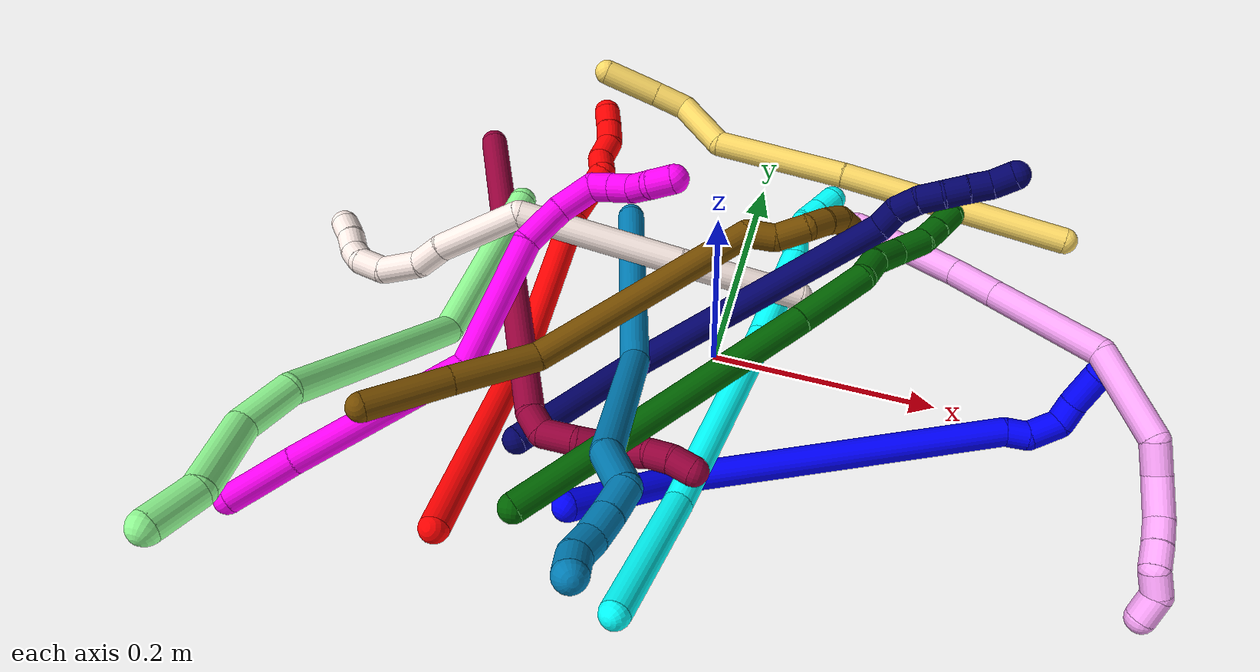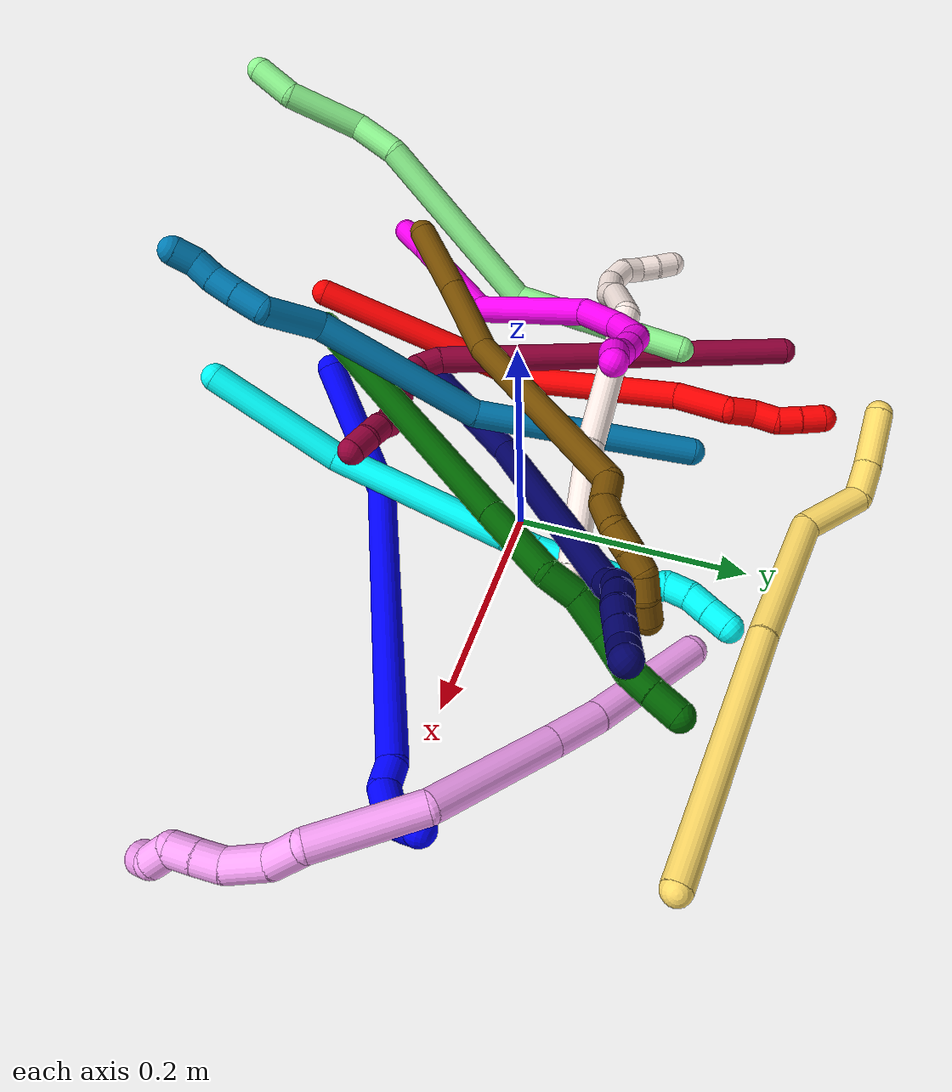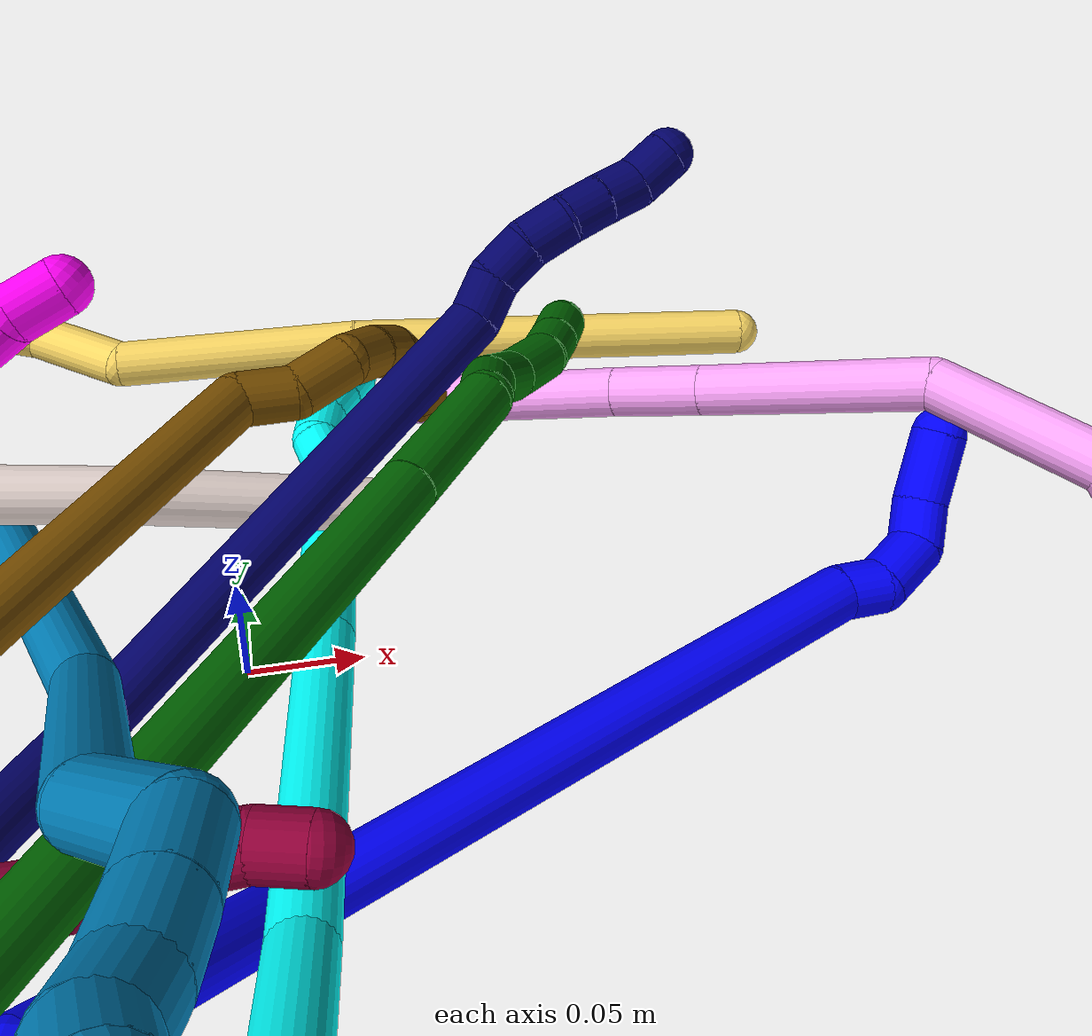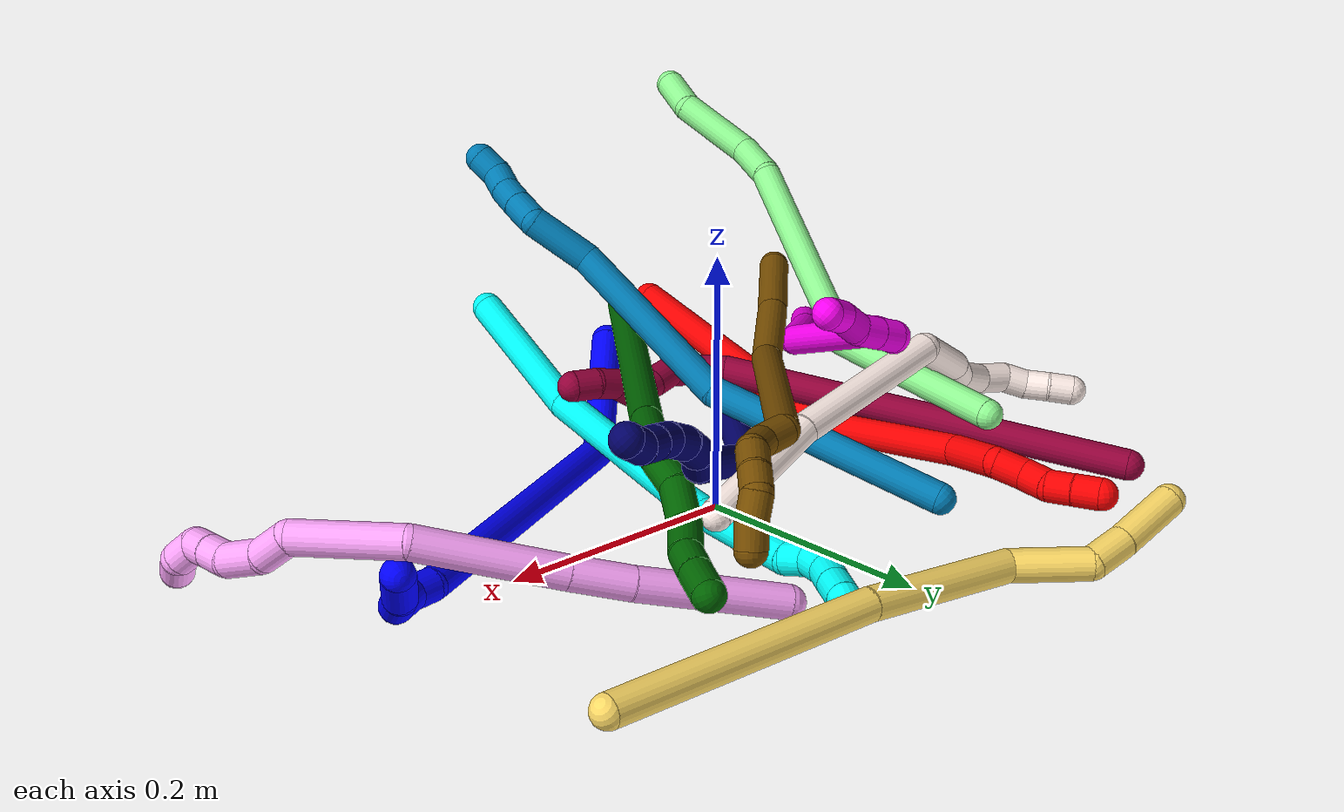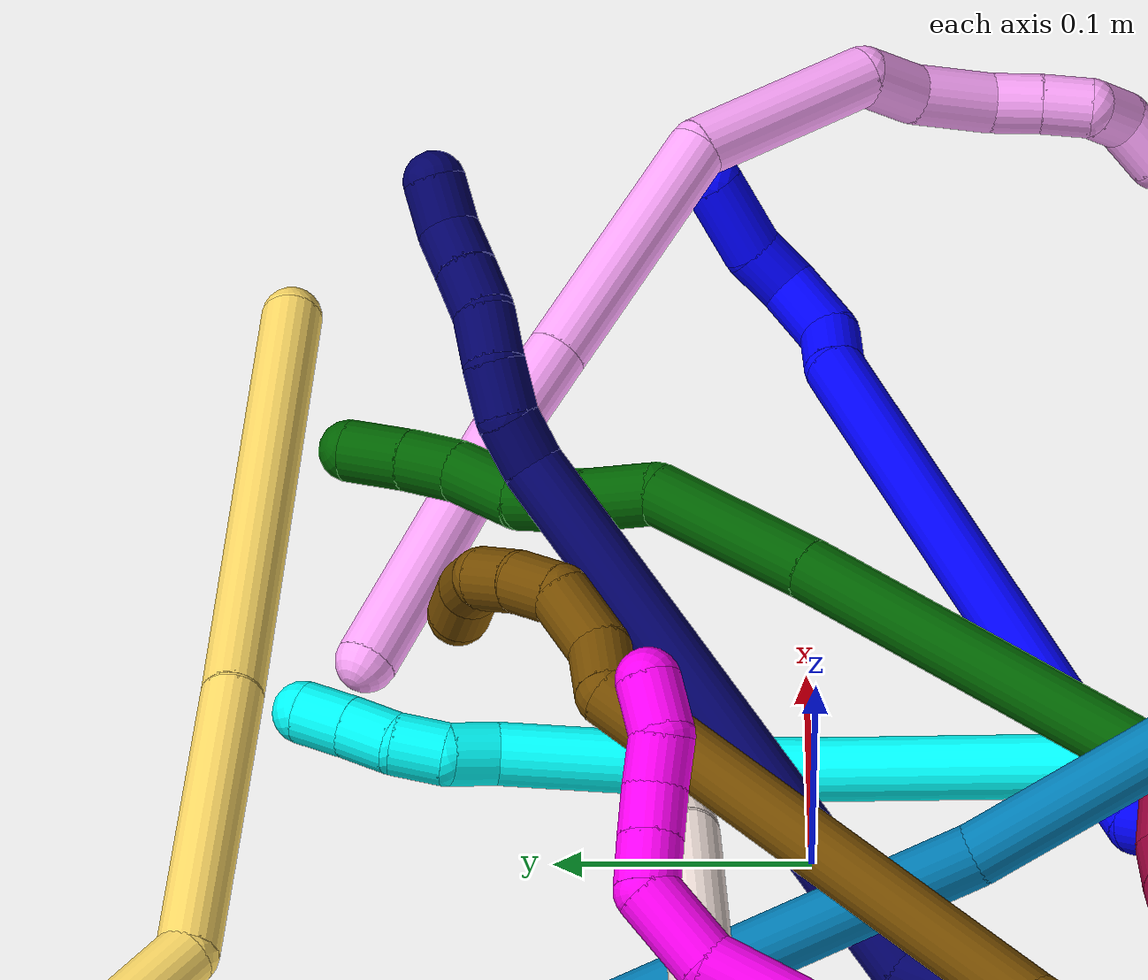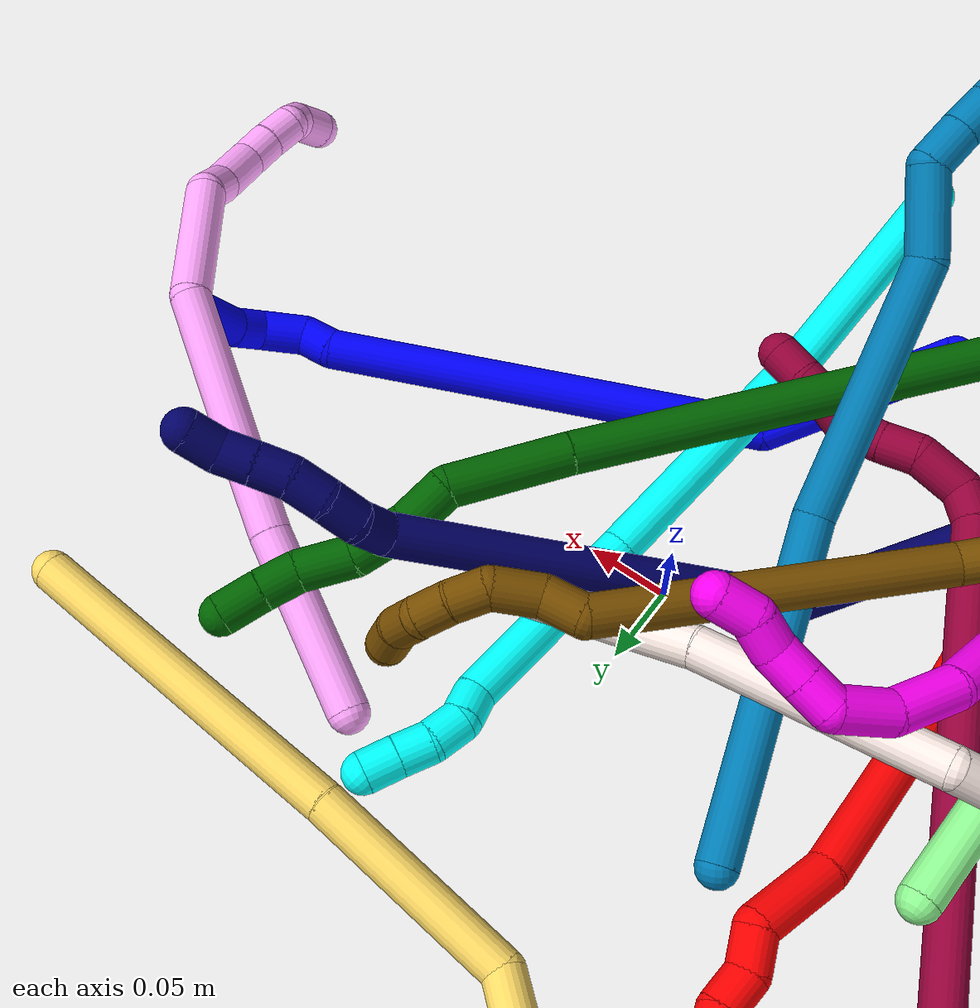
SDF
<sdf version="1.7">
 <world name="default">
  <plugin name="TubeGeneratorPlugin" filename="libtube_generator_plugin.so"/>
  <model name="photoneo_s_sensor">
   <static>1</static>
   <pose>0 0 2 1.57079 1.57079 3.14159</pose>
   <link name="link">
    <inertial><mass>0.1</mass></inertial>
    <sensor name="sensor" type="depth">
     <update_rate>30</update_rate>
     <camera>
      <horizontal_fov>1.22</horizontal_fov>
      <image><width>1920</width><height>1200</height><format>B8G8R8</format></image>
      <clip><near>0.1</near><far>4</far></clip>
      <depth_camera><output>points</output></depth_camera>
     </camera>
     <plugin name="camera_plugin" filename="libgazebo_ros_depth_camera.so">
      <baseline>0.2</baseline>
      <alwaysOn>1</alwaysOn>
      <updateRate>0.0</updateRate>
      <cameraName>camera_ir</cameraName>
      <imageTopicName>/camera/color/image_raw</imageTopicName>
      <cameraInfoTopicName>/camera/color/camera_info</cameraInfoTopicName>
      <depthImageTopicName>/camera/depth/image_raw</depthImageTopicName>
      <depthImageCameraInfoTopicName>/camera/depth/camera_info</depthImageCameraInfoTopicName>
      <pointCloudTopicName>/camera/depth/points</pointCloudTopicName>
      <frameName>fr_optical</frameName>
      <pointCloudCutoff>0.1</pointCloudCutoff>
      <pointCloudCutoffMax>2.0</pointCloudCutoffMax>
      <distortionK1>0</distortionK1>
      <distortionK2>0</distortionK2>
      <distortionK3>0</distortionK3>
      <distortionT1>0</distortionT1>
      <distortionT2>0</distortionT2>
      <CxPrime>0</CxPrime>
      <Cx>0</Cx>
      <Cy>0</Cy>
      <focalLength>0</focalLength>
      <hackBaseline>0</hackBaseline>
     </plugin>
    </sensor>
   </link>
  </model>
  <gravity>0 0 -9.8</gravity>
  <magnetic_field>6e-06 2.3e-05 -4.2e-05</magnetic_field>
  <atmosphere type="adiabatic"/>
  <physics name="default_physics" default="0" type="ode">
   <max_step_size>0.003</max_step_size>
   <real_time_factor>1</real_time_factor>
   <real_time_update_rate>1000</real_time_update_rate>
   <max_contacts>10000</max_contacts>
   <ode>
    <solver>
     <type>quick</type>
     <iters>100</iters>
     <sor>1.3</sor>
     <use_dynamic_moi_rescaling>0</use_dynamic_moi_rescaling>
    </solver>
    <constraints>
     <contact_max_correcting_vel>0</contact_max_correcting_vel>
     <contact_surface_layer>0.001</contact_surface_layer>
     <cfm>0</cfm>
     <erp>0.2</erp>
    </constraints>
   </ode>
  </physics>
  <scene><ambient>0.4 0.4 0.4 1</ambient><background>0.7 0.7 0.7 1</background><shadows>0</shadows></scene>
  <audio><device>default</device></audio>
  <spherical_coordinates>
   <surface_model>EARTH_WGS84</surface_model>
   <latitude_deg>0</latitude_deg>
   <longitude_deg>0</longitude_deg>
   <elevation>0</elevation>
   <heading_deg>0</heading_deg>
  </spherical_coordinates>
  <model name="bin">
   <static>1</static>
   <link name="bottom">
    <collision name="collision-bottom">
     <pose>0 0 -0.01 0 -0 0</pose>
     <geometry><box><size>0.8 0.6 0.02</size></box></geometry>
     <surface>
      <friction><ode><mu>100</mu><mu2>100</mu2></ode></friction>
      <contact><collide_bitmask>65535</collide_bitmask></contact>
     </surface>
    </collision>
   </link>
   <link name="west_wall">
    <collision name="collision-west_wall">
     <pose>-0.41 0 0.1 0 -0 0</pose>
     <geometry><box><size>0.02 0.6 0.2</size></box></geometry>
     <surface>
      <friction><ode><mu>100</mu><mu2>100</mu2></ode></friction>
      <contact><collide_bitmask>65535</collide_bitmask></contact>
     </surface>
    </collision>
   </link>
   <link name="east_wall">
    <collision name="collision-east_wall">
     <pose>0.41 0 0.1 0 -0 0</pose>
     <geometry><box><size>0.02 0.6 0.2</size></box></geometry>
     <surface>
      <friction><ode><mu>100</mu><mu2>100</mu2></ode></friction>
      <contact><collide_bitmask>65535</collide_bitmask></contact>
     </surface>
    </collision>
   </link>
   <link name="south_wall">
    <collision name="collision-south_wall">
     <pose>0 -0.31 0.1 0 -0 0</pose>
     <geometry><box><size>0.8 0.02 0.2</size></box></geometry>
     <surface>
      <friction><ode><mu>100</mu><mu2>100</mu2></ode></friction>
      <contact><collide_bitmask>65535</collide_bitmask></contact>
     </surface>
    </collision>
   </link>
   <link name="north_wall">
    <collision name="collision-north_wall">
     <pose>0 0.31 0.1 0 -0 0</pose>
     <geometry><box><size>0.8 0.02 0.2</size></box></geometry>
     <surface>
      <friction><ode><mu>100</mu><mu2>100</mu2></ode></friction>
      <contact><collide_bitmask>65535</collide_bitmask></contact>
     </surface>
    </collision>
   </link>
  </model>
  <model name="1">
   <static>0</static>
   <link name="1">
    <collision name="collision-cylinder-e_1_1_4">
     <pose>0.040288 -0.011876 -0.043971 2.8778 0.724216 2.46786</pose>
     <geometry><cylinder><radius>0.0125</radius><length>0.121616</length></cylinder></geometry>
     <surface>
      <friction><ode><mu>1.16</mu><mu2>1.16</mu2><slip1>0</slip1><slip2>0</slip2></ode></friction>
      <contact><ode><kp>1e+06</kp><kd>1</kd><max_vel>0</max_vel><min_depth>0.001</min_depth></ode></contact>
     </surface>
    </collision>
    <visual name="visual-cylinder-e_1_1_4">
     <pose>0.040288 -0.011876 -0.043971 2.8778 0.724216 2.46786</pose>
     <geometry><cylinder><radius>0.0125</radius><length>0.121616</length></cylinder></geometry>
     <material><ambient>0 0 1 1</ambient></material>
    </visual>
    <collision name="collision-cylinder-e_2_4_5">
     <pose>0.174627 0.030493 -0.171731 -2.56705 0.755666 -1.86181</pose>
     <geometry><cylinder><radius>0.0125</radius><length>0.274288</length></cylinder></geometry>
     <surface>
      <friction><ode><mu>1.16</mu><mu2>1.16</mu2><slip1>0</slip1><slip2>0</slip2></ode></friction>
      <contact><ode><kp>1e+06</kp><kd>1</kd><max_vel>0</max_vel><min_depth>0.001</min_depth></ode></contact>
     </surface>
    </collision>
    <visual name="visual-cylinder-e_2_4_5">
     <pose>0.174627 0.030493 -0.171731 -2.56705 0.755666 -1.86181</pose>
     <geometry><cylinder><radius>0.0125</radius><length>0.274288</length></cylinder></geometry>
     <material><ambient>0 0 1 1</ambient></material>
    </visual>
    <collision name="collision-cylinder-e_3_5_6">
     <pose>0.277031 0.089479 -0.258624 -2.15048 0.974812 -1.55121</pose>
     <geometry><cylinder><radius>0.0125</radius><length>0.020189</length></cylinder></geometry>
     <surface>
      <friction><ode><mu>1.16</mu><mu2>1.16</mu2><slip1>0</slip1><slip2>0</slip2></ode></friction>
      <contact><ode><kp>1e+06</kp><kd>1</kd><max_vel>0</max_vel><min_depth>0.001</min_depth></ode></contact>
     </surface>
    </collision>
    <visual name="visual-cylinder-e_3_5_6">
     <pose>0.277031 0.089479 -0.258624 -2.15048 0.974812 -1.55121</pose>
     <geometry><cylinder><radius>0.0125</radius><length>0.020189</length></cylinder></geometry>
     <material><ambient>0 0 1 1</ambient></material>
    </visual>
    <collision name="collision-cylinder-e_4_6_7">
     <pose>0.292766 0.100703 -0.272639 -2.60549 0.526697 -1.55223</pose>
     <geometry><cylinder><radius>0.0125</radius><length>0.029365</length></cylinder></geometry>
     <surface>
      <friction><ode><mu>1.16</mu><mu2>1.16</mu2><slip1>0</slip1><slip2>0</slip2></ode></friction>
      <contact><ode><kp>1e+06</kp><kd>1</kd><max_vel>0</max_vel><min_depth>0.001</min_depth></ode></contact>
     </surface>
    </collision>
    <visual name="visual-cylinder-e_4_6_7">
     <pose>0.292766 0.100703 -0.272639 -2.60549 0.526697 -1.55223</pose>
     <geometry><cylinder><radius>0.0125</radius><length>0.029365</length></cylinder></geometry>
     <material><ambient>0 0 1 1</ambient></material>
    </visual>
    <collision name="collision-cylinder-e_5_7_8">
     <pose>0.29831 0.113572 -0.291997 -2.49426 -0.171736 0.502364</pose>
     <geometry><cylinder><radius>0.0125</radius><length>0.021492</length></cylinder></geometry>
     <surface>
      <friction><ode><mu>1.16</mu><mu2>1.16</mu2><slip1>0</slip1><slip2>0</slip2></ode></friction>
      <contact><ode><kp>1e+06</kp><kd>1</kd><max_vel>0</max_vel><min_depth>0.001</min_depth></ode></contact>
     </surface>
    </collision>
    <visual name="visual-cylinder-e_5_7_8">
     <pose>0.29831 0.113572 -0.291997 -2.49426 -0.171736 0.502364</pose>
     <geometry><cylinder><radius>0.0125</radius><length>0.021492</length></cylinder></geometry>
     <material><ambient>0 0 1 1</ambient></material>
    </visual>
    <collision name="collision-cylinder-e_6_8_2">
     <pose>0.293313 0.132792 -0.31036 -2.2286 -0.192416 0.388081</pose>
     <geometry><cylinder><radius>0.0125</radius><length>0.033049</length></cylinder></geometry>
     <surface>
      <friction><ode><mu>1.16</mu><mu2>1.16</mu2><slip1>0</slip1><slip2>0</slip2></ode></friction>
      <contact><ode><kp>1e+06</kp><kd>1</kd><max_vel>0</max_vel><min_depth>0.001</min_depth></ode></contact>
     </surface>
    </collision>
    <visual name="visual-cylinder-e_6_8_2">
     <pose>0.293313 0.132792 -0.31036 -2.2286 -0.192416 0.388081</pose>
     <geometry><cylinder><radius>0.0125</radius><length>0.033049</length></cylinder></geometry>
     <material><ambient>0 0 1 1</ambient></material>
    </visual>
    <collision name="collision-sphere-2">
     <pose>0.290153 0.145627 -0.320276 0 -0 0</pose>
     <geometry><sphere><radius>0.0125</radius></sphere></geometry>
     <surface>
      <friction><ode><mu>1.16</mu><mu2>1.16</mu2><slip1>0</slip1><slip2>0</slip2></ode></friction>
      <contact><ode><kp>1e+06</kp><kd>1</kd><max_vel>0</max_vel><min_depth>0.001</min_depth></ode></contact>
     </surface>
    </collision>
    <visual name="visual-sphere-2">
     <pose>0.290153 0.145627 -0.320276 0 -0 0</pose>
     <geometry><sphere><radius>0.0125</radius></sphere></geometry>
     <material><ambient>0 0 1 1</ambient></material>
    </visual>
    <collision name="collision-sphere-4">
     <pose>0.080577 -0.023752 -0.087942 0 -0 0</pose>
     <geometry><sphere><radius>0.0125</radius></sphere></geometry>
     <surface>
      <friction><ode><mu>1.16</mu><mu2>1.16</mu2><slip1>0</slip1><slip2>0</slip2></ode></friction>
      <contact><ode><kp>1e+06</kp><kd>1</kd><max_vel>0</max_vel><min_depth>0.001</min_depth></ode></contact>
     </surface>
    </collision>
    <visual name="visual-sphere-4">
     <pose>0.080577 -0.023752 -0.087942 0 -0 0</pose>
     <geometry><sphere><radius>0.0125</radius></sphere></geometry>
     <material><ambient>0 0 1 1</ambient></material>
    </visual>
    <collision name="collision-sphere-1">
     <geometry><sphere><radius>0.0125</radius></sphere></geometry>
     <surface>
      <friction><ode><mu>1.16</mu><mu2>1.16</mu2><slip1>0</slip1><slip2>0</slip2></ode></friction>
      <contact><ode><kp>1e+06</kp><kd>1</kd><max_vel>0</max_vel><min_depth>0.001</min_depth></ode></contact>
     </surface>
    </collision>
    <visual name="visual-sphere-1">
     <geometry><sphere><radius>0.0125</radius></sphere></geometry>
     <material><ambient>0 0 1 1</ambient></material>
    </visual>
    <collision name="collision-sphere-8">
     <pose>0.296473 0.119957 -0.300443 0 -0 0</pose>
     <geometry><sphere><radius>0.0125</radius></sphere></geometry>
     <surface>
      <friction><ode><mu>1.16</mu><mu2>1.16</mu2><slip1>0</slip1><slip2>0</slip2></ode></friction>
      <contact><ode><kp>1e+06</kp><kd>1</kd><max_vel>0</max_vel><min_depth>0.001</min_depth></ode></contact>
     </surface>
    </collision>
    <visual name="visual-sphere-8">
     <pose>0.296473 0.119957 -0.300443 0 -0 0</pose>
     <geometry><sphere><radius>0.0125</radius></sphere></geometry>
     <material><ambient>0 0 1 1</ambient></material>
    </visual>
    <collision name="collision-sphere-5">
     <pose>0.268676 0.084739 -0.25552 0 -0 0</pose>
     <geometry><sphere><radius>0.0125</radius></sphere></geometry>
     <surface>
      <friction><ode><mu>1.16</mu><mu2>1.16</mu2><slip1>0</slip1><slip2>0</slip2></ode></friction>
      <contact><ode><kp>1e+06</kp><kd>1</kd><max_vel>0</max_vel><min_depth>0.001</min_depth></ode></contact>
     </surface>
    </collision>
    <visual name="visual-sphere-5">
     <pose>0.268676 0.084739 -0.25552 0 -0 0</pose>
     <geometry><sphere><radius>0.0125</radius></sphere></geometry>
     <material><ambient>0 0 1 1</ambient></material>
    </visual>
    <collision name="collision-sphere-6">
     <pose>0.285385 0.09422 -0.261728 0 -0 0</pose>
     <geometry><sphere><radius>0.0125</radius></sphere></geometry>
     <surface>
      <friction><ode><mu>1.16</mu><mu2>1.16</mu2><slip1>0</slip1><slip2>0</slip2></ode></friction>
      <contact><ode><kp>1e+06</kp><kd>1</kd><max_vel>0</max_vel><min_depth>0.001</min_depth></ode></contact>
     </surface>
    </collision>
    <visual name="visual-sphere-6">
     <pose>0.285385 0.09422 -0.261728 0 -0 0</pose>
     <geometry><sphere><radius>0.0125</radius></sphere></geometry>
     <material><ambient>0 0 1 1</ambient></material>
    </visual>
    <collision name="collision-sphere-7">
     <pose>0.300146 0.107187 -0.283551 0 -0 0</pose>
     <geometry><sphere><radius>0.0125</radius></sphere></geometry>
     <surface>
      <friction><ode><mu>1.16</mu><mu2>1.16</mu2><slip1>0</slip1><slip2>0</slip2></ode></friction>
      <contact><ode><kp>1e+06</kp><kd>1</kd><max_vel>0</max_vel><min_depth>0.001</min_depth></ode></contact>
     </surface>
    </collision>
    <visual name="visual-sphere-7">
     <pose>0.300146 0.107187 -0.283551 0 -0 0</pose>
     <geometry><sphere><radius>0.0125</radius></sphere></geometry>
     <material><ambient>0 0 1 1</ambient></material>
    </visual>
    <inertial>
     <pose>0.166186 0.037026 -0.164423 0 -0 0</pose>
     <mass>0.5</mass>
     <inertia>
      <ixx>-0.001559</ixx>
      <ixy>0</ixy>
      <ixz>0</ixz>
      <iyy>4.2e-05</iyy>
      <iyz>0</iyz>
      <izz>-0.001977</izz>
     </inertia>
    </inertial>
   </link>
   <pose>-0.065955 -0.200768 0.070045 1.62374 0.553104 -0.212474</pose>
  </model>
  <model name="2">
   <static>0</static>
   <link name="2">
    <collision name="collision-cylinder-e_1_1_4">
     <pose>0.020892 0.07647 -0.069784 -2.31051 0.199134 -0.445302</pose>
     <geometry><cylinder><radius>0.0125</radius><length>0.211224</length></cylinder></geometry>
     <surface>
      <friction><ode><mu>1.16</mu><mu2>1.16</mu2><slip1>0</slip1><slip2>0</slip2></ode></friction>
      <contact><ode><kp>1e+06</kp><kd>1</kd><max_vel>0</max_vel><min_depth>0.001</min_depth></ode></contact>
     </surface>
    </collision>
    <visual name="visual-cylinder-e_1_1_4">
     <pose>0.020892 0.07647 -0.069784 -2.31051 0.199134 -0.445302</pose>
     <geometry><cylinder><radius>0.0125</radius><length>0.211224</length></cylinder></geometry>
     <material><ambient>1 0 0 1</ambient></material>
    </visual>
    <collision name="collision-cylinder-e_2_4_5">
     <pose>0.071623 0.216744 -0.161274 -1.89872 0.416801 -0.574312</pose>
     <geometry><cylinder><radius>0.0125</radius><length>0.147412</length></cylinder></geometry>
     <surface>
      <friction><ode><mu>1.16</mu><mu2>1.16</mu2><slip1>0</slip1><slip2>0</slip2></ode></friction>
      <contact><ode><kp>1e+06</kp><kd>1</kd><max_vel>0</max_vel><min_depth>0.001</min_depth></ode></contact>
     </surface>
    </collision>
    <visual name="visual-cylinder-e_2_4_5">
     <pose>0.071623 0.216744 -0.161274 -1.89872 0.416801 -0.574312</pose>
     <geometry><cylinder><radius>0.0125</radius><length>0.147412</length></cylinder></geometry>
     <material><ambient>1 0 0 1</ambient></material>
    </visual>
    <collision name="collision-cylinder-e_3_5_6">
     <pose>0.117778 0.299456 -0.191004 -1.97207 0.67132 -0.970003</pose>
     <geometry><cylinder><radius>0.0125</radius><length>0.052462</length></cylinder></geometry>
     <surface>
      <friction><ode><mu>1.16</mu><mu2>1.16</mu2><slip1>0</slip1><slip2>0</slip2></ode></friction>
      <contact><ode><kp>1e+06</kp><kd>1</kd><max_vel>0</max_vel><min_depth>0.001</min_depth></ode></contact>
     </surface>
    </collision>
    <visual name="visual-cylinder-e_3_5_6">
     <pose>0.117778 0.299456 -0.191004 -1.97207 0.67132 -0.970003</pose>
     <geometry><cylinder><radius>0.0125</radius><length>0.052462</length></cylinder></geometry>
     <material><ambient>1 0 0 1</ambient></material>
    </visual>
    <collision name="collision-cylinder-e_4_6_7">
     <pose>0.132892 0.328555 -0.205245 -2.11872 -0.100395 0.178554</pose>
     <geometry><cylinder><radius>0.0125</radius><length>0.024</length></cylinder></geometry>
     <surface>
      <friction><ode><mu>1.16</mu><mu2>1.16</mu2><slip1>0</slip1><slip2>0</slip2></ode></friction>
      <contact><ode><kp>1e+06</kp><kd>1</kd><max_vel>0</max_vel><min_depth>0.001</min_depth></ode></contact>
     </surface>
    </collision>
    <visual name="visual-cylinder-e_4_6_7">
     <pose>0.132892 0.328555 -0.205245 -2.11872 -0.100395 0.178554</pose>
     <geometry><cylinder><radius>0.0125</radius><length>0.024</length></cylinder></geometry>
     <material><ambient>1 0 0 1</ambient></material>
    </visual>
    <collision name="collision-cylinder-e_5_7_8">
     <pose>0.136376 0.347811 -0.217166 -2.1322 0.412532 -0.724153</pose>
     <geometry><cylinder><radius>0.0125</radius><length>0.023378</length></cylinder></geometry>
     <surface>
      <friction><ode><mu>1.16</mu><mu2>1.16</mu2><slip1>0</slip1><slip2>0</slip2></ode></friction>
      <contact><ode><kp>1e+06</kp><kd>1</kd><max_vel>0</max_vel><min_depth>0.001</min_depth></ode></contact>
     </surface>
    </collision>
    <visual name="visual-cylinder-e_5_7_8">
     <pose>0.136376 0.347811 -0.217166 -2.1322 0.412532 -0.724153</pose>
     <geometry><cylinder><radius>0.0125</radius><length>0.023378</length></cylinder></geometry>
     <material><ambient>1 0 0 1</ambient></material>
    </visual>
    <collision name="collision-cylinder-e_6_8_9">
     <pose>0.141906 0.366659 -0.22593 -1.8742 0.082114 -0.111697</pose>
     <geometry><cylinder><radius>0.0125</radius><length>0.020573</length></cylinder></geometry>
     <surface>
      <friction><ode><mu>1.16</mu><mu2>1.16</mu2><slip1>0</slip1><slip2>0</slip2></ode></friction>
      <contact><ode><kp>1e+06</kp><kd>1</kd><max_vel>0</max_vel><min_depth>0.001</min_depth></ode></contact>
     </surface>
    </collision>
    <visual name="visual-cylinder-e_6_8_9">
     <pose>0.141906 0.366659 -0.22593 -1.8742 0.082114 -0.111697</pose>
     <geometry><cylinder><radius>0.0125</radius><length>0.020573</length></cylinder></geometry>
     <material><ambient>1 0 0 1</ambient></material>
    </visual>
    <collision name="collision-cylinder-e_7_9_2">
     <pose>0.142867 0.386433 -0.232143 -1.87626 0.011246 -0.015338</pose>
     <geometry><cylinder><radius>0.0125</radius><length>0.020952</length></cylinder></geometry>
     <surface>
      <friction><ode><mu>1.16</mu><mu2>1.16</mu2><slip1>0</slip1><slip2>0</slip2></ode></friction>
      <contact><ode><kp>1e+06</kp><kd>1</kd><max_vel>0</max_vel><min_depth>0.001</min_depth></ode></contact>
     </surface>
    </collision>
    <visual name="visual-cylinder-e_7_9_2">
     <pose>0.142867 0.386433 -0.232143 -1.87626 0.011246 -0.015338</pose>
     <geometry><cylinder><radius>0.0125</radius><length>0.020952</length></cylinder></geometry>
     <material><ambient>1 0 0 1</ambient></material>
    </visual>
    <collision name="collision-sphere-2">
     <pose>0.142985 0.396423 -0.235293 0 -0 0</pose>
     <geometry><sphere><radius>0.0125</radius></sphere></geometry>
     <surface>
      <friction><ode><mu>1.16</mu><mu2>1.16</mu2><slip1>0</slip1><slip2>0</slip2></ode></friction>
      <contact><ode><kp>1e+06</kp><kd>1</kd><max_vel>0</max_vel><min_depth>0.001</min_depth></ode></contact>
     </surface>
    </collision>
    <visual name="visual-sphere-2">
     <pose>0.142985 0.396423 -0.235293 0 -0 0</pose>
     <geometry><sphere><radius>0.0125</radius></sphere></geometry>
     <material><ambient>1 0 0 1</ambient></material>
    </visual>
    <collision name="collision-sphere-9">
     <pose>0.142749 0.376443 -0.228992 0 -0 0</pose>
     <geometry><sphere><radius>0.0125</radius></sphere></geometry>
     <surface>
      <friction><ode><mu>1.16</mu><mu2>1.16</mu2><slip1>0</slip1><slip2>0</slip2></ode></friction>
      <contact><ode><kp>1e+06</kp><kd>1</kd><max_vel>0</max_vel><min_depth>0.001</min_depth></ode></contact>
     </surface>
    </collision>
    <visual name="visual-sphere-9">
     <pose>0.142749 0.376443 -0.228992 0 -0 0</pose>
     <geometry><sphere><radius>0.0125</radius></sphere></geometry>
     <material><ambient>1 0 0 1</ambient></material>
    </visual>
    <collision name="collision-sphere-4">
     <pose>0.041784 0.15294 -0.139568 0 -0 0</pose>
     <geometry><sphere><radius>0.0125</radius></sphere></geometry>
     <surface>
      <friction><ode><mu>1.16</mu><mu2>1.16</mu2><slip1>0</slip1><slip2>0</slip2></ode></friction>
      <contact><ode><kp>1e+06</kp><kd>1</kd><max_vel>0</max_vel><min_depth>0.001</min_depth></ode></contact>
     </surface>
    </collision>
    <visual name="visual-sphere-4">
     <pose>0.041784 0.15294 -0.139568 0 -0 0</pose>
     <geometry><sphere><radius>0.0125</radius></sphere></geometry>
     <material><ambient>1 0 0 1</ambient></material>
    </visual>
    <collision name="collision-sphere-1">
     <geometry><sphere><radius>0.0125</radius></sphere></geometry>
     <surface>
      <friction><ode><mu>1.16</mu><mu2>1.16</mu2><slip1>0</slip1><slip2>0</slip2></ode></friction>
      <contact><ode><kp>1e+06</kp><kd>1</kd><max_vel>0</max_vel><min_depth>0.001</min_depth></ode></contact>
     </surface>
    </collision>
    <visual name="visual-sphere-1">
     <geometry><sphere><radius>0.0125</radius></sphere></geometry>
     <material><ambient>1 0 0 1</ambient></material>
    </visual>
    <collision name="collision-sphere-8">
     <pose>0.141062 0.356876 -0.222867 0 -0 0</pose>
     <geometry><sphere><radius>0.0125</radius></sphere></geometry>
     <surface>
      <friction><ode><mu>1.16</mu><mu2>1.16</mu2><slip1>0</slip1><slip2>0</slip2></ode></friction>
      <contact><ode><kp>1e+06</kp><kd>1</kd><max_vel>0</max_vel><min_depth>0.001</min_depth></ode></contact>
     </surface>
    </collision>
    <visual name="visual-sphere-8">
     <pose>0.141062 0.356876 -0.222867 0 -0 0</pose>
     <geometry><sphere><radius>0.0125</radius></sphere></geometry>
     <material><ambient>1 0 0 1</ambient></material>
    </visual>
    <collision name="collision-sphere-5">
     <pose>0.101462 0.280548 -0.182981 0 -0 0</pose>
     <geometry><sphere><radius>0.0125</radius></sphere></geometry>
     <surface>
      <friction><ode><mu>1.16</mu><mu2>1.16</mu2><slip1>0</slip1><slip2>0</slip2></ode></friction>
      <contact><ode><kp>1e+06</kp><kd>1</kd><max_vel>0</max_vel><min_depth>0.001</min_depth></ode></contact>
     </surface>
    </collision>
    <visual name="visual-sphere-5">
     <pose>0.101462 0.280548 -0.182981 0 -0 0</pose>
     <geometry><sphere><radius>0.0125</radius></sphere></geometry>
     <material><ambient>1 0 0 1</ambient></material>
    </visual>
    <collision name="collision-sphere-6">
     <pose>0.134095 0.318363 -0.199026 0 -0 0</pose>
     <geometry><sphere><radius>0.0125</radius></sphere></geometry>
     <surface>
      <friction><ode><mu>1.16</mu><mu2>1.16</mu2><slip1>0</slip1><slip2>0</slip2></ode></friction>
      <contact><ode><kp>1e+06</kp><kd>1</kd><max_vel>0</max_vel><min_depth>0.001</min_depth></ode></contact>
     </surface>
    </collision>
    <visual name="visual-sphere-6">
     <pose>0.134095 0.318363 -0.199026 0 -0 0</pose>
     <geometry><sphere><radius>0.0125</radius></sphere></geometry>
     <material><ambient>1 0 0 1</ambient></material>
    </visual>
    <collision name="collision-sphere-7">
     <pose>0.131689 0.338746 -0.211465 0 -0 0</pose>
     <geometry><sphere><radius>0.0125</radius></sphere></geometry>
     <surface>
      <friction><ode><mu>1.16</mu><mu2>1.16</mu2><slip1>0</slip1><slip2>0</slip2></ode></friction>
      <contact><ode><kp>1e+06</kp><kd>1</kd><max_vel>0</max_vel><min_depth>0.001</min_depth></ode></contact>
     </surface>
    </collision>
    <visual name="visual-sphere-7">
     <pose>0.131689 0.338746 -0.211465 0 -0 0</pose>
     <geometry><sphere><radius>0.0125</radius></sphere></geometry>
     <material><ambient>1 0 0 1</ambient></material>
    </visual>
    <inertial>
     <pose>0.06688 0.190938 -0.136097 0 -0 0</pose>
     <mass>0.5</mass>
     <inertia>
      <ixx>0.000455</ixx>
      <ixy>0</ixy>
      <ixz>0</ixz>
      <iyy>-0.000898</iyy>
      <iyz>0</iyz>
      <izz>-0.001122</izz>
     </inertia>
    </inertial>
   </link>
   <pose>-0.155997 -0.246276 0.076869 0.306166 -0.378527 0.399296</pose>
  </model>
  <model name="3">
   <static>0</static>
   <link name="3">
    <collision name="collision-cylinder-e_1_1_4">
     <pose>-0.008019 0.012208 -0.061747 -2.9464 -0.126727 1.15</pose>
     <geometry><cylinder><radius>0.0125</radius><length>0.126901</length></cylinder></geometry>
     <surface>
      <friction><ode><mu>1.16</mu><mu2>1.16</mu2><slip1>0</slip1><slip2>0</slip2></ode></friction>
      <contact><ode><kp>1e+06</kp><kd>1</kd><max_vel>0</max_vel><min_depth>0.001</min_depth></ode></contact>
     </surface>
    </collision>
    <visual name="visual-cylinder-e_1_1_4">
     <pose>-0.008019 0.012208 -0.061747 -2.9464 -0.126727 1.15</pose>
     <geometry><cylinder><radius>0.0125</radius><length>0.126901</length></cylinder></geometry>
     <material><ambient>0.003922 1 0.996078 1</ambient></material>
    </visual>
    <collision name="collision-cylinder-e_2_4_5">
     <pose>-0.020043 0.05982 -0.197854 -2.69724 -0.048579 0.214259</pose>
     <geometry><cylinder><radius>0.0125</radius><length>0.164912</length></cylinder></geometry>
     <surface>
      <friction><ode><mu>1.16</mu><mu2>1.16</mu2><slip1>0</slip1><slip2>0</slip2></ode></friction>
      <contact><ode><kp>1e+06</kp><kd>1</kd><max_vel>0</max_vel><min_depth>0.001</min_depth></ode></contact>
     </surface>
    </collision>
    <visual name="visual-cylinder-e_2_4_5">
     <pose>-0.020043 0.05982 -0.197854 -2.69724 -0.048579 0.214259</pose>
     <geometry><cylinder><radius>0.0125</radius><length>0.164912</length></cylinder></geometry>
     <material><ambient>0.003922 1 0.996078 1</ambient></material>
    </visual>
    <collision name="collision-cylinder-e_3_5_6">
     <pose>-0.024737 0.102277 -0.285279 -2.64659 -0.046413 0.1832</pose>
     <geometry><cylinder><radius>0.0125</radius><length>0.029724</length></cylinder></geometry>
     <surface>
      <friction><ode><mu>1.16</mu><mu2>1.16</mu2><slip1>0</slip1><slip2>0</slip2></ode></friction>
      <contact><ode><kp>1e+06</kp><kd>1</kd><max_vel>0</max_vel><min_depth>0.001</min_depth></ode></contact>
     </surface>
    </collision>
    <visual name="visual-cylinder-e_3_5_6">
     <pose>-0.024737 0.102277 -0.285279 -2.64659 -0.046413 0.1832</pose>
     <geometry><cylinder><radius>0.0125</radius><length>0.029724</length></cylinder></geometry>
     <material><ambient>0.003922 1 0.996078 1</ambient></material>
    </visual>
    <collision name="collision-cylinder-e_4_6_7">
     <pose>-0.027013 0.135524 -0.338416 -2.56263 -0.03314 0.111161</pose>
     <geometry><cylinder><radius>0.0125</radius><length>0.095802</length></cylinder></geometry>
     <surface>
      <friction><ode><mu>1.16</mu><mu2>1.16</mu2><slip1>0</slip1><slip2>0</slip2></ode></friction>
      <contact><ode><kp>1e+06</kp><kd>1</kd><max_vel>0</max_vel><min_depth>0.001</min_depth></ode></contact>
     </surface>
    </collision>
    <visual name="visual-cylinder-e_4_6_7">
     <pose>-0.027013 0.135524 -0.338416 -2.56263 -0.03314 0.111161</pose>
     <geometry><cylinder><radius>0.0125</radius><length>0.095802</length></cylinder></geometry>
     <material><ambient>0.003922 1 0.996078 1</ambient></material>
    </visual>
    <collision name="collision-cylinder-e_5_7_8">
     <pose>-0.031432 0.169513 -0.384494 -2.22731 -0.280189 0.558396</pose>
     <geometry><cylinder><radius>0.0125</radius><length>0.020478</length></cylinder></geometry>
     <surface>
      <friction><ode><mu>1.16</mu><mu2>1.16</mu2><slip1>0</slip1><slip2>0</slip2></ode></friction>
      <contact><ode><kp>1e+06</kp><kd>1</kd><max_vel>0</max_vel><min_depth>0.001</min_depth></ode></contact>
     </surface>
    </collision>
    <visual name="visual-cylinder-e_5_7_8">
     <pose>-0.031432 0.169513 -0.384494 -2.22731 -0.280189 0.558396</pose>
     <geometry><cylinder><radius>0.0125</radius><length>0.020478</length></cylinder></geometry>
     <material><ambient>0.003922 1 0.996078 1</ambient></material>
    </visual>
    <collision name="collision-cylinder-e_6_8_9">
     <pose>-0.032998 0.183154 -0.399218 -2.55089 0.119933 -0.389657</pose>
     <geometry><cylinder><radius>0.0125</radius><length>0.021147</length></cylinder></geometry>
     <surface>
      <friction><ode><mu>1.16</mu><mu2>1.16</mu2><slip1>0</slip1><slip2>0</slip2></ode></friction>
      <contact><ode><kp>1e+06</kp><kd>1</kd><max_vel>0</max_vel><min_depth>0.001</min_depth></ode></contact>
     </surface>
    </collision>
    <visual name="visual-cylinder-e_6_8_9">
     <pose>-0.032998 0.183154 -0.399218 -2.55089 0.119933 -0.389657</pose>
     <geometry><cylinder><radius>0.0125</radius><length>0.021147</length></cylinder></geometry>
     <material><ambient>0.003922 1 0.996078 1</ambient></material>
    </visual>
    <collision name="collision-cylinder-e_7_9_10">
     <pose>-0.028309 0.192856 -0.41662 -2.72369 0.345952 -1.3784</pose>
     <geometry><cylinder><radius>0.0125</radius><length>0.020197</length></cylinder></geometry>
     <surface>
      <friction><ode><mu>1.16</mu><mu2>1.16</mu2><slip1>0</slip1><slip2>0</slip2></ode></friction>
      <contact><ode><kp>1e+06</kp><kd>1</kd><max_vel>0</max_vel><min_depth>0.001</min_depth></ode></contact>
     </surface>
    </collision>
    <visual name="visual-cylinder-e_7_9_10">
     <pose>-0.028309 0.192856 -0.41662 -2.72369 0.345952 -1.3784</pose>
     <geometry><cylinder><radius>0.0125</radius><length>0.020197</length></cylinder></geometry>
     <material><ambient>0.003922 1 0.996078 1</ambient></material>
    </visual>
    <collision name="collision-cylinder-e_8_10_2">
     <pose>-0.021718 0.2007 -0.434392 -2.72806 0.308739 -1.2765</pose>
     <geometry><cylinder><radius>0.0125</radius><length>0.020838</length></cylinder></geometry>
     <surface>
      <friction><ode><mu>1.16</mu><mu2>1.16</mu2><slip1>0</slip1><slip2>0</slip2></ode></friction>
      <contact><ode><kp>1e+06</kp><kd>1</kd><max_vel>0</max_vel><min_depth>0.001</min_depth></ode></contact>
     </surface>
    </collision>
    <visual name="visual-cylinder-e_8_10_2">
     <pose>-0.021718 0.2007 -0.434392 -2.72806 0.308739 -1.2765</pose>
     <geometry><cylinder><radius>0.0125</radius><length>0.020838</length></cylinder></geometry>
     <material><ambient>0.003922 1 0.996078 1</ambient></material>
    </visual>
    <collision name="collision-sphere-2">
     <pose>-0.018553 0.204689 -0.443482 0 -0 0</pose>
     <geometry><sphere><radius>0.0125</radius></sphere></geometry>
     <surface>
      <friction><ode><mu>1.16</mu><mu2>1.16</mu2><slip1>0</slip1><slip2>0</slip2></ode></friction>
      <contact><ode><kp>1e+06</kp><kd>1</kd><max_vel>0</max_vel><min_depth>0.001</min_depth></ode></contact>
     </surface>
    </collision>
    <visual name="visual-sphere-2">
     <pose>-0.018553 0.204689 -0.443482 0 -0 0</pose>
     <geometry><sphere><radius>0.0125</radius></sphere></geometry>
     <material><ambient>0.003922 1 0.996078 1</ambient></material>
    </visual>
    <collision name="collision-sphere-10">
     <pose>-0.024884 0.196711 -0.425302 0 -0 0</pose>
     <geometry><sphere><radius>0.0125</radius></sphere></geometry>
     <surface>
      <friction><ode><mu>1.16</mu><mu2>1.16</mu2><slip1>0</slip1><slip2>0</slip2></ode></friction>
      <contact><ode><kp>1e+06</kp><kd>1</kd><max_vel>0</max_vel><min_depth>0.001</min_depth></ode></contact>
     </surface>
    </collision>
    <visual name="visual-sphere-10">
     <pose>-0.024884 0.196711 -0.425302 0 -0 0</pose>
     <geometry><sphere><radius>0.0125</radius></sphere></geometry>
     <material><ambient>0.003922 1 0.996078 1</ambient></material>
    </visual>
    <collision name="collision-sphere-9">
     <pose>-0.031733 0.189 -0.407937 0 -0 0</pose>
     <geometry><sphere><radius>0.0125</radius></sphere></geometry>
     <surface>
      <friction><ode><mu>1.16</mu><mu2>1.16</mu2><slip1>0</slip1><slip2>0</slip2></ode></friction>
      <contact><ode><kp>1e+06</kp><kd>1</kd><max_vel>0</max_vel><min_depth>0.001</min_depth></ode></contact>
     </surface>
    </collision>
    <visual name="visual-sphere-9">
     <pose>-0.031733 0.189 -0.407937 0 -0 0</pose>
     <geometry><sphere><radius>0.0125</radius></sphere></geometry>
     <material><ambient>0.003922 1 0.996078 1</ambient></material>
    </visual>
    <collision name="collision-sphere-4">
     <pose>-0.016039 0.024416 -0.123493 0 -0 0</pose>
     <geometry><sphere><radius>0.0125</radius></sphere></geometry>
     <surface>
      <friction><ode><mu>1.16</mu><mu2>1.16</mu2><slip1>0</slip1><slip2>0</slip2></ode></friction>
      <contact><ode><kp>1e+06</kp><kd>1</kd><max_vel>0</max_vel><min_depth>0.001</min_depth></ode></contact>
     </surface>
    </collision>
    <visual name="visual-sphere-4">
     <pose>-0.016039 0.024416 -0.123493 0 -0 0</pose>
     <geometry><sphere><radius>0.0125</radius></sphere></geometry>
     <material><ambient>0.003922 1 0.996078 1</ambient></material>
    </visual>
    <collision name="collision-sphere-1">
     <geometry><sphere><radius>0.0125</radius></sphere></geometry>
     <surface>
      <friction><ode><mu>1.16</mu><mu2>1.16</mu2><slip1>0</slip1><slip2>0</slip2></ode></friction>
      <contact><ode><kp>1e+06</kp><kd>1</kd><max_vel>0</max_vel><min_depth>0.001</min_depth></ode></contact>
     </surface>
    </collision>
    <visual name="visual-sphere-1">
     <geometry><sphere><radius>0.0125</radius></sphere></geometry>
     <material><ambient>0.003922 1 0.996078 1</ambient></material>
    </visual>
    <collision name="collision-sphere-8">
     <pose>-0.034263 0.177307 -0.3905 0 -0 0</pose>
     <geometry><sphere><radius>0.0125</radius></sphere></geometry>
     <surface>
      <friction><ode><mu>1.16</mu><mu2>1.16</mu2><slip1>0</slip1><slip2>0</slip2></ode></friction>
      <contact><ode><kp>1e+06</kp><kd>1</kd><max_vel>0</max_vel><min_depth>0.001</min_depth></ode></contact>
     </surface>
    </collision>
    <visual name="visual-sphere-8">
     <pose>-0.034263 0.177307 -0.3905 0 -0 0</pose>
     <geometry><sphere><radius>0.0125</radius></sphere></geometry>
     <material><ambient>0.003922 1 0.996078 1</ambient></material>
    </visual>
    <collision name="collision-sphere-5">
     <pose>-0.024047 0.095224 -0.272215 0 -0 0</pose>
     <geometry><sphere><radius>0.0125</radius></sphere></geometry>
     <surface>
      <friction><ode><mu>1.16</mu><mu2>1.16</mu2><slip1>0</slip1><slip2>0</slip2></ode></friction>
      <contact><ode><kp>1e+06</kp><kd>1</kd><max_vel>0</max_vel><min_depth>0.001</min_depth></ode></contact>
     </surface>
    </collision>
    <visual name="visual-sphere-5">
     <pose>-0.024047 0.095224 -0.272215 0 -0 0</pose>
     <geometry><sphere><radius>0.0125</radius></sphere></geometry>
     <material><ambient>0.003922 1 0.996078 1</ambient></material>
    </visual>
    <collision name="collision-sphere-6">
     <pose>-0.025426 0.109329 -0.298343 0 -0 0</pose>
     <geometry><sphere><radius>0.0125</radius></sphere></geometry>
     <surface>
      <friction><ode><mu>1.16</mu><mu2>1.16</mu2><slip1>0</slip1><slip2>0</slip2></ode></friction>
      <contact><ode><kp>1e+06</kp><kd>1</kd><max_vel>0</max_vel><min_depth>0.001</min_depth></ode></contact>
     </surface>
    </collision>
    <visual name="visual-sphere-6">
     <pose>-0.025426 0.109329 -0.298343 0 -0 0</pose>
     <geometry><sphere><radius>0.0125</radius></sphere></geometry>
     <material><ambient>0.003922 1 0.996078 1</ambient></material>
    </visual>
    <collision name="collision-sphere-7">
     <pose>-0.0286 0.161719 -0.378488 0 -0 0</pose>
     <geometry><sphere><radius>0.0125</radius></sphere></geometry>
     <surface>
      <friction><ode><mu>1.16</mu><mu2>1.16</mu2><slip1>0</slip1><slip2>0</slip2></ode></friction>
      <contact><ode><kp>1e+06</kp><kd>1</kd><max_vel>0</max_vel><min_depth>0.001</min_depth></ode></contact>
     </surface>
    </collision>
    <visual name="visual-sphere-7">
     <pose>-0.0286 0.161719 -0.378488 0 -0 0</pose>
     <geometry><sphere><radius>0.0125</radius></sphere></geometry>
     <material><ambient>0.003922 1 0.996078 1</ambient></material>
    </visual>
    <inertial>
     <pose>-0.020024 0.085719 -0.230294 0 -0 0</pose>
     <mass>0.5</mass>
     <inertia>
      <ixx>0.00077</ixx>
      <ixy>0</ixy>
      <ixz>0</ixz>
      <iyy>-0.000207</iyy>
      <iyz>0</iyz>
      <izz>-0.000236</izz>
     </inertia>
    </inertial>
   </link>
   <pose>-0.001835 -0.279413 0.09388 0.977548 -0.278144 -0.139661</pose>
  </model>
  <model name="4">
   <static>0</static>
   <link name="4">
    <collision name="collision-cylinder-e_1_1_4">
     <pose>-0.00089 -0.000141 0.056537 0.002497 -0.015733 -2e-05</pose>
     <geometry><cylinder><radius>0.0125</radius><length>0.113089</length></cylinder></geometry>
     <surface>
      <friction><ode><mu>1.16</mu><mu2>1.16</mu2><slip1>0</slip1><slip2>0</slip2></ode></friction>
      <contact><ode><kp>1e+06</kp><kd>1</kd><max_vel>0</max_vel><min_depth>0.001</min_depth></ode></contact>
     </surface>
    </collision>
    <visual name="visual-cylinder-e_1_1_4">
     <pose>-0.00089 -0.000141 0.056537 0.002497 -0.015733 -2e-05</pose>
     <geometry><cylinder><radius>0.0125</radius><length>0.113089</length></cylinder></geometry>
     <material><ambient>1 0.65098 0.996078 1</ambient></material>
    </visual>
    <collision name="collision-cylinder-e_2_4_5">
     <pose>-0.001466 -0.001957 0.1356 0.074206 0.013869 0.000515</pose>
     <geometry><cylinder><radius>0.0125</radius><length>0.04518</length></cylinder></geometry>
     <surface>
      <friction><ode><mu>1.16</mu><mu2>1.16</mu2><slip1>0</slip1><slip2>0</slip2></ode></friction>
      <contact><ode><kp>1e+06</kp><kd>1</kd><max_vel>0</max_vel><min_depth>0.001</min_depth></ode></contact>
     </surface>
    </collision>
    <visual name="visual-cylinder-e_2_4_5">
     <pose>-0.001466 -0.001957 0.1356 0.074206 0.013869 0.000515</pose>
     <geometry><cylinder><radius>0.0125</radius><length>0.04518</length></cylinder></geometry>
     <material><ambient>1 0.65098 0.996078 1</ambient></material>
    </visual>
    <collision name="collision-cylinder-e_3_5_6">
     <pose>-0.000777 -0.008819 0.212443 0.09521 0.006874 0.000328</pose>
     <geometry><cylinder><radius>0.0125</radius><length>0.109132</length></cylinder></geometry>
     <surface>
      <friction><ode><mu>1.16</mu><mu2>1.16</mu2><slip1>0</slip1><slip2>0</slip2></ode></friction>
      <contact><ode><kp>1e+06</kp><kd>1</kd><max_vel>0</max_vel><min_depth>0.001</min_depth></ode></contact>
     </surface>
    </collision>
    <visual name="visual-cylinder-e_3_5_6">
     <pose>-0.000777 -0.008819 0.212443 0.09521 0.006874 0.000328</pose>
     <geometry><cylinder><radius>0.0125</radius><length>0.109132</length></cylinder></geometry>
     <material><ambient>1 0.65098 0.996078 1</ambient></material>
    </visual>
    <collision name="collision-cylinder-e_4_6_7">
     <pose>0.01921 -0.022594 0.30258 0.235317 0.48925 0.058996</pose>
     <geometry><cylinder><radius>0.0125</radius><length>0.083462</length></cylinder></geometry>
     <surface>
      <friction><ode><mu>1.16</mu><mu2>1.16</mu2><slip1>0</slip1><slip2>0</slip2></ode></friction>
      <contact><ode><kp>1e+06</kp><kd>1</kd><max_vel>0</max_vel><min_depth>0.001</min_depth></ode></contact>
     </surface>
    </collision>
    <visual name="visual-cylinder-e_4_6_7">
     <pose>0.01921 -0.022594 0.30258 0.235317 0.48925 0.058996</pose>
     <geometry><cylinder><radius>0.0125</radius><length>0.083462</length></cylinder></geometry>
     <material><ambient>1 0.65098 0.996078 1</ambient></material>
    </visual>
    <collision name="collision-cylinder-e_5_7_8">
     <pose>0.051656 -0.030441 0.344808 -0.115112 1.10509 -0.071027</pose>
     <geometry><cylinder><radius>0.0125</radius><length>0.028729</length></cylinder></geometry>
     <surface>
      <friction><ode><mu>1.16</mu><mu2>1.16</mu2><slip1>0</slip1><slip2>0</slip2></ode></friction>
      <contact><ode><kp>1e+06</kp><kd>1</kd><max_vel>0</max_vel><min_depth>0.001</min_depth></ode></contact>
     </surface>
    </collision>
    <visual name="visual-cylinder-e_5_7_8">
     <pose>0.051656 -0.030441 0.344808 -0.115112 1.10509 -0.071027</pose>
     <geometry><cylinder><radius>0.0125</radius><length>0.028729</length></cylinder></geometry>
     <material><ambient>1 0.65098 0.996078 1</ambient></material>
    </visual>
    <collision name="collision-cylinder-e_6_8_9">
     <pose>0.078614 -0.034892 0.360462 0.511633 0.926764 0.2599</pose>
     <geometry><cylinder><radius>0.0125</radius><length>0.03532</length></cylinder></geometry>
     <surface>
      <friction><ode><mu>1.16</mu><mu2>1.16</mu2><slip1>0</slip1><slip2>0</slip2></ode></friction>
      <contact><ode><kp>1e+06</kp><kd>1</kd><max_vel>0</max_vel><min_depth>0.001</min_depth></ode></contact>
     </surface>
    </collision>
    <visual name="visual-cylinder-e_6_8_9">
     <pose>0.078614 -0.034892 0.360462 0.511633 0.926764 0.2599</pose>
     <geometry><cylinder><radius>0.0125</radius><length>0.03532</length></cylinder></geometry>
     <material><ambient>1 0.65098 0.996078 1</ambient></material>
    </visual>
    <collision name="collision-cylinder-e_7_9_10">
     <pose>0.099472 -0.046585 0.374535 0.932056 0.693815 0.359751</pose>
     <geometry><cylinder><radius>0.0125</radius><length>0.021066</length></cylinder></geometry>
     <surface>
      <friction><ode><mu>1.16</mu><mu2>1.16</mu2><slip1>0</slip1><slip2>0</slip2></ode></friction>
      <contact><ode><kp>1e+06</kp><kd>1</kd><max_vel>0</max_vel><min_depth>0.001</min_depth></ode></contact>
     </surface>
    </collision>
    <visual name="visual-cylinder-e_7_9_10">
     <pose>0.099472 -0.046585 0.374535 0.932056 0.693815 0.359751</pose>
     <geometry><cylinder><radius>0.0125</radius><length>0.021066</length></cylinder></geometry>
     <material><ambient>1 0.65098 0.996078 1</ambient></material>
    </visual>
    <collision name="collision-cylinder-e_8_10_11">
     <pose>0.113278 -0.059433 0.38358 0.984281 0.748042 0.414815</pose>
     <geometry><cylinder><radius>0.0125</radius><length>0.020789</length></cylinder></geometry>
     <surface>
      <friction><ode><mu>1.16</mu><mu2>1.16</mu2><slip1>0</slip1><slip2>0</slip2></ode></friction>
      <contact><ode><kp>1e+06</kp><kd>1</kd><max_vel>0</max_vel><min_depth>0.001</min_depth></ode></contact>
     </surface>
    </collision>
    <visual name="visual-cylinder-e_8_10_11">
     <pose>0.113278 -0.059433 0.38358 0.984281 0.748042 0.414815</pose>
     <geometry><cylinder><radius>0.0125</radius><length>0.020789</length></cylinder></geometry>
     <material><ambient>1 0.65098 0.996078 1</ambient></material>
    </visual>
    <collision name="collision-cylinder-e_9_11_12">
     <pose>0.129372 -0.064513 0.392431 -0.266575 1.08166 -0.160701</pose>
     <geometry><cylinder><radius>0.0125</radius><length>0.020444</length></cylinder></geometry>
     <surface>
      <friction><ode><mu>1.16</mu><mu2>1.16</mu2><slip1>0</slip1><slip2>0</slip2></ode></friction>
      <contact><ode><kp>1e+06</kp><kd>1</kd><max_vel>0</max_vel><min_depth>0.001</min_depth></ode></contact>
     </surface>
    </collision>
    <visual name="visual-cylinder-e_9_11_12">
     <pose>0.129372 -0.064513 0.392431 -0.266575 1.08166 -0.160701</pose>
     <geometry><cylinder><radius>0.0125</radius><length>0.020444</length></cylinder></geometry>
     <material><ambient>1 0.65098 0.996078 1</ambient></material>
    </visual>
    <collision name="collision-cylinder-e_10_12_2">
     <pose>0.149605 -0.064784 0.395714 2.29192 1.39034 2.14764</pose>
     <geometry><cylinder><radius>0.0125</radius><length>0.022789</length></cylinder></geometry>
     <surface>
      <friction><ode><mu>1.16</mu><mu2>1.16</mu2><slip1>0</slip1><slip2>0</slip2></ode></friction>
      <contact><ode><kp>1e+06</kp><kd>1</kd><max_vel>0</max_vel><min_depth>0.001</min_depth></ode></contact>
     </surface>
    </collision>
    <visual name="visual-cylinder-e_10_12_2">
     <pose>0.149605 -0.064784 0.395714 2.29192 1.39034 2.14764</pose>
     <geometry><cylinder><radius>0.0125</radius><length>0.022789</length></cylinder></geometry>
     <material><ambient>1 0.65098 0.996078 1</ambient></material>
    </visual>
    <collision name="collision-sphere-2">
     <pose>0.160814 -0.06632 0.394364 0 -0 0</pose>
     <geometry><sphere><radius>0.0125</radius></sphere></geometry>
     <surface>
      <friction><ode><mu>1.16</mu><mu2>1.16</mu2><slip1>0</slip1><slip2>0</slip2></ode></friction>
      <contact><ode><kp>1e+06</kp><kd>1</kd><max_vel>0</max_vel><min_depth>0.001</min_depth></ode></contact>
     </surface>
    </collision>
    <visual name="visual-sphere-2">
     <pose>0.160814 -0.06632 0.394364 0 -0 0</pose>
     <geometry><sphere><radius>0.0125</radius></sphere></geometry>
     <material><ambient>1 0.65098 0.996078 1</ambient></material>
    </visual>
    <collision name="collision-sphere-12">
     <pose>0.138395 -0.063248 0.397064 0 -0 0</pose>
     <geometry><sphere><radius>0.0125</radius></sphere></geometry>
     <surface>
      <friction><ode><mu>1.16</mu><mu2>1.16</mu2><slip1>0</slip1><slip2>0</slip2></ode></friction>
      <contact><ode><kp>1e+06</kp><kd>1</kd><max_vel>0</max_vel><min_depth>0.001</min_depth></ode></contact>
     </surface>
    </collision>
    <visual name="visual-sphere-12">
     <pose>0.138395 -0.063248 0.397064 0 -0 0</pose>
     <geometry><sphere><radius>0.0125</radius></sphere></geometry>
     <material><ambient>1 0.65098 0.996078 1</ambient></material>
    </visual>
    <collision name="collision-sphere-11">
     <pose>0.120348 -0.065779 0.387798 0 -0 0</pose>
     <geometry><sphere><radius>0.0125</radius></sphere></geometry>
     <surface>
      <friction><ode><mu>1.16</mu><mu2>1.16</mu2><slip1>0</slip1><slip2>0</slip2></ode></friction>
      <contact><ode><kp>1e+06</kp><kd>1</kd><max_vel>0</max_vel><min_depth>0.001</min_depth></ode></contact>
     </surface>
    </collision>
    <visual name="visual-sphere-11">
     <pose>0.120348 -0.065779 0.387798 0 -0 0</pose>
     <geometry><sphere><radius>0.0125</radius></sphere></geometry>
     <material><ambient>1 0.65098 0.996078 1</ambient></material>
    </visual>
    <collision name="collision-sphere-10">
     <pose>0.106207 -0.053087 0.379363 0 -0 0</pose>
     <geometry><sphere><radius>0.0125</radius></sphere></geometry>
     <surface>
      <friction><ode><mu>1.16</mu><mu2>1.16</mu2><slip1>0</slip1><slip2>0</slip2></ode></friction>
      <contact><ode><kp>1e+06</kp><kd>1</kd><max_vel>0</max_vel><min_depth>0.001</min_depth></ode></contact>
     </surface>
    </collision>
    <visual name="visual-sphere-10">
     <pose>0.106207 -0.053087 0.379363 0 -0 0</pose>
     <geometry><sphere><radius>0.0125</radius></sphere></geometry>
     <material><ambient>1 0.65098 0.996078 1</ambient></material>
    </visual>
    <collision name="collision-sphere-9">
     <pose>0.092736 -0.040084 0.369708 0 -0 0</pose>
     <geometry><sphere><radius>0.0125</radius></sphere></geometry>
     <surface>
      <friction><ode><mu>1.16</mu><mu2>1.16</mu2><slip1>0</slip1><slip2>0</slip2></ode></friction>
      <contact><ode><kp>1e+06</kp><kd>1</kd><max_vel>0</max_vel><min_depth>0.001</min_depth></ode></contact>
     </surface>
    </collision>
    <visual name="visual-sphere-9">
     <pose>0.092736 -0.040084 0.369708 0 -0 0</pose>
     <geometry><sphere><radius>0.0125</radius></sphere></geometry>
     <material><ambient>1 0.65098 0.996078 1</ambient></material>
    </visual>
    <collision name="collision-sphere-4">
     <pose>-0.001779 -0.000282 0.113075 0 -0 0</pose>
     <geometry><sphere><radius>0.0125</radius></sphere></geometry>
     <surface>
      <friction><ode><mu>1.16</mu><mu2>1.16</mu2><slip1>0</slip1><slip2>0</slip2></ode></friction>
      <contact><ode><kp>1e+06</kp><kd>1</kd><max_vel>0</max_vel><min_depth>0.001</min_depth></ode></contact>
     </surface>
    </collision>
    <visual name="visual-sphere-4">
     <pose>-0.001779 -0.000282 0.113075 0 -0 0</pose>
     <geometry><sphere><radius>0.0125</radius></sphere></geometry>
     <material><ambient>1 0.65098 0.996078 1</ambient></material>
    </visual>
    <collision name="collision-sphere-1">
     <geometry><sphere><radius>0.0125</radius></sphere></geometry>
     <surface>
      <friction><ode><mu>1.16</mu><mu2>1.16</mu2><slip1>0</slip1><slip2>0</slip2></ode></friction>
      <contact><ode><kp>1e+06</kp><kd>1</kd><max_vel>0</max_vel><min_depth>0.001</min_depth></ode></contact>
     </surface>
    </collision>
    <visual name="visual-sphere-1">
     <geometry><sphere><radius>0.0125</radius></sphere></geometry>
     <material><ambient>1 0.65098 0.996078 1</ambient></material>
    </visual>
    <collision name="collision-sphere-8">
     <pose>0.064491 -0.029701 0.351216 0 -0 0</pose>
     <geometry><sphere><radius>0.0125</radius></sphere></geometry>
     <surface>
      <friction><ode><mu>1.16</mu><mu2>1.16</mu2><slip1>0</slip1><slip2>0</slip2></ode></friction>
      <contact><ode><kp>1e+06</kp><kd>1</kd><max_vel>0</max_vel><min_depth>0.001</min_depth></ode></contact>
     </surface>
    </collision>
    <visual name="visual-sphere-8">
     <pose>0.064491 -0.029701 0.351216 0 -0 0</pose>
     <geometry><sphere><radius>0.0125</radius></sphere></geometry>
     <material><ambient>1 0.65098 0.996078 1</ambient></material>
    </visual>
    <collision name="collision-sphere-5">
     <pose>-0.001153 -0.003632 0.158126 0 -0 0</pose>
     <geometry><sphere><radius>0.0125</radius></sphere></geometry>
     <surface>
      <friction><ode><mu>1.16</mu><mu2>1.16</mu2><slip1>0</slip1><slip2>0</slip2></ode></friction>
      <contact><ode><kp>1e+06</kp><kd>1</kd><max_vel>0</max_vel><min_depth>0.001</min_depth></ode></contact>
     </surface>
    </collision>
    <visual name="visual-sphere-5">
     <pose>-0.001153 -0.003632 0.158126 0 -0 0</pose>
     <geometry><sphere><radius>0.0125</radius></sphere></geometry>
     <material><ambient>1 0.65098 0.996078 1</ambient></material>
    </visual>
    <collision name="collision-sphere-6">
     <pose>-0.000402 -0.014006 0.26676 0 -0 0</pose>
     <geometry><sphere><radius>0.0125</radius></sphere></geometry>
     <surface>
      <friction><ode><mu>1.16</mu><mu2>1.16</mu2><slip1>0</slip1><slip2>0</slip2></ode></friction>
      <contact><ode><kp>1e+06</kp><kd>1</kd><max_vel>0</max_vel><min_depth>0.001</min_depth></ode></contact>
     </surface>
    </collision>
    <visual name="visual-sphere-6">
     <pose>-0.000402 -0.014006 0.26676 0 -0 0</pose>
     <geometry><sphere><radius>0.0125</radius></sphere></geometry>
     <material><ambient>1 0.65098 0.996078 1</ambient></material>
    </visual>
    <collision name="collision-sphere-7">
     <pose>0.038822 -0.031182 0.3384 0 -0 0</pose>
     <geometry><sphere><radius>0.0125</radius></sphere></geometry>
     <surface>
      <friction><ode><mu>1.16</mu><mu2>1.16</mu2><slip1>0</slip1><slip2>0</slip2></ode></friction>
      <contact><ode><kp>1e+06</kp><kd>1</kd><max_vel>0</max_vel><min_depth>0.001</min_depth></ode></contact>
     </surface>
    </collision>
    <visual name="visual-sphere-7">
     <pose>0.038822 -0.031182 0.3384 0 -0 0</pose>
     <geometry><sphere><radius>0.0125</radius></sphere></geometry>
     <material><ambient>1 0.65098 0.996078 1</ambient></material>
    </visual>
    <inertial>
     <pose>0.032234 -0.020143 0.233002 0 -0 0</pose>
     <mass>0.5</mass>
     <inertia><ixx>0.000317</ixx><ixy>0</ixy><ixz>0</ixz><iyy>0.00031</iyy><iyz>0</iyz><izz>2.1e-05</izz></inertia>
    </inertial>
   </link>
   <pose>0.098325 0.173544 0.011461 -1.20474 0.888951 -1.78056</pose>
  </model>
  <model name="5">
   <static>0</static>
   <link name="5">
    <collision name="collision-cylinder-e_1_1_4">
     <pose>-0.072454 0.047756 -0.06814 -2.53029 -0.716416 1.7409</pose>
     <geometry><cylinder><radius>0.0125</radius><length>0.220665</length></cylinder></geometry>
     <surface>
      <friction><ode><mu>1.16</mu><mu2>1.16</mu2><slip1>0</slip1><slip2>0</slip2></ode></friction>
      <contact><ode><kp>1e+06</kp><kd>1</kd><max_vel>0</max_vel><min_depth>0.001</min_depth></ode></contact>
     </surface>
    </collision>
    <visual name="visual-cylinder-e_1_1_4">
     <pose>-0.072454 0.047756 -0.06814 -2.53029 -0.716416 1.7409</pose>
     <geometry><cylinder><radius>0.0125</radius><length>0.220665</length></cylinder></geometry>
     <material><ambient>1 0.858824 0.4 1</ambient></material>
    </visual>
    <collision name="collision-cylinder-e_2_4_5">
     <pose>-0.183243 0.124337 -0.180504 -2.56396 -0.628106 1.65975</pose>
     <geometry><cylinder><radius>0.0125</radius><length>0.13048</length></cylinder></geometry>
     <surface>
      <friction><ode><mu>1.16</mu><mu2>1.16</mu2><slip1>0</slip1><slip2>0</slip2></ode></friction>
      <contact><ode><kp>1e+06</kp><kd>1</kd><max_vel>0</max_vel><min_depth>0.001</min_depth></ode></contact>
     </surface>
    </collision>
    <visual name="visual-cylinder-e_2_4_5">
     <pose>-0.183243 0.124337 -0.180504 -2.56396 -0.628106 1.65975</pose>
     <geometry><cylinder><radius>0.0125</radius><length>0.13048</length></cylinder></geometry>
     <material><ambient>1 0.858824 0.4 1</ambient></material>
    </visual>
    <collision name="collision-cylinder-e_3_5_6">
     <pose>-0.230176 0.179379 -0.237416 -2.02153 -0.287021 0.453032</pose>
     <geometry><cylinder><radius>0.0125</radius><length>0.060736</length></cylinder></geometry>
     <surface>
      <friction><ode><mu>1.16</mu><mu2>1.16</mu2><slip1>0</slip1><slip2>0</slip2></ode></friction>
      <contact><ode><kp>1e+06</kp><kd>1</kd><max_vel>0</max_vel><min_depth>0.001</min_depth></ode></contact>
     </surface>
    </collision>
    <visual name="visual-cylinder-e_3_5_6">
     <pose>-0.230176 0.179379 -0.237416 -2.02153 -0.287021 0.453032</pose>
     <geometry><cylinder><radius>0.0125</radius><length>0.060736</length></cylinder></geometry>
     <material><ambient>1 0.858824 0.4 1</ambient></material>
    </visual>
    <collision name="collision-cylinder-e_4_6_7">
     <pose>-0.251563 0.212992 -0.257091 -2.3278 -0.898776 1.68314</pose>
     <geometry><cylinder><radius>0.0125</radius><length>0.032687</length></cylinder></geometry>
     <surface>
      <friction><ode><mu>1.16</mu><mu2>1.16</mu2><slip1>0</slip1><slip2>0</slip2></ode></friction>
      <contact><ode><kp>1e+06</kp><kd>1</kd><max_vel>0</max_vel><min_depth>0.001</min_depth></ode></contact>
     </surface>
    </collision>
    <visual name="visual-cylinder-e_4_6_7">
     <pose>-0.251563 0.212992 -0.257091 -2.3278 -0.898776 1.68314</pose>
     <geometry><cylinder><radius>0.0125</radius><length>0.032687</length></cylinder></geometry>
     <material><ambient>1 0.858824 0.4 1</ambient></material>
    </visual>
    <collision name="collision-cylinder-e_5_7_2">
     <pose>-0.287312 0.231347 -0.275078 -2.35803 -0.976175 1.81906</pose>
     <geometry><cylinder><radius>0.0125</radius><length>0.055432</length></cylinder></geometry>
     <surface>
      <friction><ode><mu>1.16</mu><mu2>1.16</mu2><slip1>0</slip1><slip2>0</slip2></ode></friction>
      <contact><ode><kp>1e+06</kp><kd>1</kd><max_vel>0</max_vel><min_depth>0.001</min_depth></ode></contact>
     </surface>
    </collision>
    <visual name="visual-cylinder-e_5_7_2">
     <pose>-0.287312 0.231347 -0.275078 -2.35803 -0.976175 1.81906</pose>
     <geometry><cylinder><radius>0.0125</radius><length>0.055432</length></cylinder></geometry>
     <material><ambient>1 0.858824 0.4 1</ambient></material>
    </visual>
    <collision name="collision-sphere-2">
     <pose>-0.310271 0.242305 -0.286077 0 -0 0</pose>
     <geometry><sphere><radius>0.0125</radius></sphere></geometry>
     <surface>
      <friction><ode><mu>1.16</mu><mu2>1.16</mu2><slip1>0</slip1><slip2>0</slip2></ode></friction>
      <contact><ode><kp>1e+06</kp><kd>1</kd><max_vel>0</max_vel><min_depth>0.001</min_depth></ode></contact>
     </surface>
    </collision>
    <visual name="visual-sphere-2">
     <pose>-0.310271 0.242305 -0.286077 0 -0 0</pose>
     <geometry><sphere><radius>0.0125</radius></sphere></geometry>
     <material><ambient>1 0.858824 0.4 1</ambient></material>
    </visual>
    <collision name="collision-sphere-7">
     <pose>-0.264353 0.220388 -0.264079 0 -0 0</pose>
     <geometry><sphere><radius>0.0125</radius></sphere></geometry>
     <surface>
      <friction><ode><mu>1.16</mu><mu2>1.16</mu2><slip1>0</slip1><slip2>0</slip2></ode></friction>
      <contact><ode><kp>1e+06</kp><kd>1</kd><max_vel>0</max_vel><min_depth>0.001</min_depth></ode></contact>
     </surface>
    </collision>
    <visual name="visual-sphere-7">
     <pose>-0.264353 0.220388 -0.264079 0 -0 0</pose>
     <geometry><sphere><radius>0.0125</radius></sphere></geometry>
     <material><ambient>1 0.858824 0.4 1</ambient></material>
    </visual>
    <collision name="collision-sphere-6">
     <pose>-0.238773 0.205596 -0.250103 0 -0 0</pose>
     <geometry><sphere><radius>0.0125</radius></sphere></geometry>
     <surface>
      <friction><ode><mu>1.16</mu><mu2>1.16</mu2><slip1>0</slip1><slip2>0</slip2></ode></friction>
      <contact><ode><kp>1e+06</kp><kd>1</kd><max_vel>0</max_vel><min_depth>0.001</min_depth></ode></contact>
     </surface>
    </collision>
    <visual name="visual-sphere-6">
     <pose>-0.238773 0.205596 -0.250103 0 -0 0</pose>
     <geometry><sphere><radius>0.0125</radius></sphere></geometry>
     <material><ambient>1 0.858824 0.4 1</ambient></material>
    </visual>
    <collision name="collision-sphere-5">
     <pose>-0.221579 0.153162 -0.224728 0 -0 0</pose>
     <geometry><sphere><radius>0.0125</radius></sphere></geometry>
     <surface>
      <friction><ode><mu>1.16</mu><mu2>1.16</mu2><slip1>0</slip1><slip2>0</slip2></ode></friction>
      <contact><ode><kp>1e+06</kp><kd>1</kd><max_vel>0</max_vel><min_depth>0.001</min_depth></ode></contact>
     </surface>
    </collision>
    <visual name="visual-sphere-5">
     <pose>-0.221579 0.153162 -0.224728 0 -0 0</pose>
     <geometry><sphere><radius>0.0125</radius></sphere></geometry>
     <material><ambient>1 0.858824 0.4 1</ambient></material>
    </visual>
    <collision name="collision-sphere-1">
     <geometry><sphere><radius>0.0125</radius></sphere></geometry>
     <surface>
      <friction><ode><mu>1.16</mu><mu2>1.16</mu2><slip1>0</slip1><slip2>0</slip2></ode></friction>
      <contact><ode><kp>1e+06</kp><kd>1</kd><max_vel>0</max_vel><min_depth>0.001</min_depth></ode></contact>
     </surface>
    </collision>
    <visual name="visual-sphere-1">
     <geometry><sphere><radius>0.0125</radius></sphere></geometry>
     <material><ambient>1 0.858824 0.4 1</ambient></material>
    </visual>
    <collision name="collision-sphere-4">
     <pose>-0.144907 0.095512 -0.13628 0 -0 0</pose>
     <geometry><sphere><radius>0.0125</radius></sphere></geometry>
     <surface>
      <friction><ode><mu>1.16</mu><mu2>1.16</mu2><slip1>0</slip1><slip2>0</slip2></ode></friction>
      <contact><ode><kp>1e+06</kp><kd>1</kd><max_vel>0</max_vel><min_depth>0.001</min_depth></ode></contact>
     </surface>
    </collision>
    <visual name="visual-sphere-4">
     <pose>-0.144907 0.095512 -0.13628 0 -0 0</pose>
     <geometry><sphere><radius>0.0125</radius></sphere></geometry>
     <material><ambient>1 0.858824 0.4 1</ambient></material>
    </visual>
    <inertial>
     <pose>-0.156053 0.114885 -0.153319 0 -0 0</pose>
     <mass>0.5</mass>
     <inertia>
      <ixx>0.000708</ixx>
      <ixy>0</ixy>
      <ixz>0</ixz>
      <iyy>0.001409</iyy>
      <iyz>0</iyz>
      <izz>0.000204</izz>
     </inertia>
    </inertial>
   </link>
   <pose>0.29289 0.206793 0.011499 0.191692 0.715887 0.489456</pose>
  </model>
  <model name="6">
   <static>0</static>
   <link name="6">
    <collision name="collision-cylinder-e_1_1_4">
     <pose>0.03664 0.105586 -0.084743 -2.24712 0.264298 -0.540682</pose>
     <geometry><cylinder><radius>0.0125</radius><length>0.280515</length></cylinder></geometry>
     <surface>
      <friction><ode><mu>1.16</mu><mu2>1.16</mu2><slip1>0</slip1><slip2>0</slip2></ode></friction>
      <contact><ode><kp>1e+06</kp><kd>1</kd><max_vel>0</max_vel><min_depth>0.001</min_depth></ode></contact>
     </surface>
    </collision>
    <visual name="visual-cylinder-e_1_1_4">
     <pose>0.03664 0.105586 -0.084743 -2.24712 0.264298 -0.540682</pose>
     <geometry><cylinder><radius>0.0125</radius><length>0.280515</length></cylinder></geometry>
     <material><ambient>0 0.392157 0.003922 1</ambient></material>
    </visual>
    <collision name="collision-cylinder-e_2_4_5">
     <pose>0.084012 0.237721 -0.191431 -2.26155 0.302035 -0.625252</pose>
     <geometry><cylinder><radius>0.0125</radius><length>0.072157</length></cylinder></geometry>
     <surface>
      <friction><ode><mu>1.16</mu><mu2>1.16</mu2><slip1>0</slip1><slip2>0</slip2></ode></friction>
      <contact><ode><kp>1e+06</kp><kd>1</kd><max_vel>0</max_vel><min_depth>0.001</min_depth></ode></contact>
     </surface>
    </collision>
    <visual name="visual-cylinder-e_2_4_5">
     <pose>0.084012 0.237721 -0.191431 -2.26155 0.302035 -0.625252</pose>
     <geometry><cylinder><radius>0.0125</radius><length>0.072157</length></cylinder></geometry>
     <material><ambient>0 0.392157 0.003922 1</ambient></material>
    </visual>
    <collision name="collision-cylinder-e_3_5_6">
     <pose>0.104866 0.270593 -0.221924 -2.5047 0.760885 -1.76281</pose>
     <geometry><cylinder><radius>0.0125</radius><length>0.029359</length></cylinder></geometry>
     <surface>
      <friction><ode><mu>1.16</mu><mu2>1.16</mu2><slip1>0</slip1><slip2>0</slip2></ode></friction>
      <contact><ode><kp>1e+06</kp><kd>1</kd><max_vel>0</max_vel><min_depth>0.001</min_depth></ode></contact>
     </surface>
    </collision>
    <visual name="visual-cylinder-e_3_5_6">
     <pose>0.104866 0.270593 -0.221924 -2.5047 0.760885 -1.76281</pose>
     <geometry><cylinder><radius>0.0125</radius><length>0.029359</length></cylinder></geometry>
     <material><ambient>0 0.392157 0.003922 1</ambient></material>
    </visual>
    <collision name="collision-cylinder-e_4_6_7">
     <pose>0.126839 0.288311 -0.236887 -2.08354 0.736212 -1.16637</pose>
     <geometry><cylinder><radius>0.0125</radius><length>0.035296</length></cylinder></geometry>
     <surface>
      <friction><ode><mu>1.16</mu><mu2>1.16</mu2><slip1>0</slip1><slip2>0</slip2></ode></friction>
      <contact><ode><kp>1e+06</kp><kd>1</kd><max_vel>0</max_vel><min_depth>0.001</min_depth></ode></contact>
     </surface>
    </collision>
    <visual name="visual-cylinder-e_4_6_7">
     <pose>0.126839 0.288311 -0.236887 -2.08354 0.736212 -1.16637</pose>
     <geometry><cylinder><radius>0.0125</radius><length>0.035296</length></cylinder></geometry>
     <material><ambient>0 0.392157 0.003922 1</ambient></material>
    </visual>
    <collision name="collision-cylinder-e_5_7_8">
     <pose>0.145323 0.313076 -0.250812 -2.08262 0.408332 -0.680103</pose>
     <geometry><cylinder><radius>0.0125</radius><length>0.033415</length></cylinder></geometry>
     <surface>
      <friction><ode><mu>1.16</mu><mu2>1.16</mu2><slip1>0</slip1><slip2>0</slip2></ode></friction>
      <contact><ode><kp>1e+06</kp><kd>1</kd><max_vel>0</max_vel><min_depth>0.001</min_depth></ode></contact>
     </surface>
    </collision>
    <visual name="visual-cylinder-e_5_7_8">
     <pose>0.145323 0.313076 -0.250812 -2.08262 0.408332 -0.680103</pose>
     <geometry><cylinder><radius>0.0125</radius><length>0.033415</length></cylinder></geometry>
     <material><ambient>0 0.392157 0.003922 1</ambient></material>
    </visual>
    <collision name="collision-cylinder-e_6_8_9">
     <pose>0.157519 0.3336 -0.265444 -2.35381 0.50352 -1.10839</pose>
     <geometry><cylinder><radius>0.0125</radius><length>0.023053</length></cylinder></geometry>
     <surface>
      <friction><ode><mu>1.16</mu><mu2>1.16</mu2><slip1>0</slip1><slip2>0</slip2></ode></friction>
      <contact><ode><kp>1e+06</kp><kd>1</kd><max_vel>0</max_vel><min_depth>0.001</min_depth></ode></contact>
     </surface>
    </collision>
    <visual name="visual-cylinder-e_6_8_9">
     <pose>0.157519 0.3336 -0.265444 -2.35381 0.50352 -1.10839</pose>
     <geometry><cylinder><radius>0.0125</radius><length>0.023053</length></cylinder></geometry>
     <material><ambient>0 0.392157 0.003922 1</ambient></material>
    </visual>
    <collision name="collision-cylinder-e_7_9_2">
     <pose>0.169909 0.348336 -0.280787 -2.39678 0.548189 -1.24775</pose>
     <geometry><cylinder><radius>0.0125</radius><length>0.026205</length></cylinder></geometry>
     <surface>
      <friction><ode><mu>1.16</mu><mu2>1.16</mu2><slip1>0</slip1><slip2>0</slip2></ode></friction>
      <contact><ode><kp>1e+06</kp><kd>1</kd><max_vel>0</max_vel><min_depth>0.001</min_depth></ode></contact>
     </surface>
    </collision>
    <visual name="visual-cylinder-e_7_9_2">
     <pose>0.169909 0.348336 -0.280787 -2.39678 0.548189 -1.24775</pose>
     <geometry><cylinder><radius>0.0125</radius><length>0.026205</length></cylinder></geometry>
     <material><ambient>0 0.392157 0.003922 1</ambient></material>
    </visual>
    <collision name="collision-sphere-2">
     <pose>0.176737 0.355916 -0.289009 0 -0 0</pose>
     <geometry><sphere><radius>0.0125</radius></sphere></geometry>
     <surface>
      <friction><ode><mu>1.16</mu><mu2>1.16</mu2><slip1>0</slip1><slip2>0</slip2></ode></friction>
      <contact><ode><kp>1e+06</kp><kd>1</kd><max_vel>0</max_vel><min_depth>0.001</min_depth></ode></contact>
     </surface>
    </collision>
    <visual name="visual-sphere-2">
     <pose>0.176737 0.355916 -0.289009 0 -0 0</pose>
     <geometry><sphere><radius>0.0125</radius></sphere></geometry>
     <material><ambient>0 0.392157 0.003922 1</ambient></material>
    </visual>
    <collision name="collision-sphere-9">
     <pose>0.163081 0.340756 -0.272565 0 -0 0</pose>
     <geometry><sphere><radius>0.0125</radius></sphere></geometry>
     <surface>
      <friction><ode><mu>1.16</mu><mu2>1.16</mu2><slip1>0</slip1><slip2>0</slip2></ode></friction>
      <contact><ode><kp>1e+06</kp><kd>1</kd><max_vel>0</max_vel><min_depth>0.001</min_depth></ode></contact>
     </surface>
    </collision>
    <visual name="visual-sphere-9">
     <pose>0.163081 0.340756 -0.272565 0 -0 0</pose>
     <geometry><sphere><radius>0.0125</radius></sphere></geometry>
     <material><ambient>0 0.392157 0.003922 1</ambient></material>
    </visual>
    <collision name="collision-sphere-4">
     <pose>0.073279 0.211172 -0.169485 0 -0 0</pose>
     <geometry><sphere><radius>0.0125</radius></sphere></geometry>
     <surface>
      <friction><ode><mu>1.16</mu><mu2>1.16</mu2><slip1>0</slip1><slip2>0</slip2></ode></friction>
      <contact><ode><kp>1e+06</kp><kd>1</kd><max_vel>0</max_vel><min_depth>0.001</min_depth></ode></contact>
     </surface>
    </collision>
    <visual name="visual-sphere-4">
     <pose>0.073279 0.211172 -0.169485 0 -0 0</pose>
     <geometry><sphere><radius>0.0125</radius></sphere></geometry>
     <material><ambient>0 0.392157 0.003922 1</ambient></material>
    </visual>
    <collision name="collision-sphere-1">
     <geometry><sphere><radius>0.0125</radius></sphere></geometry>
     <surface>
      <friction><ode><mu>1.16</mu><mu2>1.16</mu2><slip1>0</slip1><slip2>0</slip2></ode></friction>
      <contact><ode><kp>1e+06</kp><kd>1</kd><max_vel>0</max_vel><min_depth>0.001</min_depth></ode></contact>
     </surface>
    </collision>
    <visual name="visual-sphere-1">
     <geometry><sphere><radius>0.0125</radius></sphere></geometry>
     <material><ambient>0 0.392157 0.003922 1</ambient></material>
    </visual>
    <collision name="collision-sphere-8">
     <pose>0.151958 0.326444 -0.258322 0 -0 0</pose>
     <geometry><sphere><radius>0.0125</radius></sphere></geometry>
     <surface>
      <friction><ode><mu>1.16</mu><mu2>1.16</mu2><slip1>0</slip1><slip2>0</slip2></ode></friction>
      <contact><ode><kp>1e+06</kp><kd>1</kd><max_vel>0</max_vel><min_depth>0.001</min_depth></ode></contact>
     </surface>
    </collision>
    <visual name="visual-sphere-8">
     <pose>0.151958 0.326444 -0.258322 0 -0 0</pose>
     <geometry><sphere><radius>0.0125</radius></sphere></geometry>
     <material><ambient>0 0.392157 0.003922 1</ambient></material>
    </visual>
    <collision name="collision-sphere-5">
     <pose>0.094744 0.26427 -0.213377 0 -0 0</pose>
     <geometry><sphere><radius>0.0125</radius></sphere></geometry>
     <surface>
      <friction><ode><mu>1.16</mu><mu2>1.16</mu2><slip1>0</slip1><slip2>0</slip2></ode></friction>
      <contact><ode><kp>1e+06</kp><kd>1</kd><max_vel>0</max_vel><min_depth>0.001</min_depth></ode></contact>
     </surface>
    </collision>
    <visual name="visual-sphere-5">
     <pose>0.094744 0.26427 -0.213377 0 -0 0</pose>
     <geometry><sphere><radius>0.0125</radius></sphere></geometry>
     <material><ambient>0 0.392157 0.003922 1</ambient></material>
    </visual>
    <collision name="collision-sphere-6">
     <pose>0.114989 0.276915 -0.230471 0 -0 0</pose>
     <geometry><sphere><radius>0.0125</radius></sphere></geometry>
     <surface>
      <friction><ode><mu>1.16</mu><mu2>1.16</mu2><slip1>0</slip1><slip2>0</slip2></ode></friction>
      <contact><ode><kp>1e+06</kp><kd>1</kd><max_vel>0</max_vel><min_depth>0.001</min_depth></ode></contact>
     </surface>
    </collision>
    <visual name="visual-sphere-6">
     <pose>0.114989 0.276915 -0.230471 0 -0 0</pose>
     <geometry><sphere><radius>0.0125</radius></sphere></geometry>
     <material><ambient>0 0.392157 0.003922 1</ambient></material>
    </visual>
    <collision name="collision-sphere-7">
     <pose>0.138689 0.299707 -0.243302 0 -0 0</pose>
     <geometry><sphere><radius>0.0125</radius></sphere></geometry>
     <surface>
      <friction><ode><mu>1.16</mu><mu2>1.16</mu2><slip1>0</slip1><slip2>0</slip2></ode></friction>
      <contact><ode><kp>1e+06</kp><kd>1</kd><max_vel>0</max_vel><min_depth>0.001</min_depth></ode></contact>
     </surface>
    </collision>
    <visual name="visual-sphere-7">
     <pose>0.138689 0.299707 -0.243302 0 -0 0</pose>
     <geometry><sphere><radius>0.0125</radius></sphere></geometry>
     <material><ambient>0 0.392157 0.003922 1</ambient></material>
    </visual>
    <inertial>
     <pose>0.073671 0.184345 -0.148639 0 -0 0</pose>
     <mass>0.5</mass>
     <inertia>
      <ixx>0.000627</ixx>
      <ixy>0</ixy>
      <ixz>0</ixz>
      <iyy>-0.001731</iyy>
      <iyz>0</iyz>
      <izz>-0.001955</izz>
     </inertia>
    </inertial>
   </link>
   <pose>-0.10084 -0.219633 0.087927 -2.95193 1.03749 1.92763</pose>
  </model>
  <model name="7">
   <static>0</static>
   <link name="7">
    <collision name="collision-cylinder-e_1_1_4">
     <pose>0.045924 0.041514 0.00925 -1.35156 0.823718 -0.67374</pose>
     <geometry><cylinder><radius>0.0125</radius><length>0.125187</length></cylinder></geometry>
     <surface>
      <friction><ode><mu>1.16</mu><mu2>1.16</mu2><slip1>0</slip1><slip2>0</slip2></ode></friction>
      <contact><ode><kp>1e+06</kp><kd>1</kd><max_vel>0</max_vel><min_depth>0.001</min_depth></ode></contact>
     </surface>
    </collision>
    <visual name="visual-cylinder-e_1_1_4">
     <pose>0.045924 0.041514 0.00925 -1.35156 0.823718 -0.67374</pose>
     <geometry><cylinder><radius>0.0125</radius><length>0.125187</length></cylinder></geometry>
     <material><ambient>0.003922 0 0.403922 1</ambient></material>
    </visual>
    <collision name="collision-cylinder-e_2_4_5">
     <pose>0.210475 0.104091 0.049518 -0.596523 1.26467 -0.443115</pose>
     <geometry><cylinder><radius>0.0125</radius><length>0.248825</length></cylinder></geometry>
     <surface>
      <friction><ode><mu>1.16</mu><mu2>1.16</mu2><slip1>0</slip1><slip2>0</slip2></ode></friction>
      <contact><ode><kp>1e+06</kp><kd>1</kd><max_vel>0</max_vel><min_depth>0.001</min_depth></ode></contact>
     </surface>
    </collision>
    <visual name="visual-cylinder-e_2_4_5">
     <pose>0.210475 0.104091 0.049518 -0.596523 1.26467 -0.443115</pose>
     <geometry><cylinder><radius>0.0125</radius><length>0.248825</length></cylinder></geometry>
     <material><ambient>0.003922 0 0.403922 1</ambient></material>
    </visual>
    <collision name="collision-cylinder-e_3_5_6">
     <pose>0.337878 0.123596 0.086468 0.256786 0.960813 0.134356</pose>
     <geometry><cylinder><radius>0.0125</radius><length>0.02141</length></cylinder></geometry>
     <surface>
      <friction><ode><mu>1.16</mu><mu2>1.16</mu2><slip1>0</slip1><slip2>0</slip2></ode></friction>
      <contact><ode><kp>1e+06</kp><kd>1</kd><max_vel>0</max_vel><min_depth>0.001</min_depth></ode></contact>
     </surface>
    </collision>
    <visual name="visual-cylinder-e_3_5_6">
     <pose>0.337878 0.123596 0.086468 0.256786 0.960813 0.134356</pose>
     <geometry><cylinder><radius>0.0125</radius><length>0.02141</length></cylinder></geometry>
     <material><ambient>0.003922 0 0.403922 1</ambient></material>
    </visual>
    <collision name="collision-cylinder-e_4_6_7">
     <pose>0.356864 0.119319 0.095008 0.806145 1.21725 0.577698</pose>
     <geometry><cylinder><radius>0.0125</radius><length>0.02177</length></cylinder></geometry>
     <surface>
      <friction><ode><mu>1.16</mu><mu2>1.16</mu2><slip1>0</slip1><slip2>0</slip2></ode></friction>
      <contact><ode><kp>1e+06</kp><kd>1</kd><max_vel>0</max_vel><min_depth>0.001</min_depth></ode></contact>
     </surface>
    </collision>
    <visual name="visual-cylinder-e_4_6_7">
     <pose>0.356864 0.119319 0.095008 0.806145 1.21725 0.577698</pose>
     <geometry><cylinder><radius>0.0125</radius><length>0.02177</length></cylinder></geometry>
     <material><ambient>0.003922 0 0.403922 1</ambient></material>
    </visual>
    <collision name="collision-cylinder-e_5_7_8">
     <pose>0.377735 0.114725 0.097732 1.5097 1.39633 1.33647</pose>
     <geometry><cylinder><radius>0.0125</radius><length>0.021645</length></cylinder></geometry>
     <surface>
      <friction><ode><mu>1.16</mu><mu2>1.16</mu2><slip1>0</slip1><slip2>0</slip2></ode></friction>
      <contact><ode><kp>1e+06</kp><kd>1</kd><max_vel>0</max_vel><min_depth>0.001</min_depth></ode></contact>
     </surface>
    </collision>
    <visual name="visual-cylinder-e_5_7_8">
     <pose>0.377735 0.114725 0.097732 1.5097 1.39633 1.33647</pose>
     <geometry><cylinder><radius>0.0125</radius><length>0.021645</length></cylinder></geometry>
     <material><ambient>0.003922 0 0.403922 1</ambient></material>
    </visual>
    <collision name="collision-cylinder-e_6_8_9">
     <pose>0.39855 0.113434 0.097539 -2.05523 1.50588 -1.9969</pose>
     <geometry><cylinder><radius>0.0125</radius><length>0.020357</length></cylinder></geometry>
     <surface>
      <friction><ode><mu>1.16</mu><mu2>1.16</mu2><slip1>0</slip1><slip2>0</slip2></ode></friction>
      <contact><ode><kp>1e+06</kp><kd>1</kd><max_vel>0</max_vel><min_depth>0.001</min_depth></ode></contact>
     </surface>
    </collision>
    <visual name="visual-cylinder-e_6_8_9">
     <pose>0.39855 0.113434 0.097539 -2.05523 1.50588 -1.9969</pose>
     <geometry><cylinder><radius>0.0125</radius><length>0.020357</length></cylinder></geometry>
     <material><ambient>0.003922 0 0.403922 1</ambient></material>
    </visual>
    <collision name="collision-cylinder-e_7_9_10">
     <pose>0.418656 0.114887 0.096637 -2.17078 1.46539 -2.08108</pose>
     <geometry><cylinder><radius>0.0125</radius><length>0.020009</length></cylinder></geometry>
     <surface>
      <friction><ode><mu>1.16</mu><mu2>1.16</mu2><slip1>0</slip1><slip2>0</slip2></ode></friction>
      <contact><ode><kp>1e+06</kp><kd>1</kd><max_vel>0</max_vel><min_depth>0.001</min_depth></ode></contact>
     </surface>
    </collision>
    <visual name="visual-cylinder-e_7_9_10">
     <pose>0.418656 0.114887 0.096637 -2.17078 1.46539 -2.08108</pose>
     <geometry><cylinder><radius>0.0125</radius><length>0.020009</length></cylinder></geometry>
     <material><ambient>0.003922 0 0.403922 1</ambient></material>
    </visual>
    <collision name="collision-cylinder-e_8_10_2">
     <pose>0.438689 0.113963 0.097838 0.784677 1.32431 0.624078</pose>
     <geometry><cylinder><radius>0.0125</radius><length>0.020796</length></cylinder></geometry>
     <surface>
      <friction><ode><mu>1.16</mu><mu2>1.16</mu2><slip1>0</slip1><slip2>0</slip2></ode></friction>
      <contact><ode><kp>1e+06</kp><kd>1</kd><max_vel>0</max_vel><min_depth>0.001</min_depth></ode></contact>
     </surface>
    </collision>
    <visual name="visual-cylinder-e_8_10_2">
     <pose>0.438689 0.113963 0.097838 0.784677 1.32431 0.624078</pose>
     <geometry><cylinder><radius>0.0125</radius><length>0.020796</length></cylinder></geometry>
     <material><ambient>0.003922 0 0.403922 1</ambient></material>
    </visual>
    <collision name="collision-sphere-2">
     <pose>0.448773 0.11217 0.099634 0 -0 0</pose>
     <geometry><sphere><radius>0.0125</radius></sphere></geometry>
     <surface>
      <friction><ode><mu>1.16</mu><mu2>1.16</mu2><slip1>0</slip1><slip2>0</slip2></ode></friction>
      <contact><ode><kp>1e+06</kp><kd>1</kd><max_vel>0</max_vel><min_depth>0.001</min_depth></ode></contact>
     </surface>
    </collision>
    <visual name="visual-sphere-2">
     <pose>0.448773 0.11217 0.099634 0 -0 0</pose>
     <geometry><sphere><radius>0.0125</radius></sphere></geometry>
     <material><ambient>0.003922 0 0.403922 1</ambient></material>
    </visual>
    <collision name="collision-sphere-10">
     <pose>0.428605 0.115756 0.096043 0 -0 0</pose>
     <geometry><sphere><radius>0.0125</radius></sphere></geometry>
     <surface>
      <friction><ode><mu>1.16</mu><mu2>1.16</mu2><slip1>0</slip1><slip2>0</slip2></ode></friction>
      <contact><ode><kp>1e+06</kp><kd>1</kd><max_vel>0</max_vel><min_depth>0.001</min_depth></ode></contact>
     </surface>
    </collision>
    <visual name="visual-sphere-10">
     <pose>0.428605 0.115756 0.096043 0 -0 0</pose>
     <geometry><sphere><radius>0.0125</radius></sphere></geometry>
     <material><ambient>0.003922 0 0.403922 1</ambient></material>
    </visual>
    <collision name="collision-sphere-9">
     <pose>0.408707 0.114018 0.097232 0 -0 0</pose>
     <geometry><sphere><radius>0.0125</radius></sphere></geometry>
     <surface>
      <friction><ode><mu>1.16</mu><mu2>1.16</mu2><slip1>0</slip1><slip2>0</slip2></ode></friction>
      <contact><ode><kp>1e+06</kp><kd>1</kd><max_vel>0</max_vel><min_depth>0.001</min_depth></ode></contact>
     </surface>
    </collision>
    <visual name="visual-sphere-9">
     <pose>0.408707 0.114018 0.097232 0 -0 0</pose>
     <geometry><sphere><radius>0.0125</radius></sphere></geometry>
     <material><ambient>0.003922 0 0.403922 1</ambient></material>
    </visual>
    <collision name="collision-sphere-4">
     <pose>0.091847 0.083028 0.0185 0 -0 0</pose>
     <geometry><sphere><radius>0.0125</radius></sphere></geometry>
     <surface>
      <friction><ode><mu>1.16</mu><mu2>1.16</mu2><slip1>0</slip1><slip2>0</slip2></ode></friction>
      <contact><ode><kp>1e+06</kp><kd>1</kd><max_vel>0</max_vel><min_depth>0.001</min_depth></ode></contact>
     </surface>
    </collision>
    <visual name="visual-sphere-4">
     <pose>0.091847 0.083028 0.0185 0 -0 0</pose>
     <geometry><sphere><radius>0.0125</radius></sphere></geometry>
     <material><ambient>0.003922 0 0.403922 1</ambient></material>
    </visual>
    <collision name="collision-sphere-1">
     <geometry><sphere><radius>0.0125</radius></sphere></geometry>
     <surface>
      <friction><ode><mu>1.16</mu><mu2>1.16</mu2><slip1>0</slip1><slip2>0</slip2></ode></friction>
      <contact><ode><kp>1e+06</kp><kd>1</kd><max_vel>0</max_vel><min_depth>0.001</min_depth></ode></contact>
     </surface>
    </collision>
    <visual name="visual-sphere-1">
     <geometry><sphere><radius>0.0125</radius></sphere></geometry>
     <material><ambient>0.003922 0 0.403922 1</ambient></material>
    </visual>
    <collision name="collision-sphere-8">
     <pose>0.388393 0.112849 0.097847 0 -0 0</pose>
     <geometry><sphere><radius>0.0125</radius></sphere></geometry>
     <surface>
      <friction><ode><mu>1.16</mu><mu2>1.16</mu2><slip1>0</slip1><slip2>0</slip2></ode></friction>
      <contact><ode><kp>1e+06</kp><kd>1</kd><max_vel>0</max_vel><min_depth>0.001</min_depth></ode></contact>
     </surface>
    </collision>
    <visual name="visual-sphere-8">
     <pose>0.388393 0.112849 0.097847 0 -0 0</pose>
     <geometry><sphere><radius>0.0125</radius></sphere></geometry>
     <material><ambient>0.003922 0 0.403922 1</ambient></material>
    </visual>
    <collision name="collision-sphere-5">
     <pose>0.329104 0.125154 0.080537 0 -0 0</pose>
     <geometry><sphere><radius>0.0125</radius></sphere></geometry>
     <surface>
      <friction><ode><mu>1.16</mu><mu2>1.16</mu2><slip1>0</slip1><slip2>0</slip2></ode></friction>
      <contact><ode><kp>1e+06</kp><kd>1</kd><max_vel>0</max_vel><min_depth>0.001</min_depth></ode></contact>
     </surface>
    </collision>
    <visual name="visual-sphere-5">
     <pose>0.329104 0.125154 0.080537 0 -0 0</pose>
     <geometry><sphere><radius>0.0125</radius></sphere></geometry>
     <material><ambient>0.003922 0 0.403922 1</ambient></material>
    </visual>
    <collision name="collision-sphere-6">
     <pose>0.346653 0.122039 0.092399 0 -0 0</pose>
     <geometry><sphere><radius>0.0125</radius></sphere></geometry>
     <surface>
      <friction><ode><mu>1.16</mu><mu2>1.16</mu2><slip1>0</slip1><slip2>0</slip2></ode></friction>
      <contact><ode><kp>1e+06</kp><kd>1</kd><max_vel>0</max_vel><min_depth>0.001</min_depth></ode></contact>
     </surface>
    </collision>
    <visual name="visual-sphere-6">
     <pose>0.346653 0.122039 0.092399 0 -0 0</pose>
     <geometry><sphere><radius>0.0125</radius></sphere></geometry>
     <material><ambient>0.003922 0 0.403922 1</ambient></material>
    </visual>
    <collision name="collision-sphere-7">
     <pose>0.367076 0.1166 0.097617 0 -0 0</pose>
     <geometry><sphere><radius>0.0125</radius></sphere></geometry>
     <surface>
      <friction><ode><mu>1.16</mu><mu2>1.16</mu2><slip1>0</slip1><slip2>0</slip2></ode></friction>
      <contact><ode><kp>1e+06</kp><kd>1</kd><max_vel>0</max_vel><min_depth>0.001</min_depth></ode></contact>
     </surface>
    </collision>
    <visual name="visual-sphere-7">
     <pose>0.367076 0.1166 0.097617 0 -0 0</pose>
     <geometry><sphere><radius>0.0125</radius></sphere></geometry>
     <material><ambient>0.003922 0 0.403922 1</ambient></material>
    </visual>
    <inertial>
     <pose>0.213826 0.091605 0.050937 0 -0 0</pose>
     <mass>0.5</mass>
     <inertia>
      <ixx>0.000241</ixx>
      <ixy>0</ixy>
      <ixz>0</ixz>
      <iyy>0.001148</iyy>
      <iyz>0</iyz>
      <izz>-0.001688</izz>
     </inertia>
    </inertial>
   </link>
   <pose>-0.136425 -0.136461 0.025081 -0.742139 -0.300072 0.332633</pose>
  </model>
  <model name="8">
   <static>0</static>
   <link name="8">
    <collision name="collision-cylinder-e_1_1_4">
     <pose>0.077361 -0.136743 -0.065512 2.01757 0.471779 0.72923</pose>
     <geometry><cylinder><radius>0.0125</radius><length>0.340442</length></cylinder></geometry>
     <surface>
      <friction><ode><mu>1.16</mu><mu2>1.16</mu2><slip1>0</slip1><slip2>0</slip2></ode></friction>
      <contact><ode><kp>1e+06</kp><kd>1</kd><max_vel>0</max_vel><min_depth>0.001</min_depth></ode></contact>
     </surface>
    </collision>
    <visual name="visual-cylinder-e_1_1_4">
     <pose>0.077361 -0.136743 -0.065512 2.01757 0.471779 0.72923</pose>
     <geometry><cylinder><radius>0.0125</radius><length>0.340442</length></cylinder></geometry>
     <material><ambient>0.584314 0 0.227451 1</ambient></material>
    </visual>
    <collision name="collision-cylinder-e_2_4_5">
     <pose>0.158897 -0.280395 -0.138519 2.39689 0.388807 0.93386</pose>
     <geometry><cylinder><radius>0.0125</radius><length>0.022031</length></cylinder></geometry>
     <surface>
      <friction><ode><mu>1.16</mu><mu2>1.16</mu2><slip1>0</slip1><slip2>0</slip2></ode></friction>
      <contact><ode><kp>1e+06</kp><kd>1</kd><max_vel>0</max_vel><min_depth>0.001</min_depth></ode></contact>
     </surface>
    </collision>
    <visual name="visual-cylinder-e_2_4_5">
     <pose>0.158897 -0.280395 -0.138519 2.39689 0.388807 0.93386</pose>
     <geometry><cylinder><radius>0.0125</radius><length>0.022031</length></cylinder></geometry>
     <material><ambient>0.584314 0 0.227451 1</ambient></material>
    </visual>
    <collision name="collision-cylinder-e_3_5_6">
     <pose>0.17007 -0.286715 -0.160014 -3.09963 0.463102 -2.96404</pose>
     <geometry><cylinder><radius>0.0125</radius><length>0.031325</length></cylinder></geometry>
     <surface>
      <friction><ode><mu>1.16</mu><mu2>1.16</mu2><slip1>0</slip1><slip2>0</slip2></ode></friction>
      <contact><ode><kp>1e+06</kp><kd>1</kd><max_vel>0</max_vel><min_depth>0.001</min_depth></ode></contact>
     </surface>
    </collision>
    <visual name="visual-cylinder-e_3_5_6">
     <pose>0.17007 -0.286715 -0.160014 -3.09963 0.463102 -2.96404</pose>
     <geometry><cylinder><radius>0.0125</radius><length>0.031325</length></cylinder></geometry>
     <material><ambient>0.584314 0 0.227451 1</ambient></material>
    </visual>
    <collision name="collision-cylinder-e_4_6_7">
     <pose>0.177823 -0.284603 -0.185403 -3.00855 0.06578 -0.917495</pose>
     <geometry><cylinder><radius>0.0125</radius><length>0.02303</length></cylinder></geometry>
     <surface>
      <friction><ode><mu>1.16</mu><mu2>1.16</mu2><slip1>0</slip1><slip2>0</slip2></ode></friction>
      <contact><ode><kp>1e+06</kp><kd>1</kd><max_vel>0</max_vel><min_depth>0.001</min_depth></ode></contact>
     </surface>
    </collision>
    <visual name="visual-cylinder-e_4_6_7">
     <pose>0.177823 -0.284603 -0.185403 -3.00855 0.06578 -0.917495</pose>
     <geometry><cylinder><radius>0.0125</radius><length>0.02303</length></cylinder></geometry>
     <material><ambient>0.584314 0 0.227451 1</ambient></material>
    </visual>
    <collision name="collision-cylinder-e_5_7_8">
     <pose>0.180022 -0.281955 -0.207766 -3.0395 0.129922 -1.81006</pose>
     <geometry><cylinder><radius>0.0125</radius><length>0.02225</length></cylinder></geometry>
     <surface>
      <friction><ode><mu>1.16</mu><mu2>1.16</mu2><slip1>0</slip1><slip2>0</slip2></ode></friction>
      <contact><ode><kp>1e+06</kp><kd>1</kd><max_vel>0</max_vel><min_depth>0.001</min_depth></ode></contact>
     </surface>
    </collision>
    <visual name="visual-cylinder-e_5_7_8">
     <pose>0.180022 -0.281955 -0.207766 -3.0395 0.129922 -1.81006</pose>
     <geometry><cylinder><radius>0.0125</radius><length>0.02225</length></cylinder></geometry>
     <material><ambient>0.584314 0 0.227451 1</ambient></material>
    </visual>
    <collision name="collision-cylinder-e_6_8_9">
     <pose>0.18902 -0.279809 -0.225497 -2.9915 0.835571 -2.80603</pose>
     <geometry><cylinder><radius>0.0125</radius><length>0.02038</length></cylinder></geometry>
     <surface>
      <friction><ode><mu>1.16</mu><mu2>1.16</mu2><slip1>0</slip1><slip2>0</slip2></ode></friction>
      <contact><ode><kp>1e+06</kp><kd>1</kd><max_vel>0</max_vel><min_depth>0.001</min_depth></ode></contact>
     </surface>
    </collision>
    <visual name="visual-cylinder-e_6_8_9">
     <pose>0.18902 -0.279809 -0.225497 -2.9915 0.835571 -2.80603</pose>
     <geometry><cylinder><radius>0.0125</radius><length>0.02038</length></cylinder></geometry>
     <material><ambient>0.584314 0 0.227451 1</ambient></material>
    </visual>
    <collision name="collision-cylinder-e_7_9_10">
     <pose>0.201617 -0.278927 -0.240933 3.12547 0.526027 3.08172</pose>
     <geometry><cylinder><radius>0.0125</radius><length>0.02007</length></cylinder></geometry>
     <surface>
      <friction><ode><mu>1.16</mu><mu2>1.16</mu2><slip1>0</slip1><slip2>0</slip2></ode></friction>
      <contact><ode><kp>1e+06</kp><kd>1</kd><max_vel>0</max_vel><min_depth>0.001</min_depth></ode></contact>
     </surface>
    </collision>
    <visual name="visual-cylinder-e_7_9_10">
     <pose>0.201617 -0.278927 -0.240933 3.12547 0.526027 3.08172</pose>
     <geometry><cylinder><radius>0.0125</radius><length>0.02007</length></cylinder></geometry>
     <material><ambient>0.584314 0 0.227451 1</ambient></material>
    </visual>
    <collision name="collision-cylinder-e_8_10_2">
     <pose>0.210307 -0.281248 -0.25892 2.91141 0.364824 2.02197</pose>
     <geometry><cylinder><radius>0.0125</radius><length>0.020473</length></cylinder></geometry>
     <surface>
      <friction><ode><mu>1.16</mu><mu2>1.16</mu2><slip1>0</slip1><slip2>0</slip2></ode></friction>
      <contact><ode><kp>1e+06</kp><kd>1</kd><max_vel>0</max_vel><min_depth>0.001</min_depth></ode></contact>
     </surface>
    </collision>
    <visual name="visual-cylinder-e_8_10_2">
     <pose>0.210307 -0.281248 -0.25892 2.91141 0.364824 2.02197</pose>
     <geometry><cylinder><radius>0.0125</radius><length>0.020473</length></cylinder></geometry>
     <material><ambient>0.584314 0 0.227451 1</ambient></material>
    </visual>
    <collision name="collision-sphere-2">
     <pose>0.21396 -0.28343 -0.268231 0 -0 0</pose>
     <geometry><sphere><radius>0.0125</radius></sphere></geometry>
     <surface>
      <friction><ode><mu>1.16</mu><mu2>1.16</mu2><slip1>0</slip1><slip2>0</slip2></ode></friction>
      <contact><ode><kp>1e+06</kp><kd>1</kd><max_vel>0</max_vel><min_depth>0.001</min_depth></ode></contact>
     </surface>
    </collision>
    <visual name="visual-sphere-2">
     <pose>0.21396 -0.28343 -0.268231 0 -0 0</pose>
     <geometry><sphere><radius>0.0125</radius></sphere></geometry>
     <material><ambient>0.584314 0 0.227451 1</ambient></material>
    </visual>
    <collision name="collision-sphere-10">
     <pose>0.206655 -0.279067 -0.24961 0 -0 0</pose>
     <geometry><sphere><radius>0.0125</radius></sphere></geometry>
     <surface>
      <friction><ode><mu>1.16</mu><mu2>1.16</mu2><slip1>0</slip1><slip2>0</slip2></ode></friction>
      <contact><ode><kp>1e+06</kp><kd>1</kd><max_vel>0</max_vel><min_depth>0.001</min_depth></ode></contact>
     </surface>
    </collision>
    <visual name="visual-sphere-10">
     <pose>0.206655 -0.279067 -0.24961 0 -0 0</pose>
     <geometry><sphere><radius>0.0125</radius></sphere></geometry>
     <material><ambient>0.584314 0 0.227451 1</ambient></material>
    </visual>
    <collision name="collision-sphere-9">
     <pose>0.196578 -0.278787 -0.232255 0 -0 0</pose>
     <geometry><sphere><radius>0.0125</radius></sphere></geometry>
     <surface>
      <friction><ode><mu>1.16</mu><mu2>1.16</mu2><slip1>0</slip1><slip2>0</slip2></ode></friction>
      <contact><ode><kp>1e+06</kp><kd>1</kd><max_vel>0</max_vel><min_depth>0.001</min_depth></ode></contact>
     </surface>
    </collision>
    <visual name="visual-sphere-9">
     <pose>0.196578 -0.278787 -0.232255 0 -0 0</pose>
     <geometry><sphere><radius>0.0125</radius></sphere></geometry>
     <material><ambient>0.584314 0 0.227451 1</ambient></material>
    </visual>
    <collision name="collision-sphere-4">
     <pose>0.154721 -0.273486 -0.131024 0 -0 0</pose>
     <geometry><sphere><radius>0.0125</radius></sphere></geometry>
     <surface>
      <friction><ode><mu>1.16</mu><mu2>1.16</mu2><slip1>0</slip1><slip2>0</slip2></ode></friction>
      <contact><ode><kp>1e+06</kp><kd>1</kd><max_vel>0</max_vel><min_depth>0.001</min_depth></ode></contact>
     </surface>
    </collision>
    <visual name="visual-sphere-4">
     <pose>0.154721 -0.273486 -0.131024 0 -0 0</pose>
     <geometry><sphere><radius>0.0125</radius></sphere></geometry>
     <material><ambient>0.584314 0 0.227451 1</ambient></material>
    </visual>
    <collision name="collision-sphere-1">
     <geometry><sphere><radius>0.0125</radius></sphere></geometry>
     <surface>
      <friction><ode><mu>1.16</mu><mu2>1.16</mu2><slip1>0</slip1><slip2>0</slip2></ode></friction>
      <contact><ode><kp>1e+06</kp><kd>1</kd><max_vel>0</max_vel><min_depth>0.001</min_depth></ode></contact>
     </surface>
    </collision>
    <visual name="visual-sphere-1">
     <geometry><sphere><radius>0.0125</radius></sphere></geometry>
     <material><ambient>0.584314 0 0.227451 1</ambient></material>
    </visual>
    <collision name="collision-sphere-8">
     <pose>0.181463 -0.280831 -0.218739 0 -0 0</pose>
     <geometry><sphere><radius>0.0125</radius></sphere></geometry>
     <surface>
      <friction><ode><mu>1.16</mu><mu2>1.16</mu2><slip1>0</slip1><slip2>0</slip2></ode></friction>
      <contact><ode><kp>1e+06</kp><kd>1</kd><max_vel>0</max_vel><min_depth>0.001</min_depth></ode></contact>
     </surface>
    </collision>
    <visual name="visual-sphere-8">
     <pose>0.181463 -0.280831 -0.218739 0 -0 0</pose>
     <geometry><sphere><radius>0.0125</radius></sphere></geometry>
     <material><ambient>0.584314 0 0.227451 1</ambient></material>
    </visual>
    <collision name="collision-sphere-5">
     <pose>0.163073 -0.287303 -0.146014 0 -0 0</pose>
     <geometry><sphere><radius>0.0125</radius></sphere></geometry>
     <surface>
      <friction><ode><mu>1.16</mu><mu2>1.16</mu2><slip1>0</slip1><slip2>0</slip2></ode></friction>
      <contact><ode><kp>1e+06</kp><kd>1</kd><max_vel>0</max_vel><min_depth>0.001</min_depth></ode></contact>
     </surface>
    </collision>
    <visual name="visual-sphere-5">
     <pose>0.163073 -0.287303 -0.146014 0 -0 0</pose>
     <geometry><sphere><radius>0.0125</radius></sphere></geometry>
     <material><ambient>0.584314 0 0.227451 1</ambient></material>
    </visual>
    <collision name="collision-sphere-6">
     <pose>0.177066 -0.286128 -0.174015 0 -0 0</pose>
     <geometry><sphere><radius>0.0125</radius></sphere></geometry>
     <surface>
      <friction><ode><mu>1.16</mu><mu2>1.16</mu2><slip1>0</slip1><slip2>0</slip2></ode></friction>
      <contact><ode><kp>1e+06</kp><kd>1</kd><max_vel>0</max_vel><min_depth>0.001</min_depth></ode></contact>
     </surface>
    </collision>
    <visual name="visual-sphere-6">
     <pose>0.177066 -0.286128 -0.174015 0 -0 0</pose>
     <geometry><sphere><radius>0.0125</radius></sphere></geometry>
     <material><ambient>0.584314 0 0.227451 1</ambient></material>
    </visual>
    <collision name="collision-sphere-7">
     <pose>0.17858 -0.283079 -0.196792 0 -0 0</pose>
     <geometry><sphere><radius>0.0125</radius></sphere></geometry>
     <surface>
      <friction><ode><mu>1.16</mu><mu2>1.16</mu2><slip1>0</slip1><slip2>0</slip2></ode></friction>
      <contact><ode><kp>1e+06</kp><kd>1</kd><max_vel>0</max_vel><min_depth>0.001</min_depth></ode></contact>
     </surface>
    </collision>
    <visual name="visual-sphere-7">
     <pose>0.17858 -0.283079 -0.196792 0 -0 0</pose>
     <geometry><sphere><radius>0.0125</radius></sphere></geometry>
     <material><ambient>0.584314 0 0.227451 1</ambient></material>
    </visual>
    <inertial>
     <pose>0.11094 -0.183196 -0.107983 0 -0 0</pose>
     <mass>0.5</mass>
     <inertia>
      <ixx>0.004163</ixx>
      <ixy>0</ixy>
      <ixz>0</ixz>
      <iyy>0.00178</iyy>
      <iyz>0</iyz>
      <izz>0.001126</izz>
     </inertia>
    </inertial>
   </link>
   <pose>-0.27757 0.182324 0.01149 0.780295 -1.18872 -0.803623</pose>
  </model>
  <model name="9">
   <static>0</static>
   <link name="9">
    <collision name="collision-cylinder-e_1_1_4">
     <pose>0.000527 -0.056488 0.084005 0.591991 0.005204 0.001587</pose>
     <geometry><cylinder><radius>0.0125</radius><length>0.202465</length></cylinder></geometry>
     <surface>
      <friction><ode><mu>1.16</mu><mu2>1.16</mu2><slip1>0</slip1><slip2>0</slip2></ode></friction>
      <contact><ode><kp>1e+06</kp><kd>1</kd><max_vel>0</max_vel><min_depth>0.001</min_depth></ode></contact>
     </surface>
    </collision>
    <visual name="visual-cylinder-e_1_1_4">
     <pose>0.000527 -0.056488 0.084005 0.591991 0.005204 0.001587</pose>
     <geometry><cylinder><radius>0.0125</radius><length>0.202465</length></cylinder></geometry>
     <material><ambient>0 0.490196 0.709804 1</ambient></material>
    </visual>
    <collision name="collision-cylinder-e_2_4_5">
     <pose>-0.017376 -0.137271 0.239493 0.327612 -0.239415 -0.039757</pose>
     <geometry><cylinder><radius>0.0125</radius><length>0.155431</length></cylinder></geometry>
     <surface>
      <friction><ode><mu>1.16</mu><mu2>1.16</mu2><slip1>0</slip1><slip2>0</slip2></ode></friction>
      <contact><ode><kp>1e+06</kp><kd>1</kd><max_vel>0</max_vel><min_depth>0.001</min_depth></ode></contact>
     </surface>
    </collision>
    <visual name="visual-cylinder-e_2_4_5">
     <pose>-0.017376 -0.137271 0.239493 0.327612 -0.239415 -0.039757</pose>
     <geometry><cylinder><radius>0.0125</radius><length>0.155431</length></cylinder></geometry>
     <material><ambient>0 0.490196 0.709804 1</ambient></material>
    </visual>
    <collision name="collision-cylinder-e_3_5_6">
     <pose>-0.032521 -0.166083 0.336455 0.175479 0.126226 0.011118</pose>
     <geometry><cylinder><radius>0.0125</radius><length>0.052167</length></cylinder></geometry>
     <surface>
      <friction><ode><mu>1.16</mu><mu2>1.16</mu2><slip1>0</slip1><slip2>0</slip2></ode></friction>
      <contact><ode><kp>1e+06</kp><kd>1</kd><max_vel>0</max_vel><min_depth>0.001</min_depth></ode></contact>
     </surface>
    </collision>
    <visual name="visual-cylinder-e_3_5_6">
     <pose>-0.032521 -0.166083 0.336455 0.175479 0.126226 0.011118</pose>
     <geometry><cylinder><radius>0.0125</radius><length>0.052167</length></cylinder></geometry>
     <material><ambient>0 0.490196 0.709804 1</ambient></material>
    </visual>
    <collision name="collision-cylinder-e_4_6_7">
     <pose>-0.03489 -0.178106 0.371232 0.67912 -0.441832 -0.158332</pose>
     <geometry><cylinder><radius>0.0125</radius><length>0.026439</length></cylinder></geometry>
     <surface>
      <friction><ode><mu>1.16</mu><mu2>1.16</mu2><slip1>0</slip1><slip2>0</slip2></ode></friction>
      <contact><ode><kp>1e+06</kp><kd>1</kd><max_vel>0</max_vel><min_depth>0.001</min_depth></ode></contact>
     </surface>
    </collision>
    <visual name="visual-cylinder-e_4_6_7">
     <pose>-0.03489 -0.178106 0.371232 0.67912 -0.441832 -0.158332</pose>
     <geometry><cylinder><radius>0.0125</radius><length>0.026439</length></cylinder></geometry>
     <material><ambient>0 0.490196 0.709804 1</ambient></material>
    </visual>
    <collision name="collision-cylinder-e_5_7_8">
     <pose>-0.046055 -0.192176 0.388456 0.691661 -0.491769 -0.180358</pose>
     <geometry><cylinder><radius>0.0125</radius><length>0.023349</length></cylinder></geometry>
     <surface>
      <friction><ode><mu>1.16</mu><mu2>1.16</mu2><slip1>0</slip1><slip2>0</slip2></ode></friction>
      <contact><ode><kp>1e+06</kp><kd>1</kd><max_vel>0</max_vel><min_depth>0.001</min_depth></ode></contact>
     </surface>
    </collision>
    <visual name="visual-cylinder-e_5_7_8">
     <pose>-0.046055 -0.192176 0.388456 0.691661 -0.491769 -0.180358</pose>
     <geometry><cylinder><radius>0.0125</radius><length>0.023349</length></cylinder></geometry>
     <material><ambient>0 0.490196 0.709804 1</ambient></material>
    </visual>
    <collision name="collision-cylinder-e_6_8_9">
     <pose>-0.057003 -0.202591 0.403925 0.472051 -0.570573 -0.140843</pose>
     <geometry><cylinder><radius>0.0125</radius><length>0.020128</length></cylinder></geometry>
     <surface>
      <friction><ode><mu>1.16</mu><mu2>1.16</mu2><slip1>0</slip1><slip2>0</slip2></ode></friction>
      <contact><ode><kp>1e+06</kp><kd>1</kd><max_vel>0</max_vel><min_depth>0.001</min_depth></ode></contact>
     </surface>
    </collision>
    <visual name="visual-cylinder-e_6_8_9">
     <pose>-0.057003 -0.202591 0.403925 0.472051 -0.570573 -0.140843</pose>
     <geometry><cylinder><radius>0.0125</radius><length>0.020128</length></cylinder></geometry>
     <material><ambient>0 0.490196 0.709804 1</ambient></material>
    </visual>
    <collision name="collision-cylinder-e_7_9_2">
     <pose>-0.064282 -0.209622 0.420781 0.329116 -0.18523 -0.030845</pose>
     <geometry><cylinder><radius>0.0125</radius><length>0.020022</length></cylinder></geometry>
     <surface>
      <friction><ode><mu>1.16</mu><mu2>1.16</mu2><slip1>0</slip1><slip2>0</slip2></ode></friction>
      <contact><ode><kp>1e+06</kp><kd>1</kd><max_vel>0</max_vel><min_depth>0.001</min_depth></ode></contact>
     </surface>
    </collision>
    <visual name="visual-cylinder-e_7_9_2">
     <pose>-0.064282 -0.209622 0.420781 0.329116 -0.18523 -0.030845</pose>
     <geometry><cylinder><radius>0.0125</radius><length>0.020022</length></cylinder></geometry>
     <material><ambient>0 0.490196 0.709804 1</ambient></material>
    </visual>
    <collision name="collision-sphere-2">
     <pose>-0.066126 -0.212802 0.430092 0 -0 0</pose>
     <geometry><sphere><radius>0.0125</radius></sphere></geometry>
     <surface>
      <friction><ode><mu>1.16</mu><mu2>1.16</mu2><slip1>0</slip1><slip2>0</slip2></ode></friction>
      <contact><ode><kp>1e+06</kp><kd>1</kd><max_vel>0</max_vel><min_depth>0.001</min_depth></ode></contact>
     </surface>
    </collision>
    <visual name="visual-sphere-2">
     <pose>-0.066126 -0.212802 0.430092 0 -0 0</pose>
     <geometry><sphere><radius>0.0125</radius></sphere></geometry>
     <material><ambient>0 0.490196 0.709804 1</ambient></material>
    </visual>
    <collision name="collision-sphere-9">
     <pose>-0.062439 -0.206442 0.411469 0 -0 0</pose>
     <geometry><sphere><radius>0.0125</radius></sphere></geometry>
     <surface>
      <friction><ode><mu>1.16</mu><mu2>1.16</mu2><slip1>0</slip1><slip2>0</slip2></ode></friction>
      <contact><ode><kp>1e+06</kp><kd>1</kd><max_vel>0</max_vel><min_depth>0.001</min_depth></ode></contact>
     </surface>
    </collision>
    <visual name="visual-sphere-9">
     <pose>-0.062439 -0.206442 0.411469 0 -0 0</pose>
     <geometry><sphere><radius>0.0125</radius></sphere></geometry>
     <material><ambient>0 0.490196 0.709804 1</ambient></material>
    </visual>
    <collision name="collision-sphere-4">
     <pose>0.001054 -0.112977 0.168009 0 -0 0</pose>
     <geometry><sphere><radius>0.0125</radius></sphere></geometry>
     <surface>
      <friction><ode><mu>1.16</mu><mu2>1.16</mu2><slip1>0</slip1><slip2>0</slip2></ode></friction>
      <contact><ode><kp>1e+06</kp><kd>1</kd><max_vel>0</max_vel><min_depth>0.001</min_depth></ode></contact>
     </surface>
    </collision>
    <visual name="visual-sphere-4">
     <pose>0.001054 -0.112977 0.168009 0 -0 0</pose>
     <geometry><sphere><radius>0.0125</radius></sphere></geometry>
     <material><ambient>0 0.490196 0.709804 1</ambient></material>
    </visual>
    <collision name="collision-sphere-1">
     <geometry><sphere><radius>0.0125</radius></sphere></geometry>
     <surface>
      <friction><ode><mu>1.16</mu><mu2>1.16</mu2><slip1>0</slip1><slip2>0</slip2></ode></friction>
      <contact><ode><kp>1e+06</kp><kd>1</kd><max_vel>0</max_vel><min_depth>0.001</min_depth></ode></contact>
     </surface>
    </collision>
    <visual name="visual-sphere-1">
     <geometry><sphere><radius>0.0125</radius></sphere></geometry>
     <material><ambient>0 0.490196 0.709804 1</ambient></material>
    </visual>
    <collision name="collision-sphere-8">
     <pose>-0.051567 -0.198739 0.396382 0 -0 0</pose>
     <geometry><sphere><radius>0.0125</radius></sphere></geometry>
     <surface>
      <friction><ode><mu>1.16</mu><mu2>1.16</mu2><slip1>0</slip1><slip2>0</slip2></ode></friction>
      <contact><ode><kp>1e+06</kp><kd>1</kd><max_vel>0</max_vel><min_depth>0.001</min_depth></ode></contact>
     </surface>
    </collision>
    <visual name="visual-sphere-8">
     <pose>-0.051567 -0.198739 0.396382 0 -0 0</pose>
     <geometry><sphere><radius>0.0125</radius></sphere></geometry>
     <material><ambient>0 0.490196 0.709804 1</ambient></material>
    </visual>
    <collision name="collision-sphere-5">
     <pose>-0.035805 -0.161565 0.310976 0 -0 0</pose>
     <geometry><sphere><radius>0.0125</radius></sphere></geometry>
     <surface>
      <friction><ode><mu>1.16</mu><mu2>1.16</mu2><slip1>0</slip1><slip2>0</slip2></ode></friction>
      <contact><ode><kp>1e+06</kp><kd>1</kd><max_vel>0</max_vel><min_depth>0.001</min_depth></ode></contact>
     </surface>
    </collision>
    <visual name="visual-sphere-5">
     <pose>-0.035805 -0.161565 0.310976 0 -0 0</pose>
     <geometry><sphere><radius>0.0125</radius></sphere></geometry>
     <material><ambient>0 0.490196 0.709804 1</ambient></material>
    </visual>
    <collision name="collision-sphere-6">
     <pose>-0.029237 -0.1706 0.361933 0 -0 0</pose>
     <geometry><sphere><radius>0.0125</radius></sphere></geometry>
     <surface>
      <friction><ode><mu>1.16</mu><mu2>1.16</mu2><slip1>0</slip1><slip2>0</slip2></ode></friction>
      <contact><ode><kp>1e+06</kp><kd>1</kd><max_vel>0</max_vel><min_depth>0.001</min_depth></ode></contact>
     </surface>
    </collision>
    <visual name="visual-sphere-6">
     <pose>-0.029237 -0.1706 0.361933 0 -0 0</pose>
     <geometry><sphere><radius>0.0125</radius></sphere></geometry>
     <material><ambient>0 0.490196 0.709804 1</ambient></material>
    </visual>
    <collision name="collision-sphere-7">
     <pose>-0.040542 -0.185612 0.38053 0 -0 0</pose>
     <geometry><sphere><radius>0.0125</radius></sphere></geometry>
     <surface>
      <friction><ode><mu>1.16</mu><mu2>1.16</mu2><slip1>0</slip1><slip2>0</slip2></ode></friction>
      <contact><ode><kp>1e+06</kp><kd>1</kd><max_vel>0</max_vel><min_depth>0.001</min_depth></ode></contact>
     </surface>
    </collision>
    <visual name="visual-sphere-7">
     <pose>-0.040542 -0.185612 0.38053 0 -0 0</pose>
     <geometry><sphere><radius>0.0125</radius></sphere></geometry>
     <material><ambient>0 0.490196 0.709804 1</ambient></material>
    </visual>
    <inertial>
     <pose>-0.017445 -0.117816 0.214448 0 -0 0</pose>
     <mass>0.5</mass>
     <inertia>
      <ixx>0.001012</ixx>
      <ixy>0</ixy>
      <ixz>0</ixz>
      <iyy>0.000875</iyy>
      <iyz>0</iyz>
      <izz>0.000603</izz>
     </inertia>
    </inertial>
   </link>
   <pose>-0.115569 0.126108 0.012084 0.696787 0.364303 0.211084</pose>
  </model>
  <model name="10">
   <static>0</static>
   <link name="10">
    <collision name="collision-cylinder-e_1_1_4">
     <pose>0.0177 0.024694 0.004187 -1.40282 0.615198 -0.524341</pose>
     <geometry><cylinder><radius>0.0125</radius><length>0.06134</length></cylinder></geometry>
     <surface>
      <friction><ode><mu>1.16</mu><mu2>1.16</mu2><slip1>0</slip1><slip2>0</slip2></ode></friction>
      <contact><ode><kp>1e+06</kp><kd>1</kd><max_vel>0</max_vel><min_depth>0.001</min_depth></ode></contact>
     </surface>
    </collision>
    <visual name="visual-cylinder-e_1_1_4">
     <pose>0.0177 0.024694 0.004187 -1.40282 0.615198 -0.524341</pose>
     <geometry><cylinder><radius>0.0125</radius><length>0.06134</length></cylinder></geometry>
     <material><ambient>1 0 0.964706 1</ambient></material>
    </visual>
    <collision name="collision-cylinder-e_2_4_5">
     <pose>0.077181 0.118284 0.020442 -1.39741 0.53847 -0.455565</pose>
     <geometry><cylinder><radius>0.0125</radius><length>0.162946</length></cylinder></geometry>
     <surface>
      <friction><ode><mu>1.16</mu><mu2>1.16</mu2><slip1>0</slip1><slip2>0</slip2></ode></friction>
      <contact><ode><kp>1e+06</kp><kd>1</kd><max_vel>0</max_vel><min_depth>0.001</min_depth></ode></contact>
     </surface>
    </collision>
    <visual name="visual-cylinder-e_2_4_5">
     <pose>0.077181 0.118284 0.020442 -1.39741 0.53847 -0.455565</pose>
     <geometry><cylinder><radius>0.0125</radius><length>0.162946</length></cylinder></geometry>
     <material><ambient>1 0 0.964706 1</ambient></material>
    </visual>
    <collision name="collision-cylinder-e_3_5_6">
     <pose>0.163495 0.21867 0.011254 -2.16451 0.864478 -1.42965</pose>
     <geometry><cylinder><radius>0.0125</radius><length>0.117074</length></cylinder></geometry>
     <surface>
      <friction><ode><mu>1.16</mu><mu2>1.16</mu2><slip1>0</slip1><slip2>0</slip2></ode></friction>
      <contact><ode><kp>1e+06</kp><kd>1</kd><max_vel>0</max_vel><min_depth>0.001</min_depth></ode></contact>
     </surface>
    </collision>
    <visual name="visual-cylinder-e_3_5_6">
     <pose>0.163495 0.21867 0.011254 -2.16451 0.864478 -1.42965</pose>
     <geometry><cylinder><radius>0.0125</radius><length>0.117074</length></cylinder></geometry>
     <material><ambient>1 0 0.964706 1</ambient></material>
    </visual>
    <collision name="collision-cylinder-e_4_6_7">
     <pose>0.223498 0.263102 -0.011015 -1.64899 0.872674 -0.934135</pose>
     <geometry><cylinder><radius>0.0125</radius><length>0.040391</length></cylinder></geometry>
     <surface>
      <friction><ode><mu>1.16</mu><mu2>1.16</mu2><slip1>0</slip1><slip2>0</slip2></ode></friction>
      <contact><ode><kp>1e+06</kp><kd>1</kd><max_vel>0</max_vel><min_depth>0.001</min_depth></ode></contact>
     </surface>
    </collision>
    <visual name="visual-cylinder-e_4_6_7">
     <pose>0.223498 0.263102 -0.011015 -1.64899 0.872674 -0.934135</pose>
     <geometry><cylinder><radius>0.0125</radius><length>0.040391</length></cylinder></geometry>
     <material><ambient>1 0 0.964706 1</ambient></material>
    </visual>
    <collision name="collision-cylinder-e_5_7_8">
     <pose>0.247329 0.291487 -0.011215 -1.51814 0.495592 -0.471115</pose>
     <geometry><cylinder><radius>0.0125</radius><length>0.03516</length></cylinder></geometry>
     <surface>
      <friction><ode><mu>1.16</mu><mu2>1.16</mu2><slip1>0</slip1><slip2>0</slip2></ode></friction>
      <contact><ode><kp>1e+06</kp><kd>1</kd><max_vel>0</max_vel><min_depth>0.001</min_depth></ode></contact>
     </surface>
    </collision>
    <visual name="visual-cylinder-e_5_7_8">
     <pose>0.247329 0.291487 -0.011215 -1.51814 0.495592 -0.471115</pose>
     <geometry><cylinder><radius>0.0125</radius><length>0.03516</length></cylinder></geometry>
     <material><ambient>1 0 0.964706 1</ambient></material>
    </visual>
    <collision name="collision-cylinder-e_6_8_9">
     <pose>0.253942 0.315961 -0.006214 -1.13668 -0.173775 0.111144</pose>
     <geometry><cylinder><radius>0.0125</radius><length>0.020211</length></cylinder></geometry>
     <surface>
      <friction><ode><mu>1.16</mu><mu2>1.16</mu2><slip1>0</slip1><slip2>0</slip2></ode></friction>
      <contact><ode><kp>1e+06</kp><kd>1</kd><max_vel>0</max_vel><min_depth>0.001</min_depth></ode></contact>
     </surface>
    </collision>
    <visual name="visual-cylinder-e_6_8_9">
     <pose>0.253942 0.315961 -0.006214 -1.13668 -0.173775 0.111144</pose>
     <geometry><cylinder><radius>0.0125</radius><length>0.020211</length></cylinder></geometry>
     <material><ambient>1 0 0.964706 1</ambient></material>
    </visual>
    <collision name="collision-cylinder-e_7_9_10">
     <pose>0.250199 0.334204 0.002126 -1.14722 -0.194986 0.126207</pose>
     <geometry><cylinder><radius>0.0125</radius><length>0.020604</length></cylinder></geometry>
     <surface>
      <friction><ode><mu>1.16</mu><mu2>1.16</mu2><slip1>0</slip1><slip2>0</slip2></ode></friction>
      <contact><ode><kp>1e+06</kp><kd>1</kd><max_vel>0</max_vel><min_depth>0.001</min_depth></ode></contact>
     </surface>
    </collision>
    <visual name="visual-cylinder-e_7_9_10">
     <pose>0.250199 0.334204 0.002126 -1.14722 -0.194986 0.126207</pose>
     <geometry><cylinder><radius>0.0125</radius><length>0.020604</length></cylinder></geometry>
     <material><ambient>1 0 0.964706 1</ambient></material>
    </visual>
    <collision name="collision-cylinder-e_8_10_11">
     <pose>0.24481 0.352799 0.007182 -1.47499 -0.345503 0.314436</pose>
     <geometry><cylinder><radius>0.0125</radius><length>0.020033</length></cylinder></geometry>
     <surface>
      <friction><ode><mu>1.16</mu><mu2>1.16</mu2><slip1>0</slip1><slip2>0</slip2></ode></friction>
      <contact><ode><kp>1e+06</kp><kd>1</kd><max_vel>0</max_vel><min_depth>0.001</min_depth></ode></contact>
     </surface>
    </collision>
    <visual name="visual-cylinder-e_8_10_11">
     <pose>0.24481 0.352799 0.007182 -1.47499 -0.345503 0.314436</pose>
     <geometry><cylinder><radius>0.0125</radius><length>0.020033</length></cylinder></geometry>
     <material><ambient>1 0 0.964706 1</ambient></material>
    </visual>
    <collision name="collision-cylinder-e_9_11_2">
     <pose>0.242497 0.372787 0.011249 -1.28073 0.097153 -0.072415</pose>
     <geometry><cylinder><radius>0.0125</radius><length>0.022242</length></cylinder></geometry>
     <surface>
      <friction><ode><mu>1.16</mu><mu2>1.16</mu2><slip1>0</slip1><slip2>0</slip2></ode></friction>
      <contact><ode><kp>1e+06</kp><kd>1</kd><max_vel>0</max_vel><min_depth>0.001</min_depth></ode></contact>
     </surface>
    </collision>
    <visual name="visual-cylinder-e_9_11_2">
     <pose>0.242497 0.372787 0.011249 -1.28073 0.097153 -0.072415</pose>
     <geometry><cylinder><radius>0.0125</radius><length>0.022242</length></cylinder></geometry>
     <material><ambient>1 0 0.964706 1</ambient></material>
    </visual>
    <collision name="collision-sphere-2">
     <pose>0.243576 0.383393 0.014415 0 -0 0</pose>
     <geometry><sphere><radius>0.0125</radius></sphere></geometry>
     <surface>
      <friction><ode><mu>1.16</mu><mu2>1.16</mu2><slip1>0</slip1><slip2>0</slip2></ode></friction>
      <contact><ode><kp>1e+06</kp><kd>1</kd><max_vel>0</max_vel><min_depth>0.001</min_depth></ode></contact>
     </surface>
    </collision>
    <visual name="visual-sphere-2">
     <pose>0.243576 0.383393 0.014415 0 -0 0</pose>
     <geometry><sphere><radius>0.0125</radius></sphere></geometry>
     <material><ambient>1 0 0.964706 1</ambient></material>
    </visual>
    <collision name="collision-sphere-11">
     <pose>0.241418 0.362181 0.008083 0 -0 0</pose>
     <geometry><sphere><radius>0.0125</radius></sphere></geometry>
     <surface>
      <friction><ode><mu>1.16</mu><mu2>1.16</mu2><slip1>0</slip1><slip2>0</slip2></ode></friction>
      <contact><ode><kp>1e+06</kp><kd>1</kd><max_vel>0</max_vel><min_depth>0.001</min_depth></ode></contact>
     </surface>
    </collision>
    <visual name="visual-sphere-11">
     <pose>0.241418 0.362181 0.008083 0 -0 0</pose>
     <geometry><sphere><radius>0.0125</radius></sphere></geometry>
     <material><ambient>1 0 0.964706 1</ambient></material>
    </visual>
    <collision name="collision-sphere-10">
     <pose>0.248203 0.343418 0.00628 0 -0 0</pose>
     <geometry><sphere><radius>0.0125</radius></sphere></geometry>
     <surface>
      <friction><ode><mu>1.16</mu><mu2>1.16</mu2><slip1>0</slip1><slip2>0</slip2></ode></friction>
      <contact><ode><kp>1e+06</kp><kd>1</kd><max_vel>0</max_vel><min_depth>0.001</min_depth></ode></contact>
     </surface>
    </collision>
    <visual name="visual-sphere-10">
     <pose>0.248203 0.343418 0.00628 0 -0 0</pose>
     <geometry><sphere><radius>0.0125</radius></sphere></geometry>
     <material><ambient>1 0 0.964706 1</ambient></material>
    </visual>
    <collision name="collision-sphere-9">
     <pose>0.252195 0.324991 -0.002028 0 -0 0</pose>
     <geometry><sphere><radius>0.0125</radius></sphere></geometry>
     <surface>
      <friction><ode><mu>1.16</mu><mu2>1.16</mu2><slip1>0</slip1><slip2>0</slip2></ode></friction>
      <contact><ode><kp>1e+06</kp><kd>1</kd><max_vel>0</max_vel><min_depth>0.001</min_depth></ode></contact>
     </surface>
    </collision>
    <visual name="visual-sphere-9">
     <pose>0.252195 0.324991 -0.002028 0 -0 0</pose>
     <geometry><sphere><radius>0.0125</radius></sphere></geometry>
     <material><ambient>1 0 0.964706 1</ambient></material>
    </visual>
    <collision name="collision-sphere-4">
     <pose>0.0354 0.049389 0.008375 0 -0 0</pose>
     <geometry><sphere><radius>0.0125</radius></sphere></geometry>
     <surface>
      <friction><ode><mu>1.16</mu><mu2>1.16</mu2><slip1>0</slip1><slip2>0</slip2></ode></friction>
      <contact><ode><kp>1e+06</kp><kd>1</kd><max_vel>0</max_vel><min_depth>0.001</min_depth></ode></contact>
     </surface>
    </collision>
    <visual name="visual-sphere-4">
     <pose>0.0354 0.049389 0.008375 0 -0 0</pose>
     <geometry><sphere><radius>0.0125</radius></sphere></geometry>
     <material><ambient>1 0 0.964706 1</ambient></material>
    </visual>
    <collision name="collision-sphere-1">
     <geometry><sphere><radius>0.0125</radius></sphere></geometry>
     <surface>
      <friction><ode><mu>1.16</mu><mu2>1.16</mu2><slip1>0</slip1><slip2>0</slip2></ode></friction>
      <contact><ode><kp>1e+06</kp><kd>1</kd><max_vel>0</max_vel><min_depth>0.001</min_depth></ode></contact>
     </surface>
    </collision>
    <visual name="visual-sphere-1">
     <geometry><sphere><radius>0.0125</radius></sphere></geometry>
     <material><ambient>1 0 0.964706 1</ambient></material>
    </visual>
    <collision name="collision-sphere-8">
     <pose>0.255689 0.306931 -0.010401 0 -0 0</pose>
     <geometry><sphere><radius>0.0125</radius></sphere></geometry>
     <surface>
      <friction><ode><mu>1.16</mu><mu2>1.16</mu2><slip1>0</slip1><slip2>0</slip2></ode></friction>
      <contact><ode><kp>1e+06</kp><kd>1</kd><max_vel>0</max_vel><min_depth>0.001</min_depth></ode></contact>
     </surface>
    </collision>
    <visual name="visual-sphere-8">
     <pose>0.255689 0.306931 -0.010401 0 -0 0</pose>
     <geometry><sphere><radius>0.0125</radius></sphere></geometry>
     <material><ambient>1 0 0.964706 1</ambient></material>
    </visual>
    <collision name="collision-sphere-5">
     <pose>0.118963 0.187179 0.032509 0 -0 0</pose>
     <geometry><sphere><radius>0.0125</radius></sphere></geometry>
     <surface>
      <friction><ode><mu>1.16</mu><mu2>1.16</mu2><slip1>0</slip1><slip2>0</slip2></ode></friction>
      <contact><ode><kp>1e+06</kp><kd>1</kd><max_vel>0</max_vel><min_depth>0.001</min_depth></ode></contact>
     </surface>
    </collision>
    <visual name="visual-sphere-5">
     <pose>0.118963 0.187179 0.032509 0 -0 0</pose>
     <geometry><sphere><radius>0.0125</radius></sphere></geometry>
     <material><ambient>1 0 0.964706 1</ambient></material>
    </visual>
    <collision name="collision-sphere-6">
     <pose>0.208027 0.250161 -0.01 0 -0 0</pose>
     <geometry><sphere><radius>0.0125</radius></sphere></geometry>
     <surface>
      <friction><ode><mu>1.16</mu><mu2>1.16</mu2><slip1>0</slip1><slip2>0</slip2></ode></friction>
      <contact><ode><kp>1e+06</kp><kd>1</kd><max_vel>0</max_vel><min_depth>0.001</min_depth></ode></contact>
     </surface>
    </collision>
    <visual name="visual-sphere-6">
     <pose>0.208027 0.250161 -0.01 0 -0 0</pose>
     <geometry><sphere><radius>0.0125</radius></sphere></geometry>
     <material><ambient>1 0 0.964706 1</ambient></material>
    </visual>
    <collision name="collision-sphere-7">
     <pose>0.238969 0.276044 -0.012029 0 -0 0</pose>
     <geometry><sphere><radius>0.0125</radius></sphere></geometry>
     <surface>
      <friction><ode><mu>1.16</mu><mu2>1.16</mu2><slip1>0</slip1><slip2>0</slip2></ode></friction>
      <contact><ode><kp>1e+06</kp><kd>1</kd><max_vel>0</max_vel><min_depth>0.001</min_depth></ode></contact>
     </surface>
    </collision>
    <visual name="visual-sphere-7">
     <pose>0.238969 0.276044 -0.012029 0 -0 0</pose>
     <geometry><sphere><radius>0.0125</radius></sphere></geometry>
     <material><ambient>1 0 0.964706 1</ambient></material>
    </visual>
    <inertial>
     <pose>0.142224 0.191791 0.008757 0 -0 0</pose>
     <mass>0.5</mass>
     <inertia>
      <ixx>0.000101</ixx>
      <ixy>0</ixy>
      <ixz>0</ixz>
      <iyy>1.9e-05</iyy>
      <iyz>0</iyz>
      <izz>-0.000728</izz>
     </inertia>
    </inertial>
   </link>
   <pose>-0.351676 -0.244955 0.012164 2.41277 0.346281 1.56046</pose>
  </model>
  <model name="11">
   <static>0</static>
   <link name="11">
    <collision name="collision-cylinder-e_1_1_4">
     <pose>0.000459 0.007063 0.056499 -0.12437 0.008061 -0.000502</pose>
     <geometry><cylinder><radius>0.0125</radius><length>0.113881</length></cylinder></geometry>
     <surface>
      <friction><ode><mu>1.16</mu><mu2>1.16</mu2><slip1>0</slip1><slip2>0</slip2></ode></friction>
      <contact><ode><kp>1e+06</kp><kd>1</kd><max_vel>0</max_vel><min_depth>0.001</min_depth></ode></contact>
     </surface>
    </collision>
    <visual name="visual-cylinder-e_1_1_4">
     <pose>0.000459 0.007063 0.056499 -0.12437 0.008061 -0.000502</pose>
     <geometry><cylinder><radius>0.0125</radius><length>0.113881</length></cylinder></geometry>
     <material><ambient>1 0.933333 0.909804 1</ambient></material>
    </visual>
    <collision name="collision-cylinder-e_2_4_5">
     <pose>-0.006844 0.016838 0.18622 -0.037014 -0.105544 0.001955</pose>
     <geometry><cylinder><radius>0.0125</radius><length>0.147366</length></cylinder></geometry>
     <surface>
      <friction><ode><mu>1.16</mu><mu2>1.16</mu2><slip1>0</slip1><slip2>0</slip2></ode></friction>
      <contact><ode><kp>1e+06</kp><kd>1</kd><max_vel>0</max_vel><min_depth>0.001</min_depth></ode></contact>
     </surface>
    </collision>
    <visual name="visual-cylinder-e_2_4_5">
     <pose>-0.006844 0.016838 0.18622 -0.037014 -0.105544 0.001955</pose>
     <geometry><cylinder><radius>0.0125</radius><length>0.147366</length></cylinder></geometry>
     <material><ambient>1 0.933333 0.909804 1</ambient></material>
    </visual>
    <collision name="collision-cylinder-e_3_5_6">
     <pose>-0.012195 -0.006893 0.291676 0.687012 0.057777 0.020671</pose>
     <geometry><cylinder><radius>0.0125</radius><length>0.083522</length></cylinder></geometry>
     <surface>
      <friction><ode><mu>1.16</mu><mu2>1.16</mu2><slip1>0</slip1><slip2>0</slip2></ode></friction>
      <contact><ode><kp>1e+06</kp><kd>1</kd><max_vel>0</max_vel><min_depth>0.001</min_depth></ode></contact>
     </surface>
    </collision>
    <visual name="visual-cylinder-e_3_5_6">
     <pose>-0.012195 -0.006893 0.291676 0.687012 0.057777 0.020671</pose>
     <geometry><cylinder><radius>0.0125</radius><length>0.083522</length></cylinder></geometry>
     <material><ambient>1 0.933333 0.909804 1</ambient></material>
    </visual>
    <collision name="collision-cylinder-e_4_6_7">
     <pose>-0.007955 -0.044488 0.333147 0.879079 0.125586 0.059113</pose>
     <geometry><cylinder><radius>0.0125</radius><length>0.029195</length></cylinder></geometry>
     <surface>
      <friction><ode><mu>1.16</mu><mu2>1.16</mu2><slip1>0</slip1><slip2>0</slip2></ode></friction>
      <contact><ode><kp>1e+06</kp><kd>1</kd><max_vel>0</max_vel><min_depth>0.001</min_depth></ode></contact>
     </surface>
    </collision>
    <visual name="visual-cylinder-e_4_6_7">
     <pose>-0.007955 -0.044488 0.333147 0.879079 0.125586 0.059113</pose>
     <geometry><cylinder><radius>0.0125</radius><length>0.029195</length></cylinder></geometry>
     <material><ambient>1 0.933333 0.909804 1</ambient></material>
    </visual>
    <collision name="collision-cylinder-e_5_7_8">
     <pose>-0.007654 -0.065431 0.35907 0.530562 -0.078798 -0.021418</pose>
     <geometry><cylinder><radius>0.0125</radius><length>0.038809</length></cylinder></geometry>
     <surface>
      <friction><ode><mu>1.16</mu><mu2>1.16</mu2><slip1>0</slip1><slip2>0</slip2></ode></friction>
      <contact><ode><kp>1e+06</kp><kd>1</kd><max_vel>0</max_vel><min_depth>0.001</min_depth></ode></contact>
     </surface>
    </collision>
    <visual name="visual-cylinder-e_5_7_8">
     <pose>-0.007654 -0.065431 0.35907 0.530562 -0.078798 -0.021418</pose>
     <geometry><cylinder><radius>0.0125</radius><length>0.038809</length></cylinder></geometry>
     <material><ambient>1 0.933333 0.909804 1</ambient></material>
    </visual>
    <collision name="collision-cylinder-e_6_8_9">
     <pose>-0.015116 -0.078043 0.387593 0.234164 -0.453711 -0.054287</pose>
     <geometry><cylinder><radius>0.0125</radius><length>0.027079</length></cylinder></geometry>
     <surface>
      <friction><ode><mu>1.16</mu><mu2>1.16</mu2><slip1>0</slip1><slip2>0</slip2></ode></friction>
      <contact><ode><kp>1e+06</kp><kd>1</kd><max_vel>0</max_vel><min_depth>0.001</min_depth></ode></contact>
     </surface>
    </collision>
    <visual name="visual-cylinder-e_6_8_9">
     <pose>-0.015116 -0.078043 0.387593 0.234164 -0.453711 -0.054287</pose>
     <geometry><cylinder><radius>0.0125</radius><length>0.027079</length></cylinder></geometry>
     <material><ambient>1 0.933333 0.909804 1</ambient></material>
    </visual>
    <collision name="collision-cylinder-e_7_9_10">
     <pose>-0.029093 -0.083551 0.40482 0.462073 -0.928127 -0.234402</pose>
     <geometry><cylinder><radius>0.0125</radius><length>0.020093</length></cylinder></geometry>
     <surface>
      <friction><ode><mu>1.16</mu><mu2>1.16</mu2><slip1>0</slip1><slip2>0</slip2></ode></friction>
      <contact><ode><kp>1e+06</kp><kd>1</kd><max_vel>0</max_vel><min_depth>0.001</min_depth></ode></contact>
     </surface>
    </collision>
    <visual name="visual-cylinder-e_7_9_10">
     <pose>-0.029093 -0.083551 0.40482 0.462073 -0.928127 -0.234402</pose>
     <geometry><cylinder><radius>0.0125</radius><length>0.020093</length></cylinder></geometry>
     <material><ambient>1 0.933333 0.909804 1</ambient></material>
    </visual>
    <collision name="collision-cylinder-e_8_10_11">
     <pose>-0.046256 -0.085553 0.414302 -0.165295 -1.14392 0.106548</pose>
     <geometry><cylinder><radius>0.0125</radius><length>0.020039</length></cylinder></geometry>
     <surface>
      <friction><ode><mu>1.16</mu><mu2>1.16</mu2><slip1>0</slip1><slip2>0</slip2></ode></friction>
      <contact><ode><kp>1e+06</kp><kd>1</kd><max_vel>0</max_vel><min_depth>0.001</min_depth></ode></contact>
     </surface>
    </collision>
    <visual name="visual-cylinder-e_8_10_11">
     <pose>-0.046256 -0.085553 0.414302 -0.165295 -1.14392 0.106548</pose>
     <geometry><cylinder><radius>0.0125</radius><length>0.020039</length></cylinder></geometry>
     <material><ambient>1 0.933333 0.909804 1</ambient></material>
    </visual>
    <collision name="collision-cylinder-e_9_11_2">
     <pose>-0.063938 -0.085366 0.423552 0.095905 -1.02649 -0.054083</pose>
     <geometry><cylinder><radius>0.0125</radius><length>0.020016</length></cylinder></geometry>
     <surface>
      <friction><ode><mu>1.16</mu><mu2>1.16</mu2><slip1>0</slip1><slip2>0</slip2></ode></friction>
      <contact><ode><kp>1e+06</kp><kd>1</kd><max_vel>0</max_vel><min_depth>0.001</min_depth></ode></contact>
     </surface>
    </collision>
    <visual name="visual-cylinder-e_9_11_2">
     <pose>-0.063938 -0.085366 0.423552 0.095905 -1.02649 -0.054083</pose>
     <geometry><cylinder><radius>0.0125</radius><length>0.020016</length></cylinder></geometry>
     <material><ambient>1 0.933333 0.909804 1</ambient></material>
    </visual>
    <collision name="collision-sphere-2">
     <pose>-0.0725 -0.085862 0.428711 0 -0 0</pose>
     <geometry><sphere><radius>0.0125</radius></sphere></geometry>
     <surface>
      <friction><ode><mu>1.16</mu><mu2>1.16</mu2><slip1>0</slip1><slip2>0</slip2></ode></friction>
      <contact><ode><kp>1e+06</kp><kd>1</kd><max_vel>0</max_vel><min_depth>0.001</min_depth></ode></contact>
     </surface>
    </collision>
    <visual name="visual-sphere-2">
     <pose>-0.0725 -0.085862 0.428711 0 -0 0</pose>
     <geometry><sphere><radius>0.0125</radius></sphere></geometry>
     <material><ambient>1 0.933333 0.909804 1</ambient></material>
    </visual>
    <collision name="collision-sphere-11">
     <pose>-0.055376 -0.08487 0.418394 0 -0 0</pose>
     <geometry><sphere><radius>0.0125</radius></sphere></geometry>
     <surface>
      <friction><ode><mu>1.16</mu><mu2>1.16</mu2><slip1>0</slip1><slip2>0</slip2></ode></friction>
      <contact><ode><kp>1e+06</kp><kd>1</kd><max_vel>0</max_vel><min_depth>0.001</min_depth></ode></contact>
     </surface>
    </collision>
    <visual name="visual-sphere-11">
     <pose>-0.055376 -0.08487 0.418394 0 -0 0</pose>
     <geometry><sphere><radius>0.0125</radius></sphere></geometry>
     <material><ambient>1 0.933333 0.909804 1</ambient></material>
    </visual>
    <collision name="collision-sphere-10">
     <pose>-0.037135 -0.086235 0.41021 0 -0 0</pose>
     <geometry><sphere><radius>0.0125</radius></sphere></geometry>
     <surface>
      <friction><ode><mu>1.16</mu><mu2>1.16</mu2><slip1>0</slip1><slip2>0</slip2></ode></friction>
      <contact><ode><kp>1e+06</kp><kd>1</kd><max_vel>0</max_vel><min_depth>0.001</min_depth></ode></contact>
     </surface>
    </collision>
    <visual name="visual-sphere-10">
     <pose>-0.037135 -0.086235 0.41021 0 -0 0</pose>
     <geometry><sphere><radius>0.0125</radius></sphere></geometry>
     <material><ambient>1 0.933333 0.909804 1</ambient></material>
    </visual>
    <collision name="collision-sphere-9">
     <pose>-0.021051 -0.080867 0.39943 0 -0 0</pose>
     <geometry><sphere><radius>0.0125</radius></sphere></geometry>
     <surface>
      <friction><ode><mu>1.16</mu><mu2>1.16</mu2><slip1>0</slip1><slip2>0</slip2></ode></friction>
      <contact><ode><kp>1e+06</kp><kd>1</kd><max_vel>0</max_vel><min_depth>0.001</min_depth></ode></contact>
     </surface>
    </collision>
    <visual name="visual-sphere-9">
     <pose>-0.021051 -0.080867 0.39943 0 -0 0</pose>
     <geometry><sphere><radius>0.0125</radius></sphere></geometry>
     <material><ambient>1 0.933333 0.909804 1</ambient></material>
    </visual>
    <collision name="collision-sphere-4">
     <pose>0.000918 0.014126 0.112997 0 -0 0</pose>
     <geometry><sphere><radius>0.0125</radius></sphere></geometry>
     <surface>
      <friction><ode><mu>1.16</mu><mu2>1.16</mu2><slip1>0</slip1><slip2>0</slip2></ode></friction>
      <contact><ode><kp>1e+06</kp><kd>1</kd><max_vel>0</max_vel><min_depth>0.001</min_depth></ode></contact>
     </surface>
    </collision>
    <visual name="visual-sphere-4">
     <pose>0.000918 0.014126 0.112997 0 -0 0</pose>
     <geometry><sphere><radius>0.0125</radius></sphere></geometry>
     <material><ambient>1 0.933333 0.909804 1</ambient></material>
    </visual>
    <collision name="collision-sphere-1">
     <geometry><sphere><radius>0.0125</radius></sphere></geometry>
     <surface>
      <friction><ode><mu>1.16</mu><mu2>1.16</mu2><slip1>0</slip1><slip2>0</slip2></ode></friction>
      <contact><ode><kp>1e+06</kp><kd>1</kd><max_vel>0</max_vel><min_depth>0.001</min_depth></ode></contact>
     </surface>
    </collision>
    <visual name="visual-sphere-1">
     <geometry><sphere><radius>0.0125</radius></sphere></geometry>
     <material><ambient>1 0.933333 0.909804 1</ambient></material>
    </visual>
    <collision name="collision-sphere-8">
     <pose>-0.009182 -0.075219 0.375755 0 -0 0</pose>
     <geometry><sphere><radius>0.0125</radius></sphere></geometry>
     <surface>
      <friction><ode><mu>1.16</mu><mu2>1.16</mu2><slip1>0</slip1><slip2>0</slip2></ode></friction>
      <contact><ode><kp>1e+06</kp><kd>1</kd><max_vel>0</max_vel><min_depth>0.001</min_depth></ode></contact>
     </surface>
    </collision>
    <visual name="visual-sphere-8">
     <pose>-0.009182 -0.075219 0.375755 0 -0 0</pose>
     <geometry><sphere><radius>0.0125</radius></sphere></geometry>
     <material><ambient>1 0.933333 0.909804 1</ambient></material>
    </visual>
    <collision name="collision-sphere-5">
     <pose>-0.014607 0.019549 0.259443 0 -0 0</pose>
     <geometry><sphere><radius>0.0125</radius></sphere></geometry>
     <surface>
      <friction><ode><mu>1.16</mu><mu2>1.16</mu2><slip1>0</slip1><slip2>0</slip2></ode></friction>
      <contact><ode><kp>1e+06</kp><kd>1</kd><max_vel>0</max_vel><min_depth>0.001</min_depth></ode></contact>
     </surface>
    </collision>
    <visual name="visual-sphere-5">
     <pose>-0.014607 0.019549 0.259443 0 -0 0</pose>
     <geometry><sphere><radius>0.0125</radius></sphere></geometry>
     <material><ambient>1 0.933333 0.909804 1</ambient></material>
    </visual>
    <collision name="collision-sphere-6">
     <pose>-0.009784 -0.033334 0.32391 0 -0 0</pose>
     <geometry><sphere><radius>0.0125</radius></sphere></geometry>
     <surface>
      <friction><ode><mu>1.16</mu><mu2>1.16</mu2><slip1>0</slip1><slip2>0</slip2></ode></friction>
      <contact><ode><kp>1e+06</kp><kd>1</kd><max_vel>0</max_vel><min_depth>0.001</min_depth></ode></contact>
     </surface>
    </collision>
    <visual name="visual-sphere-6">
     <pose>-0.009784 -0.033334 0.32391 0 -0 0</pose>
     <geometry><sphere><radius>0.0125</radius></sphere></geometry>
     <material><ambient>1 0.933333 0.909804 1</ambient></material>
    </visual>
    <collision name="collision-sphere-7">
     <pose>-0.006127 -0.055642 0.342385 0 -0 0</pose>
     <geometry><sphere><radius>0.0125</radius></sphere></geometry>
     <surface>
      <friction><ode><mu>1.16</mu><mu2>1.16</mu2><slip1>0</slip1><slip2>0</slip2></ode></friction>
      <contact><ode><kp>1e+06</kp><kd>1</kd><max_vel>0</max_vel><min_depth>0.001</min_depth></ode></contact>
     </surface>
    </collision>
    <visual name="visual-sphere-7">
     <pose>-0.006127 -0.055642 0.342385 0 -0 0</pose>
     <geometry><sphere><radius>0.0125</radius></sphere></geometry>
     <material><ambient>1 0.933333 0.909804 1</ambient></material>
    </visual>
    <inertial>
     <pose>-0.01141 -0.016687 0.234619 0 -0 0</pose>
     <mass>0.5</mass>
     <inertia><ixx>0.00046</ixx><ixy>0</ixy><ixz>0</ixz><iyy>0.000448</iyy><iyz>0</iyz><izz>7.7e-05</izz></inertia>
    </inertial>
   </link>
   <pose>0.062279 0.064412 0.031424 1.38277 -0.205551 -1.37074</pose>
  </model>
  <model name="12">
   <static>0</static>
   <link name="12">
    <collision name="collision-cylinder-e_1_1_4">
     <pose>0.02287 0.023275 0.017306 -0.931429 0.667711 -0.345165</pose>
     <geometry><cylinder><radius>0.0125</radius><length>0.073871</length></cylinder></geometry>
     <surface>
      <friction><ode><mu>1.16</mu><mu2>1.16</mu2><slip1>0</slip1><slip2>0</slip2></ode></friction>
      <contact><ode><kp>1e+06</kp><kd>1</kd><max_vel>0</max_vel><min_depth>0.001</min_depth></ode></contact>
     </surface>
    </collision>
    <visual name="visual-cylinder-e_1_1_4">
     <pose>0.02287 0.023275 0.017306 -0.931429 0.667711 -0.345165</pose>
     <geometry><cylinder><radius>0.0125</radius><length>0.073871</length></cylinder></geometry>
     <material><ambient>0.466667 0.301961 0 1</ambient></material>
    </visual>
    <collision name="collision-cylinder-e_2_4_5">
     <pose>0.06847 0.071735 0.051286 -0.986013 0.645117 -0.355349</pose>
     <geometry><cylinder><radius>0.0125</radius><length>0.075603</length></cylinder></geometry>
     <surface>
      <friction><ode><mu>1.16</mu><mu2>1.16</mu2><slip1>0</slip1><slip2>0</slip2></ode></friction>
      <contact><ode><kp>1e+06</kp><kd>1</kd><max_vel>0</max_vel><min_depth>0.001</min_depth></ode></contact>
     </surface>
    </collision>
    <visual name="visual-cylinder-e_2_4_5">
     <pose>0.06847 0.071735 0.051286 -0.986013 0.645117 -0.355349</pose>
     <geometry><cylinder><radius>0.0125</radius><length>0.075603</length></cylinder></geometry>
     <material><ambient>0.466667 0.301961 0 1</ambient></material>
    </visual>
    <collision name="collision-cylinder-e_3_5_6">
     <pose>0.172613 0.163323 0.08431 -1.32936 0.87214 -0.700235</pose>
     <geometry><cylinder><radius>0.0125</radius><length>0.212648</length></cylinder></geometry>
     <surface>
      <friction><ode><mu>1.16</mu><mu2>1.16</mu2><slip1>0</slip1><slip2>0</slip2></ode></friction>
      <contact><ode><kp>1e+06</kp><kd>1</kd><max_vel>0</max_vel><min_depth>0.001</min_depth></ode></contact>
     </surface>
    </collision>
    <visual name="visual-cylinder-e_3_5_6">
     <pose>0.172613 0.163323 0.08431 -1.32936 0.87214 -0.700235</pose>
     <geometry><cylinder><radius>0.0125</radius><length>0.212648</length></cylinder></geometry>
     <material><ambient>0.466667 0.301961 0 1</ambient></material>
    </visual>
    <collision name="collision-cylinder-e_4_6_7">
     <pose>0.255605 0.242123 0.102994 -1.38481 0.124499 -0.1033</pose>
     <geometry><cylinder><radius>0.0125</radius><length>0.025425</length></cylinder></geometry>
     <surface>
      <friction><ode><mu>1.16</mu><mu2>1.16</mu2><slip1>0</slip1><slip2>0</slip2></ode></friction>
      <contact><ode><kp>1e+06</kp><kd>1</kd><max_vel>0</max_vel><min_depth>0.001</min_depth></ode></contact>
     </surface>
    </collision>
    <visual name="visual-cylinder-e_4_6_7">
     <pose>0.255605 0.242123 0.102994 -1.38481 0.124499 -0.1033</pose>
     <geometry><cylinder><radius>0.0125</radius><length>0.025425</length></cylinder></geometry>
     <material><ambient>0.466667 0.301961 0 1</ambient></material>
    </visual>
    <collision name="collision-cylinder-e_5_7_8">
     <pose>0.265453 0.2666 0.106336 -1.48742 0.598661 -0.553222</pose>
     <geometry><cylinder><radius>0.0125</radius><length>0.029349</length></cylinder></geometry>
     <surface>
      <friction><ode><mu>1.16</mu><mu2>1.16</mu2><slip1>0</slip1><slip2>0</slip2></ode></friction>
      <contact><ode><kp>1e+06</kp><kd>1</kd><max_vel>0</max_vel><min_depth>0.001</min_depth></ode></contact>
     </surface>
    </collision>
    <visual name="visual-cylinder-e_5_7_8">
     <pose>0.265453 0.2666 0.106336 -1.48742 0.598661 -0.553222</pose>
     <geometry><cylinder><radius>0.0125</radius><length>0.029349</length></cylinder></geometry>
     <material><ambient>0.466667 0.301961 0 1</ambient></material>
    </visual>
    <collision name="collision-cylinder-e_6_8_9">
     <pose>0.281025 0.284654 0.113259 -0.790432 0.715246 -0.309293</pose>
     <geometry><cylinder><radius>0.0125</radius><length>0.022268</length></cylinder></geometry>
     <surface>
      <friction><ode><mu>1.16</mu><mu2>1.16</mu2><slip1>0</slip1><slip2>0</slip2></ode></friction>
      <contact><ode><kp>1e+06</kp><kd>1</kd><max_vel>0</max_vel><min_depth>0.001</min_depth></ode></contact>
     </surface>
    </collision>
    <visual name="visual-cylinder-e_6_8_9">
     <pose>0.281025 0.284654 0.113259 -0.790432 0.715246 -0.309293</pose>
     <geometry><cylinder><radius>0.0125</radius><length>0.022268</length></cylinder></geometry>
     <material><ambient>0.466667 0.301961 0 1</ambient></material>
    </visual>
    <collision name="collision-cylinder-e_7_9_10">
     <pose>0.294209 0.295349 0.125976 -0.606653 0.617612 -0.199032</pose>
     <geometry><cylinder><radius>0.0125</radius><length>0.020315</length></cylinder></geometry>
     <surface>
      <friction><ode><mu>1.16</mu><mu2>1.16</mu2><slip1>0</slip1><slip2>0</slip2></ode></friction>
      <contact><ode><kp>1e+06</kp><kd>1</kd><max_vel>0</max_vel><min_depth>0.001</min_depth></ode></contact>
     </surface>
    </collision>
    <visual name="visual-cylinder-e_7_9_10">
     <pose>0.294209 0.295349 0.125976 -0.606653 0.617612 -0.199032</pose>
     <geometry><cylinder><radius>0.0125</radius><length>0.020315</length></cylinder></geometry>
     <material><ambient>0.466667 0.301961 0 1</ambient></material>
    </visual>
    <collision name="collision-cylinder-e_8_10_11">
     <pose>0.300992 0.304206 0.141934 -0.42435 0.089472 -0.019286</pose>
     <geometry><cylinder><radius>0.0125</radius><length>0.020172</length></cylinder></geometry>
     <surface>
      <friction><ode><mu>1.16</mu><mu2>1.16</mu2><slip1>0</slip1><slip2>0</slip2></ode></friction>
      <contact><ode><kp>1e+06</kp><kd>1</kd><max_vel>0</max_vel><min_depth>0.001</min_depth></ode></contact>
     </surface>
    </collision>
    <visual name="visual-cylinder-e_8_10_11">
     <pose>0.300992 0.304206 0.141934 -0.42435 0.089472 -0.019286</pose>
     <geometry><cylinder><radius>0.0125</radius><length>0.020172</length></cylinder></geometry>
     <material><ambient>0.466667 0.301961 0 1</ambient></material>
    </visual>
    <collision name="collision-cylinder-e_9_11_2">
     <pose>0.301933 0.309655 0.161178 -0.129387 0.003922 -0.000254</pose>
     <geometry><cylinder><radius>0.0125</radius><length>0.020347</length></cylinder></geometry>
     <surface>
      <friction><ode><mu>1.16</mu><mu2>1.16</mu2><slip1>0</slip1><slip2>0</slip2></ode></friction>
      <contact><ode><kp>1e+06</kp><kd>1</kd><max_vel>0</max_vel><min_depth>0.001</min_depth></ode></contact>
     </surface>
    </collision>
    <visual name="visual-cylinder-e_9_11_2">
     <pose>0.301933 0.309655 0.161178 -0.129387 0.003922 -0.000254</pose>
     <geometry><cylinder><radius>0.0125</radius><length>0.020347</length></cylinder></geometry>
     <material><ambient>0.466667 0.301961 0 1</ambient></material>
    </visual>
    <collision name="collision-sphere-2">
     <pose>0.301973 0.310967 0.171266 0 -0 0</pose>
     <geometry><sphere><radius>0.0125</radius></sphere></geometry>
     <surface>
      <friction><ode><mu>1.16</mu><mu2>1.16</mu2><slip1>0</slip1><slip2>0</slip2></ode></friction>
      <contact><ode><kp>1e+06</kp><kd>1</kd><max_vel>0</max_vel><min_depth>0.001</min_depth></ode></contact>
     </surface>
    </collision>
    <visual name="visual-sphere-2">
     <pose>0.301973 0.310967 0.171266 0 -0 0</pose>
     <geometry><sphere><radius>0.0125</radius></sphere></geometry>
     <material><ambient>0.466667 0.301961 0 1</ambient></material>
    </visual>
    <collision name="collision-sphere-11">
     <pose>0.301893 0.308342 0.151089 0 -0 0</pose>
     <geometry><sphere><radius>0.0125</radius></sphere></geometry>
     <surface>
      <friction><ode><mu>1.16</mu><mu2>1.16</mu2><slip1>0</slip1><slip2>0</slip2></ode></friction>
      <contact><ode><kp>1e+06</kp><kd>1</kd><max_vel>0</max_vel><min_depth>0.001</min_depth></ode></contact>
     </surface>
    </collision>
    <visual name="visual-sphere-11">
     <pose>0.301893 0.308342 0.151089 0 -0 0</pose>
     <geometry><sphere><radius>0.0125</radius></sphere></geometry>
     <material><ambient>0.466667 0.301961 0 1</ambient></material>
    </visual>
    <collision name="collision-sphere-10">
     <pose>0.300091 0.30007 0.13278 0 -0 0</pose>
     <geometry><sphere><radius>0.0125</radius></sphere></geometry>
     <surface>
      <friction><ode><mu>1.16</mu><mu2>1.16</mu2><slip1>0</slip1><slip2>0</slip2></ode></friction>
      <contact><ode><kp>1e+06</kp><kd>1</kd><max_vel>0</max_vel><min_depth>0.001</min_depth></ode></contact>
     </surface>
    </collision>
    <visual name="visual-sphere-10">
     <pose>0.300091 0.30007 0.13278 0 -0 0</pose>
     <geometry><sphere><radius>0.0125</radius></sphere></geometry>
     <material><ambient>0.466667 0.301961 0 1</ambient></material>
    </visual>
    <collision name="collision-sphere-9">
     <pose>0.288327 0.290627 0.119173 0 -0 0</pose>
     <geometry><sphere><radius>0.0125</radius></sphere></geometry>
     <surface>
      <friction><ode><mu>1.16</mu><mu2>1.16</mu2><slip1>0</slip1><slip2>0</slip2></ode></friction>
      <contact><ode><kp>1e+06</kp><kd>1</kd><max_vel>0</max_vel><min_depth>0.001</min_depth></ode></contact>
     </surface>
    </collision>
    <visual name="visual-sphere-9">
     <pose>0.288327 0.290627 0.119173 0 -0 0</pose>
     <geometry><sphere><radius>0.0125</radius></sphere></geometry>
     <material><ambient>0.466667 0.301961 0 1</ambient></material>
    </visual>
    <collision name="collision-sphere-4">
     <pose>0.045741 0.046549 0.034612 0 -0 0</pose>
     <geometry><sphere><radius>0.0125</radius></sphere></geometry>
     <surface>
      <friction><ode><mu>1.16</mu><mu2>1.16</mu2><slip1>0</slip1><slip2>0</slip2></ode></friction>
      <contact><ode><kp>1e+06</kp><kd>1</kd><max_vel>0</max_vel><min_depth>0.001</min_depth></ode></contact>
     </surface>
    </collision>
    <visual name="visual-sphere-4">
     <pose>0.045741 0.046549 0.034612 0 -0 0</pose>
     <geometry><sphere><radius>0.0125</radius></sphere></geometry>
     <material><ambient>0.466667 0.301961 0 1</ambient></material>
    </visual>
    <collision name="collision-sphere-1">
     <geometry><sphere><radius>0.0125</radius></sphere></geometry>
     <surface>
      <friction><ode><mu>1.16</mu><mu2>1.16</mu2><slip1>0</slip1><slip2>0</slip2></ode></friction>
      <contact><ode><kp>1e+06</kp><kd>1</kd><max_vel>0</max_vel><min_depth>0.001</min_depth></ode></contact>
     </surface>
    </collision>
    <visual name="visual-sphere-1">
     <geometry><sphere><radius>0.0125</radius></sphere></geometry>
     <material><ambient>0.466667 0.301961 0 1</ambient></material>
    </visual>
    <collision name="collision-sphere-8">
     <pose>0.273723 0.27868 0.107346 0 -0 0</pose>
     <geometry><sphere><radius>0.0125</radius></sphere></geometry>
     <surface>
      <friction><ode><mu>1.16</mu><mu2>1.16</mu2><slip1>0</slip1><slip2>0</slip2></ode></friction>
      <contact><ode><kp>1e+06</kp><kd>1</kd><max_vel>0</max_vel><min_depth>0.001</min_depth></ode></contact>
     </surface>
    </collision>
    <visual name="visual-sphere-8">
     <pose>0.273723 0.27868 0.107346 0 -0 0</pose>
     <geometry><sphere><radius>0.0125</radius></sphere></geometry>
     <material><ambient>0.466667 0.301961 0 1</ambient></material>
    </visual>
    <collision name="collision-sphere-5">
     <pose>0.0912 0.09692 0.067959 0 -0 0</pose>
     <geometry><sphere><radius>0.0125</radius></sphere></geometry>
     <surface>
      <friction><ode><mu>1.16</mu><mu2>1.16</mu2><slip1>0</slip1><slip2>0</slip2></ode></friction>
      <contact><ode><kp>1e+06</kp><kd>1</kd><max_vel>0</max_vel><min_depth>0.001</min_depth></ode></contact>
     </surface>
    </collision>
    <visual name="visual-sphere-5">
     <pose>0.0912 0.09692 0.067959 0 -0 0</pose>
     <geometry><sphere><radius>0.0125</radius></sphere></geometry>
     <material><ambient>0.466667 0.301961 0 1</ambient></material>
    </visual>
    <collision name="collision-sphere-6">
     <pose>0.254026 0.229726 0.100662 0 -0 0</pose>
     <geometry><sphere><radius>0.0125</radius></sphere></geometry>
     <surface>
      <friction><ode><mu>1.16</mu><mu2>1.16</mu2><slip1>0</slip1><slip2>0</slip2></ode></friction>
      <contact><ode><kp>1e+06</kp><kd>1</kd><max_vel>0</max_vel><min_depth>0.001</min_depth></ode></contact>
     </surface>
    </collision>
    <visual name="visual-sphere-6">
     <pose>0.254026 0.229726 0.100662 0 -0 0</pose>
     <geometry><sphere><radius>0.0125</radius></sphere></geometry>
     <material><ambient>0.466667 0.301961 0 1</ambient></material>
    </visual>
    <collision name="collision-sphere-7">
     <pose>0.257183 0.254519 0.105327 0 -0 0</pose>
     <geometry><sphere><radius>0.0125</radius></sphere></geometry>
     <surface>
      <friction><ode><mu>1.16</mu><mu2>1.16</mu2><slip1>0</slip1><slip2>0</slip2></ode></friction>
      <contact><ode><kp>1e+06</kp><kd>1</kd><max_vel>0</max_vel><min_depth>0.001</min_depth></ode></contact>
     </surface>
    </collision>
    <visual name="visual-sphere-7">
     <pose>0.257183 0.254519 0.105327 0 -0 0</pose>
     <geometry><sphere><radius>0.0125</radius></sphere></geometry>
     <material><ambient>0.466667 0.301961 0 1</ambient></material>
    </visual>
    <inertial>
     <pose>0.164623 0.161259 0.080095 0 -0 0</pose>
     <mass>0.5</mass>
     <inertia>
      <ixx>0.00013</ixx>
      <ixy>0</ixy>
      <ixz>0</ixz>
      <iyy>0.000263</iyy>
      <iyz>0</iyz>
      <izz>-0.001219</izz>
     </inertia>
    </inertial>
   </link>
   <pose>-0.240238 -0.176756 0.103704 3.04059 -0.232492 1.53354</pose>
  </model>
  <model name="13">
   <static>0</static>
   <link name="13">
    <collision name="collision-cylinder-e_1_1_4">
     <pose>-0.001176 -0.00308 0.082236 0.037439 -0.014291 -0.000268</pose>
     <geometry><cylinder><radius>0.0125</radius><length>0.164605</length></cylinder></geometry>
     <surface>
      <friction><ode><mu>1.16</mu><mu2>1.16</mu2><slip1>0</slip1><slip2>0</slip2></ode></friction>
      <contact><ode><kp>1e+06</kp><kd>1</kd><max_vel>0</max_vel><min_depth>0.001</min_depth></ode></contact>
     </surface>
    </collision>
    <visual name="visual-cylinder-e_1_1_4">
     <pose>-0.001176 -0.00308 0.082236 0.037439 -0.014291 -0.000268</pose>
     <geometry><cylinder><radius>0.0125</radius><length>0.164605</length></cylinder></geometry>
     <material><ambient>0.564706 0.984314 0.572549 1</ambient></material>
    </visual>
    <collision name="collision-cylinder-e_2_4_5">
     <pose>-0.031491 -0.051294 0.238126 0.549762 -0.325336 -0.092503</pose>
     <geometry><cylinder><radius>0.0125</radius><length>0.182329</length></cylinder></geometry>
     <surface>
      <friction><ode><mu>1.16</mu><mu2>1.16</mu2><slip1>0</slip1><slip2>0</slip2></ode></friction>
      <contact><ode><kp>1e+06</kp><kd>1</kd><max_vel>0</max_vel><min_depth>0.001</min_depth></ode></contact>
     </surface>
    </collision>
    <visual name="visual-cylinder-e_2_4_5">
     <pose>-0.031491 -0.051294 0.238126 0.549762 -0.325336 -0.092503</pose>
     <geometry><cylinder><radius>0.0125</radius><length>0.182329</length></cylinder></geometry>
     <material><ambient>0.564706 0.984314 0.572549 1</ambient></material>
    </visual>
    <collision name="collision-cylinder-e_3_5_6">
     <pose>-0.060748 -0.104073 0.332473 0.353922 -0.005355 -0.000958</pose>
     <geometry><cylinder><radius>0.0125</radius><length>0.044122</length></cylinder></geometry>
     <surface>
      <friction><ode><mu>1.16</mu><mu2>1.16</mu2><slip1>0</slip1><slip2>0</slip2></ode></friction>
      <contact><ode><kp>1e+06</kp><kd>1</kd><max_vel>0</max_vel><min_depth>0.001</min_depth></ode></contact>
     </surface>
    </collision>
    <visual name="visual-cylinder-e_3_5_6">
     <pose>-0.060748 -0.104073 0.332473 0.353922 -0.005355 -0.000958</pose>
     <geometry><cylinder><radius>0.0125</radius><length>0.044122</length></cylinder></geometry>
     <material><ambient>0.564706 0.984314 0.572549 1</ambient></material>
    </visual>
    <collision name="collision-cylinder-e_4_6_7">
     <pose>-0.075153 -0.11297 0.385018 0.039259 -0.421368 -0.008397</pose>
     <geometry><cylinder><radius>0.0125</radius><length>0.069863</length></cylinder></geometry>
     <surface>
      <friction><ode><mu>1.16</mu><mu2>1.16</mu2><slip1>0</slip1><slip2>0</slip2></ode></friction>
      <contact><ode><kp>1e+06</kp><kd>1</kd><max_vel>0</max_vel><min_depth>0.001</min_depth></ode></contact>
     </surface>
    </collision>
    <visual name="visual-cylinder-e_4_6_7">
     <pose>-0.075153 -0.11297 0.385018 0.039259 -0.421368 -0.008397</pose>
     <geometry><cylinder><radius>0.0125</radius><length>0.069863</length></cylinder></geometry>
     <material><ambient>0.564706 0.984314 0.572549 1</ambient></material>
    </visual>
    <collision name="collision-cylinder-e_5_7_2">
     <pose>-0.090971 -0.121799 0.434816 0.399572 -0.07838 -0.015879</pose>
     <geometry><cylinder><radius>0.0125</radius><length>0.039082</length></cylinder></geometry>
     <surface>
      <friction><ode><mu>1.16</mu><mu2>1.16</mu2><slip1>0</slip1><slip2>0</slip2></ode></friction>
      <contact><ode><kp>1e+06</kp><kd>1</kd><max_vel>0</max_vel><min_depth>0.001</min_depth></ode></contact>
     </surface>
    </collision>
    <visual name="visual-cylinder-e_5_7_2">
     <pose>-0.090971 -0.121799 0.434816 0.399572 -0.07838 -0.015879</pose>
     <geometry><cylinder><radius>0.0125</radius><length>0.039082</length></cylinder></geometry>
     <material><ambient>0.564706 0.984314 0.572549 1</ambient></material>
    </visual>
    <collision name="collision-sphere-2">
     <pose>-0.092501 -0.129378 0.452762 0 -0 0</pose>
     <geometry><sphere><radius>0.0125</radius></sphere></geometry>
     <surface>
      <friction><ode><mu>1.16</mu><mu2>1.16</mu2><slip1>0</slip1><slip2>0</slip2></ode></friction>
      <contact><ode><kp>1e+06</kp><kd>1</kd><max_vel>0</max_vel><min_depth>0.001</min_depth></ode></contact>
     </surface>
    </collision>
    <visual name="visual-sphere-2">
     <pose>-0.092501 -0.129378 0.452762 0 -0 0</pose>
     <geometry><sphere><radius>0.0125</radius></sphere></geometry>
     <material><ambient>0.564706 0.984314 0.572549 1</ambient></material>
    </visual>
    <collision name="collision-sphere-7">
     <pose>-0.089441 -0.114221 0.41687 0 -0 0</pose>
     <geometry><sphere><radius>0.0125</radius></sphere></geometry>
     <surface>
      <friction><ode><mu>1.16</mu><mu2>1.16</mu2><slip1>0</slip1><slip2>0</slip2></ode></friction>
      <contact><ode><kp>1e+06</kp><kd>1</kd><max_vel>0</max_vel><min_depth>0.001</min_depth></ode></contact>
     </surface>
    </collision>
    <visual name="visual-sphere-7">
     <pose>-0.089441 -0.114221 0.41687 0 -0 0</pose>
     <geometry><sphere><radius>0.0125</radius></sphere></geometry>
     <material><ambient>0.564706 0.984314 0.572549 1</ambient></material>
    </visual>
    <collision name="collision-sphere-6">
     <pose>-0.060866 -0.111719 0.353166 0 -0 0</pose>
     <geometry><sphere><radius>0.0125</radius></sphere></geometry>
     <surface>
      <friction><ode><mu>1.16</mu><mu2>1.16</mu2><slip1>0</slip1><slip2>0</slip2></ode></friction>
      <contact><ode><kp>1e+06</kp><kd>1</kd><max_vel>0</max_vel><min_depth>0.001</min_depth></ode></contact>
     </surface>
    </collision>
    <visual name="visual-sphere-6">
     <pose>-0.060866 -0.111719 0.353166 0 -0 0</pose>
     <geometry><sphere><radius>0.0125</radius></sphere></geometry>
     <material><ambient>0.564706 0.984314 0.572549 1</ambient></material>
    </visual>
    <collision name="collision-sphere-5">
     <pose>-0.060629 -0.096427 0.31178 0 -0 0</pose>
     <geometry><sphere><radius>0.0125</radius></sphere></geometry>
     <surface>
      <friction><ode><mu>1.16</mu><mu2>1.16</mu2><slip1>0</slip1><slip2>0</slip2></ode></friction>
      <contact><ode><kp>1e+06</kp><kd>1</kd><max_vel>0</max_vel><min_depth>0.001</min_depth></ode></contact>
     </surface>
    </collision>
    <visual name="visual-sphere-5">
     <pose>-0.060629 -0.096427 0.31178 0 -0 0</pose>
     <geometry><sphere><radius>0.0125</radius></sphere></geometry>
     <material><ambient>0.564706 0.984314 0.572549 1</ambient></material>
    </visual>
    <collision name="collision-sphere-1">
     <geometry><sphere><radius>0.0125</radius></sphere></geometry>
     <surface>
      <friction><ode><mu>1.16</mu><mu2>1.16</mu2><slip1>0</slip1><slip2>0</slip2></ode></friction>
      <contact><ode><kp>1e+06</kp><kd>1</kd><max_vel>0</max_vel><min_depth>0.001</min_depth></ode></contact>
     </surface>
    </collision>
    <visual name="visual-sphere-1">
     <geometry><sphere><radius>0.0125</radius></sphere></geometry>
     <material><ambient>0.564706 0.984314 0.572549 1</ambient></material>
    </visual>
    <collision name="collision-sphere-4">
     <pose>-0.002352 -0.006161 0.164472 0 -0 0</pose>
     <geometry><sphere><radius>0.0125</radius></sphere></geometry>
     <surface>
      <friction><ode><mu>1.16</mu><mu2>1.16</mu2><slip1>0</slip1><slip2>0</slip2></ode></friction>
      <contact><ode><kp>1e+06</kp><kd>1</kd><max_vel>0</max_vel><min_depth>0.001</min_depth></ode></contact>
     </surface>
    </collision>
    <visual name="visual-sphere-4">
     <pose>-0.002352 -0.006161 0.164472 0 -0 0</pose>
     <geometry><sphere><radius>0.0125</radius></sphere></geometry>
     <material><ambient>0.564706 0.984314 0.572549 1</ambient></material>
    </visual>
    <inertial>
     <pose>-0.034843 -0.054208 0.23103 0 -0 0</pose>
     <mass>0.5</mass>
     <inertia>
      <ixx>0.000853</ixx>
      <ixy>0</ixy>
      <ixz>0</ixz>
      <iyy>0.000811</iyy>
      <iyz>0</iyz>
      <izz>0.000492</izz>
     </inertia>
    </inertial>
   </link>
   <pose>-0.21047 0.09194 0.046802 -1.41045 0.995577 -3.01615</pose>
  </model>
 </world>
</sdf>
